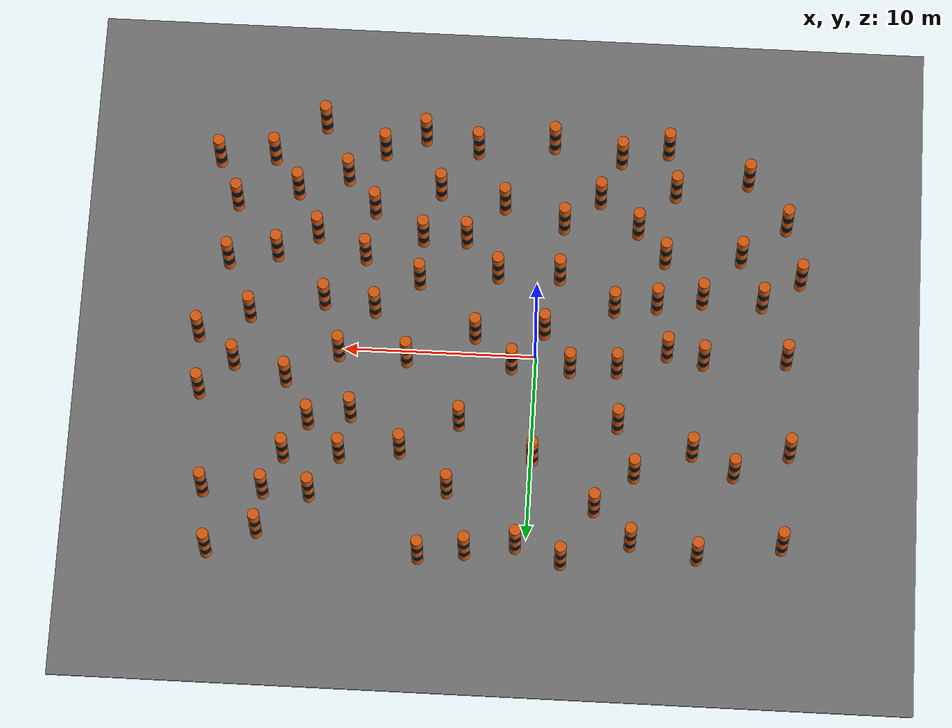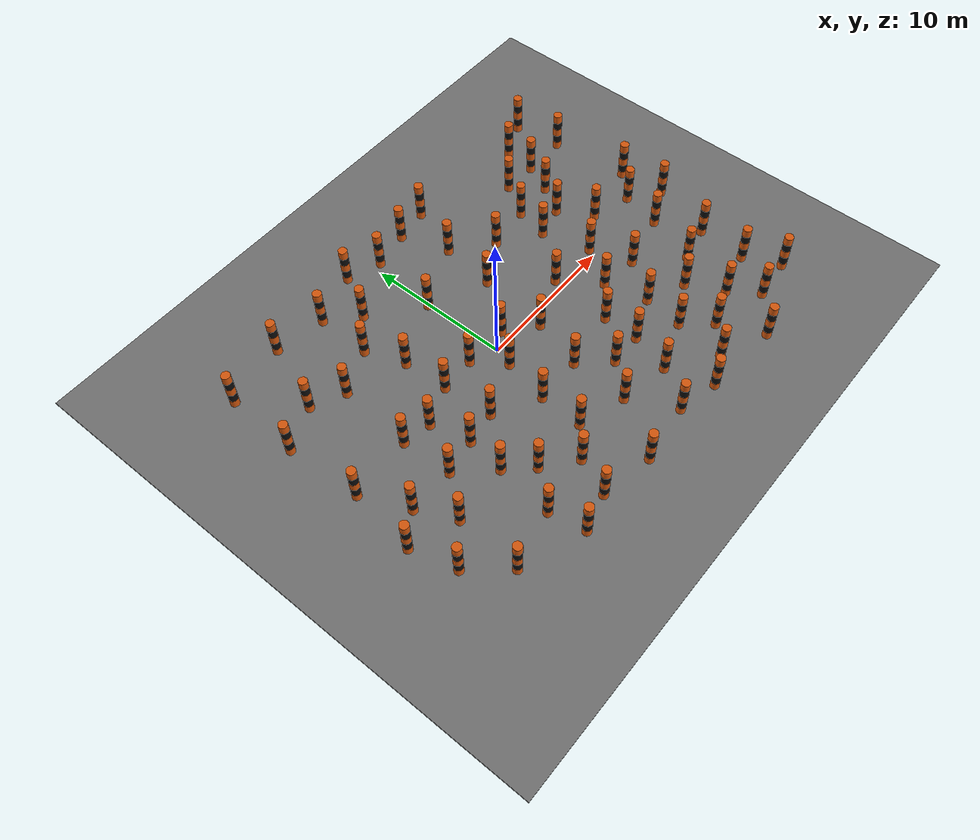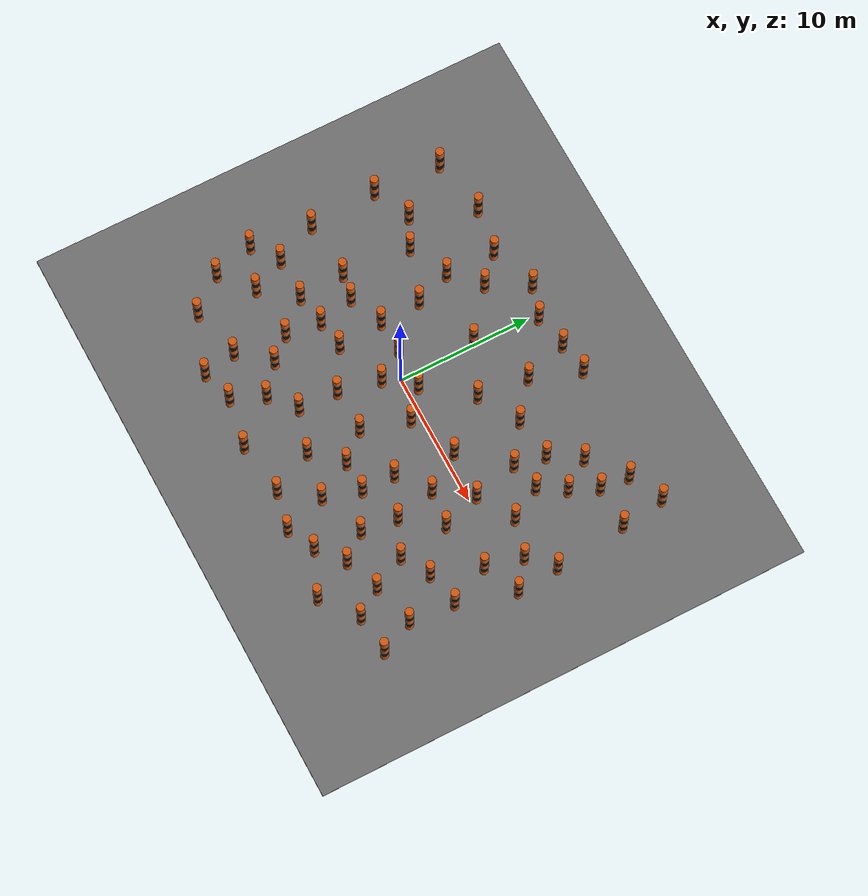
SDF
<?xml version="1.0"?>
<sdf version="1.6">
  <world name="medium_forest_striped_poles_passable_0p10_per_m2">
    <gui fullscreen="0">
      <camera name="user_camera">
        <pose>-49 27 52 0 0.75 -0.76</pose>
      </camera>
    </gui>
    <scene>
      <ambient>0.40 0.40 0.40 1</ambient>
      <background>0.70 0.80 0.90 1</background>
      <shadows>false</shadows>
    </scene>
    <light name="sun" type="directional">
      <cast_shadows>false</cast_shadows>
      <pose>0 0 20 0 0 0</pose>
      <diffuse>0.8 0.8 0.8 1</diffuse>
      <specular>0.2 0.2 0.2 1</specular>
      <attenuation>
        <range>1000</range>
        <constant>0.9</constant>
        <linear>0.01</linear>
        <quadratic>0.001</quadratic>
      </attenuation>
      <direction>-0.5 0.1 -0.9</direction>
    </light>
    <physics name="default_physics" default="1" type="ode">
      <max_step_size>0.005</max_step_size>
      <real_time_factor>1</real_time_factor>
      <real_time_update_rate>200</real_time_update_rate>
    </physics>
    <model name="ground">
      <static>true</static>
      <pose>2 0 -0.05 0 0 0</pose>
      <link name="link">
        <collision name="collision">
          <geometry>
            <box>
              <size>44 37 0.1</size>
            </box>
          </geometry>
          <surface>
            <friction>
              <ode>
                <mu>1.0</mu>
                <mu2>1.0</mu2>
              </ode>
            </friction>
          </surface>
        </collision>
        <visual name="visual">
          <geometry>
            <box>
              <size>44 37 0.1</size>
            </box>
          </geometry>
          <material>
            <ambient>0.45 0.45 0.45 1</ambient>
            <diffuse>0.45 0.45 0.45 1</diffuse>
            <specular>0.02 0.02 0.02 1</specular>
          </material>
        </visual>
      </link>
    </model>
    <model name="passable_striped_pole_001">
      <static>true</static>
      <pose>6.378 -12.090 0 0 0 0</pose>
      <link name="link">
        <collision name="collision">
          <pose>0 0 1.5 0 0 0</pose>
          <geometry>
            <cylinder>
              <radius>0.30</radius>
              <length>3.0</length>
            </cylinder>
          </geometry>
          <surface>
            <contact>
              <ode>
                <kp>1000000</kp>
                <kd>100</kd>
                <max_vel>0.01</max_vel>
                <min_depth>0.001</min_depth>
              </ode>
            </contact>
            <friction>
              <ode>
                <mu>1.0</mu>
                <mu2>1.0</mu2>
              </ode>
            </friction>
          </surface>
        </collision>
        <visual name="band_1">
          <pose>0 0 0.3 0 0 0</pose>
          <geometry>
            <cylinder>
              <radius>0.30</radius>
              <length>0.6</length>
            </cylinder>
          </geometry>
          <material>
            <ambient>0.85 0.35 0.05 1</ambient>
            <diffuse>0.85 0.35 0.05 1</diffuse>
            <specular>0.02 0.02 0.02 1</specular>
          </material>
        </visual>
        <visual name="band_2">
          <pose>0 0 0.9 0 0 0</pose>
          <geometry>
            <cylinder>
              <radius>0.30</radius>
              <length>0.6</length>
            </cylinder>
          </geometry>
          <material>
            <ambient>0.05 0.05 0.05 1</ambient>
            <diffuse>0.05 0.05 0.05 1</diffuse>
            <specular>0.02 0.02 0.02 1</specular>
          </material>
        </visual>
        <visual name="band_3">
          <pose>0 0 1.5 0 0 0</pose>
          <geometry>
            <cylinder>
              <radius>0.30</radius>
              <length>0.6</length>
            </cylinder>
          </geometry>
          <material>
            <ambient>0.85 0.35 0.05 1</ambient>
            <diffuse>0.85 0.35 0.05 1</diffuse>
            <specular>0.02 0.02 0.02 1</specular>
          </material>
        </visual>
        <visual name="band_4">
          <pose>0 0 2.1 0 0 0</pose>
          <geometry>
            <cylinder>
              <radius>0.30</radius>
              <length>0.6</length>
            </cylinder>
          </geometry>
          <material>
            <ambient>0.05 0.05 0.05 1</ambient>
            <diffuse>0.05 0.05 0.05 1</diffuse>
            <specular>0.02 0.02 0.02 1</specular>
          </material>
        </visual>
        <visual name="band_5">
          <pose>0 0 2.7 0 0 0</pose>
          <geometry>
            <cylinder>
              <radius>0.30</radius>
              <length>0.6</length>
            </cylinder>
          </geometry>
          <material>
            <ambient>0.85 0.35 0.05 1</ambient>
            <diffuse>0.85 0.35 0.05 1</diffuse>
            <specular>0.02 0.02 0.02 1</specular>
          </material>
        </visual>
      </link>
    </model>
    <model name="passable_striped_pole_002">
      <static>true</static>
      <pose>-5.064 -7.254 0 0 0 0</pose>
      <link name="link">
        <collision name="collision">
          <pose>0 0 1.5 0 0 0</pose>
          <geometry>
            <cylinder>
              <radius>0.30</radius>
              <length>3.0</length>
            </cylinder>
          </geometry>
          <surface>
            <contact>
              <ode>
                <kp>1000000</kp>
                <kd>100</kd>
                <max_vel>0.01</max_vel>
                <min_depth>0.001</min_depth>
              </ode>
            </contact>
            <friction>
              <ode>
                <mu>1.0</mu>
                <mu2>1.0</mu2>
              </ode>
            </friction>
          </surface>
        </collision>
        <visual name="band_1">
          <pose>0 0 0.3 0 0 0</pose>
          <geometry>
            <cylinder>
              <radius>0.30</radius>
              <length>0.6</length>
            </cylinder>
          </geometry>
          <material>
            <ambient>0.85 0.35 0.05 1</ambient>
            <diffuse>0.85 0.35 0.05 1</diffuse>
            <specular>0.02 0.02 0.02 1</specular>
          </material>
        </visual>
        <visual name="band_2">
          <pose>0 0 0.9 0 0 0</pose>
          <geometry>
            <cylinder>
              <radius>0.30</radius>
              <length>0.6</length>
            </cylinder>
          </geometry>
          <material>
            <ambient>0.05 0.05 0.05 1</ambient>
            <diffuse>0.05 0.05 0.05 1</diffuse>
            <specular>0.02 0.02 0.02 1</specular>
          </material>
        </visual>
        <visual name="band_3">
          <pose>0 0 1.5 0 0 0</pose>
          <geometry>
            <cylinder>
              <radius>0.30</radius>
              <length>0.6</length>
            </cylinder>
          </geometry>
          <material>
            <ambient>0.85 0.35 0.05 1</ambient>
            <diffuse>0.85 0.35 0.05 1</diffuse>
            <specular>0.02 0.02 0.02 1</specular>
          </material>
        </visual>
        <visual name="band_4">
          <pose>0 0 2.1 0 0 0</pose>
          <geometry>
            <cylinder>
              <radius>0.30</radius>
              <length>0.6</length>
            </cylinder>
          </geometry>
          <material>
            <ambient>0.05 0.05 0.05 1</ambient>
            <diffuse>0.05 0.05 0.05 1</diffuse>
            <specular>0.02 0.02 0.02 1</specular>
          </material>
        </visual>
        <visual name="band_5">
          <pose>0 0 2.7 0 0 0</pose>
          <geometry>
            <cylinder>
              <radius>0.30</radius>
              <length>0.6</length>
            </cylinder>
          </geometry>
          <material>
            <ambient>0.85 0.35 0.05 1</ambient>
            <diffuse>0.85 0.35 0.05 1</diffuse>
            <specular>0.02 0.02 0.02 1</specular>
          </material>
        </visual>
      </link>
    </model>
    <model name="passable_striped_pole_003">
      <static>true</static>
      <pose>9.425 3.811 0 0 0 0</pose>
      <link name="link">
        <collision name="collision">
          <pose>0 0 1.5 0 0 0</pose>
          <geometry>
            <cylinder>
              <radius>0.30</radius>
              <length>3.0</length>
            </cylinder>
          </geometry>
          <surface>
            <contact>
              <ode>
                <kp>1000000</kp>
                <kd>100</kd>
                <max_vel>0.01</max_vel>
                <min_depth>0.001</min_depth>
              </ode>
            </contact>
            <friction>
              <ode>
                <mu>1.0</mu>
                <mu2>1.0</mu2>
              </ode>
            </friction>
          </surface>
        </collision>
        <visual name="band_1">
          <pose>0 0 0.3 0 0 0</pose>
          <geometry>
            <cylinder>
              <radius>0.30</radius>
              <length>0.6</length>
            </cylinder>
          </geometry>
          <material>
            <ambient>0.85 0.35 0.05 1</ambient>
            <diffuse>0.85 0.35 0.05 1</diffuse>
            <specular>0.02 0.02 0.02 1</specular>
          </material>
        </visual>
        <visual name="band_2">
          <pose>0 0 0.9 0 0 0</pose>
          <geometry>
            <cylinder>
              <radius>0.30</radius>
              <length>0.6</length>
            </cylinder>
          </geometry>
          <material>
            <ambient>0.05 0.05 0.05 1</ambient>
            <diffuse>0.05 0.05 0.05 1</diffuse>
            <specular>0.02 0.02 0.02 1</specular>
          </material>
        </visual>
        <visual name="band_3">
          <pose>0 0 1.5 0 0 0</pose>
          <geometry>
            <cylinder>
              <radius>0.30</radius>
              <length>0.6</length>
            </cylinder>
          </geometry>
          <material>
            <ambient>0.85 0.35 0.05 1</ambient>
            <diffuse>0.85 0.35 0.05 1</diffuse>
            <specular>0.02 0.02 0.02 1</specular>
          </material>
        </visual>
        <visual name="band_4">
          <pose>0 0 2.1 0 0 0</pose>
          <geometry>
            <cylinder>
              <radius>0.30</radius>
              <length>0.6</length>
            </cylinder>
          </geometry>
          <material>
            <ambient>0.05 0.05 0.05 1</ambient>
            <diffuse>0.05 0.05 0.05 1</diffuse>
            <specular>0.02 0.02 0.02 1</specular>
          </material>
        </visual>
        <visual name="band_5">
          <pose>0 0 2.7 0 0 0</pose>
          <geometry>
            <cylinder>
              <radius>0.30</radius>
              <length>0.6</length>
            </cylinder>
          </geometry>
          <material>
            <ambient>0.85 0.35 0.05 1</ambient>
            <diffuse>0.85 0.35 0.05 1</diffuse>
            <specular>0.02 0.02 0.02 1</specular>
          </material>
        </visual>
      </link>
    </model>
    <model name="passable_striped_pole_004">
      <static>true</static>
      <pose>14.314 -10.579 0 0 0 0</pose>
      <link name="link">
        <collision name="collision">
          <pose>0 0 1.5 0 0 0</pose>
          <geometry>
            <cylinder>
              <radius>0.30</radius>
              <length>3.0</length>
            </cylinder>
          </geometry>
          <surface>
            <contact>
              <ode>
                <kp>1000000</kp>
                <kd>100</kd>
                <max_vel>0.01</max_vel>
                <min_depth>0.001</min_depth>
              </ode>
            </contact>
            <friction>
              <ode>
                <mu>1.0</mu>
                <mu2>1.0</mu2>
              </ode>
            </friction>
          </surface>
        </collision>
        <visual name="band_1">
          <pose>0 0 0.3 0 0 0</pose>
          <geometry>
            <cylinder>
              <radius>0.30</radius>
              <length>0.6</length>
            </cylinder>
          </geometry>
          <material>
            <ambient>0.85 0.35 0.05 1</ambient>
            <diffuse>0.85 0.35 0.05 1</diffuse>
            <specular>0.02 0.02 0.02 1</specular>
          </material>
        </visual>
        <visual name="band_2">
          <pose>0 0 0.9 0 0 0</pose>
          <geometry>
            <cylinder>
              <radius>0.30</radius>
              <length>0.6</length>
            </cylinder>
          </geometry>
          <material>
            <ambient>0.05 0.05 0.05 1</ambient>
            <diffuse>0.05 0.05 0.05 1</diffuse>
            <specular>0.02 0.02 0.02 1</specular>
          </material>
        </visual>
        <visual name="band_3">
          <pose>0 0 1.5 0 0 0</pose>
          <geometry>
            <cylinder>
              <radius>0.30</radius>
              <length>0.6</length>
            </cylinder>
          </geometry>
          <material>
            <ambient>0.85 0.35 0.05 1</ambient>
            <diffuse>0.85 0.35 0.05 1</diffuse>
            <specular>0.02 0.02 0.02 1</specular>
          </material>
        </visual>
        <visual name="band_4">
          <pose>0 0 2.1 0 0 0</pose>
          <geometry>
            <cylinder>
              <radius>0.30</radius>
              <length>0.6</length>
            </cylinder>
          </geometry>
          <material>
            <ambient>0.05 0.05 0.05 1</ambient>
            <diffuse>0.05 0.05 0.05 1</diffuse>
            <specular>0.02 0.02 0.02 1</specular>
          </material>
        </visual>
        <visual name="band_5">
          <pose>0 0 2.7 0 0 0</pose>
          <geometry>
            <cylinder>
              <radius>0.30</radius>
              <length>0.6</length>
            </cylinder>
          </geometry>
          <material>
            <ambient>0.85 0.35 0.05 1</ambient>
            <diffuse>0.85 0.35 0.05 1</diffuse>
            <specular>0.02 0.02 0.02 1</specular>
          </material>
        </visual>
      </link>
    </model>
    <model name="passable_striped_pole_005">
      <static>true</static>
      <pose>-0.452 -11.973 0 0 0 0</pose>
      <link name="link">
        <collision name="collision">
          <pose>0 0 1.5 0 0 0</pose>
          <geometry>
            <cylinder>
              <radius>0.30</radius>
              <length>3.0</length>
            </cylinder>
          </geometry>
          <surface>
            <contact>
              <ode>
                <kp>1000000</kp>
                <kd>100</kd>
                <max_vel>0.01</max_vel>
                <min_depth>0.001</min_depth>
              </ode>
            </contact>
            <friction>
              <ode>
                <mu>1.0</mu>
                <mu2>1.0</mu2>
              </ode>
            </friction>
          </surface>
        </collision>
        <visual name="band_1">
          <pose>0 0 0.3 0 0 0</pose>
          <geometry>
            <cylinder>
              <radius>0.30</radius>
              <length>0.6</length>
            </cylinder>
          </geometry>
          <material>
            <ambient>0.85 0.35 0.05 1</ambient>
            <diffuse>0.85 0.35 0.05 1</diffuse>
            <specular>0.02 0.02 0.02 1</specular>
          </material>
        </visual>
        <visual name="band_2">
          <pose>0 0 0.9 0 0 0</pose>
          <geometry>
            <cylinder>
              <radius>0.30</radius>
              <length>0.6</length>
            </cylinder>
          </geometry>
          <material>
            <ambient>0.05 0.05 0.05 1</ambient>
            <diffuse>0.05 0.05 0.05 1</diffuse>
            <specular>0.02 0.02 0.02 1</specular>
          </material>
        </visual>
        <visual name="band_3">
          <pose>0 0 1.5 0 0 0</pose>
          <geometry>
            <cylinder>
              <radius>0.30</radius>
              <length>0.6</length>
            </cylinder>
          </geometry>
          <material>
            <ambient>0.85 0.35 0.05 1</ambient>
            <diffuse>0.85 0.35 0.05 1</diffuse>
            <specular>0.02 0.02 0.02 1</specular>
          </material>
        </visual>
        <visual name="band_4">
          <pose>0 0 2.1 0 0 0</pose>
          <geometry>
            <cylinder>
              <radius>0.30</radius>
              <length>0.6</length>
            </cylinder>
          </geometry>
          <material>
            <ambient>0.05 0.05 0.05 1</ambient>
            <diffuse>0.05 0.05 0.05 1</diffuse>
            <specular>0.02 0.02 0.02 1</specular>
          </material>
        </visual>
        <visual name="band_5">
          <pose>0 0 2.7 0 0 0</pose>
          <geometry>
            <cylinder>
              <radius>0.30</radius>
              <length>0.6</length>
            </cylinder>
          </geometry>
          <material>
            <ambient>0.85 0.35 0.05 1</ambient>
            <diffuse>0.85 0.35 0.05 1</diffuse>
            <specular>0.02 0.02 0.02 1</specular>
          </material>
        </visual>
      </link>
    </model>
    <model name="passable_striped_pole_006">
      <static>true</static>
      <pose>-6.835 -0.369 0 0 0 0</pose>
      <link name="link">
        <collision name="collision">
          <pose>0 0 1.5 0 0 0</pose>
          <geometry>
            <cylinder>
              <radius>0.30</radius>
              <length>3.0</length>
            </cylinder>
          </geometry>
          <surface>
            <contact>
              <ode>
                <kp>1000000</kp>
                <kd>100</kd>
                <max_vel>0.01</max_vel>
                <min_depth>0.001</min_depth>
              </ode>
            </contact>
            <friction>
              <ode>
                <mu>1.0</mu>
                <mu2>1.0</mu2>
              </ode>
            </friction>
          </surface>
        </collision>
        <visual name="band_1">
          <pose>0 0 0.3 0 0 0</pose>
          <geometry>
            <cylinder>
              <radius>0.30</radius>
              <length>0.6</length>
            </cylinder>
          </geometry>
          <material>
            <ambient>0.85 0.35 0.05 1</ambient>
            <diffuse>0.85 0.35 0.05 1</diffuse>
            <specular>0.02 0.02 0.02 1</specular>
          </material>
        </visual>
        <visual name="band_2">
          <pose>0 0 0.9 0 0 0</pose>
          <geometry>
            <cylinder>
              <radius>0.30</radius>
              <length>0.6</length>
            </cylinder>
          </geometry>
          <material>
            <ambient>0.05 0.05 0.05 1</ambient>
            <diffuse>0.05 0.05 0.05 1</diffuse>
            <specular>0.02 0.02 0.02 1</specular>
          </material>
        </visual>
        <visual name="band_3">
          <pose>0 0 1.5 0 0 0</pose>
          <geometry>
            <cylinder>
              <radius>0.30</radius>
              <length>0.6</length>
            </cylinder>
          </geometry>
          <material>
            <ambient>0.85 0.35 0.05 1</ambient>
            <diffuse>0.85 0.35 0.05 1</diffuse>
            <specular>0.02 0.02 0.02 1</specular>
          </material>
        </visual>
        <visual name="band_4">
          <pose>0 0 2.1 0 0 0</pose>
          <geometry>
            <cylinder>
              <radius>0.30</radius>
              <length>0.6</length>
            </cylinder>
          </geometry>
          <material>
            <ambient>0.05 0.05 0.05 1</ambient>
            <diffuse>0.05 0.05 0.05 1</diffuse>
            <specular>0.02 0.02 0.02 1</specular>
          </material>
        </visual>
        <visual name="band_5">
          <pose>0 0 2.7 0 0 0</pose>
          <geometry>
            <cylinder>
              <radius>0.30</radius>
              <length>0.6</length>
            </cylinder>
          </geometry>
          <material>
            <ambient>0.85 0.35 0.05 1</ambient>
            <diffuse>0.85 0.35 0.05 1</diffuse>
            <specular>0.02 0.02 0.02 1</specular>
          </material>
        </visual>
      </link>
    </model>
    <model name="passable_striped_pole_007">
      <static>true</static>
      <pose>-12.867 -7.848 0 0 0 0</pose>
      <link name="link">
        <collision name="collision">
          <pose>0 0 1.5 0 0 0</pose>
          <geometry>
            <cylinder>
              <radius>0.30</radius>
              <length>3.0</length>
            </cylinder>
          </geometry>
          <surface>
            <contact>
              <ode>
                <kp>1000000</kp>
                <kd>100</kd>
                <max_vel>0.01</max_vel>
                <min_depth>0.001</min_depth>
              </ode>
            </contact>
            <friction>
              <ode>
                <mu>1.0</mu>
                <mu2>1.0</mu2>
              </ode>
            </friction>
          </surface>
        </collision>
        <visual name="band_1">
          <pose>0 0 0.3 0 0 0</pose>
          <geometry>
            <cylinder>
              <radius>0.30</radius>
              <length>0.6</length>
            </cylinder>
          </geometry>
          <material>
            <ambient>0.85 0.35 0.05 1</ambient>
            <diffuse>0.85 0.35 0.05 1</diffuse>
            <specular>0.02 0.02 0.02 1</specular>
          </material>
        </visual>
        <visual name="band_2">
          <pose>0 0 0.9 0 0 0</pose>
          <geometry>
            <cylinder>
              <radius>0.30</radius>
              <length>0.6</length>
            </cylinder>
          </geometry>
          <material>
            <ambient>0.05 0.05 0.05 1</ambient>
            <diffuse>0.05 0.05 0.05 1</diffuse>
            <specular>0.02 0.02 0.02 1</specular>
          </material>
        </visual>
        <visual name="band_3">
          <pose>0 0 1.5 0 0 0</pose>
          <geometry>
            <cylinder>
              <radius>0.30</radius>
              <length>0.6</length>
            </cylinder>
          </geometry>
          <material>
            <ambient>0.85 0.35 0.05 1</ambient>
            <diffuse>0.85 0.35 0.05 1</diffuse>
            <specular>0.02 0.02 0.02 1</specular>
          </material>
        </visual>
        <visual name="band_4">
          <pose>0 0 2.1 0 0 0</pose>
          <geometry>
            <cylinder>
              <radius>0.30</radius>
              <length>0.6</length>
            </cylinder>
          </geometry>
          <material>
            <ambient>0.05 0.05 0.05 1</ambient>
            <diffuse>0.05 0.05 0.05 1</diffuse>
            <specular>0.02 0.02 0.02 1</specular>
          </material>
        </visual>
        <visual name="band_5">
          <pose>0 0 2.7 0 0 0</pose>
          <geometry>
            <cylinder>
              <radius>0.30</radius>
              <length>0.6</length>
            </cylinder>
          </geometry>
          <material>
            <ambient>0.85 0.35 0.05 1</ambient>
            <diffuse>0.85 0.35 0.05 1</diffuse>
            <specular>0.02 0.02 0.02 1</specular>
          </material>
        </visual>
      </link>
    </model>
    <model name="passable_striped_pole_008">
      <static>true</static>
      <pose>6.706 0.597 0 0 0 0</pose>
      <link name="link">
        <collision name="collision">
          <pose>0 0 1.5 0 0 0</pose>
          <geometry>
            <cylinder>
              <radius>0.30</radius>
              <length>3.0</length>
            </cylinder>
          </geometry>
          <surface>
            <contact>
              <ode>
                <kp>1000000</kp>
                <kd>100</kd>
                <max_vel>0.01</max_vel>
                <min_depth>0.001</min_depth>
              </ode>
            </contact>
            <friction>
              <ode>
                <mu>1.0</mu>
                <mu2>1.0</mu2>
              </ode>
            </friction>
          </surface>
        </collision>
        <visual name="band_1">
          <pose>0 0 0.3 0 0 0</pose>
          <geometry>
            <cylinder>
              <radius>0.30</radius>
              <length>0.6</length>
            </cylinder>
          </geometry>
          <material>
            <ambient>0.85 0.35 0.05 1</ambient>
            <diffuse>0.85 0.35 0.05 1</diffuse>
            <specular>0.02 0.02 0.02 1</specular>
          </material>
        </visual>
        <visual name="band_2">
          <pose>0 0 0.9 0 0 0</pose>
          <geometry>
            <cylinder>
              <radius>0.30</radius>
              <length>0.6</length>
            </cylinder>
          </geometry>
          <material>
            <ambient>0.05 0.05 0.05 1</ambient>
            <diffuse>0.05 0.05 0.05 1</diffuse>
            <specular>0.02 0.02 0.02 1</specular>
          </material>
        </visual>
        <visual name="band_3">
          <pose>0 0 1.5 0 0 0</pose>
          <geometry>
            <cylinder>
              <radius>0.30</radius>
              <length>0.6</length>
            </cylinder>
          </geometry>
          <material>
            <ambient>0.85 0.35 0.05 1</ambient>
            <diffuse>0.85 0.35 0.05 1</diffuse>
            <specular>0.02 0.02 0.02 1</specular>
          </material>
        </visual>
        <visual name="band_4">
          <pose>0 0 2.1 0 0 0</pose>
          <geometry>
            <cylinder>
              <radius>0.30</radius>
              <length>0.6</length>
            </cylinder>
          </geometry>
          <material>
            <ambient>0.05 0.05 0.05 1</ambient>
            <diffuse>0.05 0.05 0.05 1</diffuse>
            <specular>0.02 0.02 0.02 1</specular>
          </material>
        </visual>
        <visual name="band_5">
          <pose>0 0 2.7 0 0 0</pose>
          <geometry>
            <cylinder>
              <radius>0.30</radius>
              <length>0.6</length>
            </cylinder>
          </geometry>
          <material>
            <ambient>0.85 0.35 0.05 1</ambient>
            <diffuse>0.85 0.35 0.05 1</diffuse>
            <specular>0.02 0.02 0.02 1</specular>
          </material>
        </visual>
      </link>
    </model>
    <model name="passable_striped_pole_009">
      <static>true</static>
      <pose>11.716 -12.541 0 0 0 0</pose>
      <link name="link">
        <collision name="collision">
          <pose>0 0 1.5 0 0 0</pose>
          <geometry>
            <cylinder>
              <radius>0.30</radius>
              <length>3.0</length>
            </cylinder>
          </geometry>
          <surface>
            <contact>
              <ode>
                <kp>1000000</kp>
                <kd>100</kd>
                <max_vel>0.01</max_vel>
                <min_depth>0.001</min_depth>
              </ode>
            </contact>
            <friction>
              <ode>
                <mu>1.0</mu>
                <mu2>1.0</mu2>
              </ode>
            </friction>
          </surface>
        </collision>
        <visual name="band_1">
          <pose>0 0 0.3 0 0 0</pose>
          <geometry>
            <cylinder>
              <radius>0.30</radius>
              <length>0.6</length>
            </cylinder>
          </geometry>
          <material>
            <ambient>0.85 0.35 0.05 1</ambient>
            <diffuse>0.85 0.35 0.05 1</diffuse>
            <specular>0.02 0.02 0.02 1</specular>
          </material>
        </visual>
        <visual name="band_2">
          <pose>0 0 0.9 0 0 0</pose>
          <geometry>
            <cylinder>
              <radius>0.30</radius>
              <length>0.6</length>
            </cylinder>
          </geometry>
          <material>
            <ambient>0.05 0.05 0.05 1</ambient>
            <diffuse>0.05 0.05 0.05 1</diffuse>
            <specular>0.02 0.02 0.02 1</specular>
          </material>
        </visual>
        <visual name="band_3">
          <pose>0 0 1.5 0 0 0</pose>
          <geometry>
            <cylinder>
              <radius>0.30</radius>
              <length>0.6</length>
            </cylinder>
          </geometry>
          <material>
            <ambient>0.85 0.35 0.05 1</ambient>
            <diffuse>0.85 0.35 0.05 1</diffuse>
            <specular>0.02 0.02 0.02 1</specular>
          </material>
        </visual>
        <visual name="band_4">
          <pose>0 0 2.1 0 0 0</pose>
          <geometry>
            <cylinder>
              <radius>0.30</radius>
              <length>0.6</length>
            </cylinder>
          </geometry>
          <material>
            <ambient>0.05 0.05 0.05 1</ambient>
            <diffuse>0.05 0.05 0.05 1</diffuse>
            <specular>0.02 0.02 0.02 1</specular>
          </material>
        </visual>
        <visual name="band_5">
          <pose>0 0 2.7 0 0 0</pose>
          <geometry>
            <cylinder>
              <radius>0.30</radius>
              <length>0.6</length>
            </cylinder>
          </geometry>
          <material>
            <ambient>0.85 0.35 0.05 1</ambient>
            <diffuse>0.85 0.35 0.05 1</diffuse>
            <specular>0.02 0.02 0.02 1</specular>
          </material>
        </visual>
      </link>
    </model>
    <model name="passable_striped_pole_010">
      <static>true</static>
      <pose>11.603 4.335 0 0 0 0</pose>
      <link name="link">
        <collision name="collision">
          <pose>0 0 1.5 0 0 0</pose>
          <geometry>
            <cylinder>
              <radius>0.30</radius>
              <length>3.0</length>
            </cylinder>
          </geometry>
          <surface>
            <contact>
              <ode>
                <kp>1000000</kp>
                <kd>100</kd>
                <max_vel>0.01</max_vel>
                <min_depth>0.001</min_depth>
              </ode>
            </contact>
            <friction>
              <ode>
                <mu>1.0</mu>
                <mu2>1.0</mu2>
              </ode>
            </friction>
          </surface>
        </collision>
        <visual name="band_1">
          <pose>0 0 0.3 0 0 0</pose>
          <geometry>
            <cylinder>
              <radius>0.30</radius>
              <length>0.6</length>
            </cylinder>
          </geometry>
          <material>
            <ambient>0.85 0.35 0.05 1</ambient>
            <diffuse>0.85 0.35 0.05 1</diffuse>
            <specular>0.02 0.02 0.02 1</specular>
          </material>
        </visual>
        <visual name="band_2">
          <pose>0 0 0.9 0 0 0</pose>
          <geometry>
            <cylinder>
              <radius>0.30</radius>
              <length>0.6</length>
            </cylinder>
          </geometry>
          <material>
            <ambient>0.05 0.05 0.05 1</ambient>
            <diffuse>0.05 0.05 0.05 1</diffuse>
            <specular>0.02 0.02 0.02 1</specular>
          </material>
        </visual>
        <visual name="band_3">
          <pose>0 0 1.5 0 0 0</pose>
          <geometry>
            <cylinder>
              <radius>0.30</radius>
              <length>0.6</length>
            </cylinder>
          </geometry>
          <material>
            <ambient>0.85 0.35 0.05 1</ambient>
            <diffuse>0.85 0.35 0.05 1</diffuse>
            <specular>0.02 0.02 0.02 1</specular>
          </material>
        </visual>
        <visual name="band_4">
          <pose>0 0 2.1 0 0 0</pose>
          <geometry>
            <cylinder>
              <radius>0.30</radius>
              <length>0.6</length>
            </cylinder>
          </geometry>
          <material>
            <ambient>0.05 0.05 0.05 1</ambient>
            <diffuse>0.05 0.05 0.05 1</diffuse>
            <specular>0.02 0.02 0.02 1</specular>
          </material>
        </visual>
        <visual name="band_5">
          <pose>0 0 2.7 0 0 0</pose>
          <geometry>
            <cylinder>
              <radius>0.30</radius>
              <length>0.6</length>
            </cylinder>
          </geometry>
          <material>
            <ambient>0.85 0.35 0.05 1</ambient>
            <diffuse>0.85 0.35 0.05 1</diffuse>
            <specular>0.02 0.02 0.02 1</specular>
          </material>
        </visual>
      </link>
    </model>
    <model name="passable_striped_pole_011">
      <static>true</static>
      <pose>-3.016 -8.906 0 0 0 0</pose>
      <link name="link">
        <collision name="collision">
          <pose>0 0 1.5 0 0 0</pose>
          <geometry>
            <cylinder>
              <radius>0.30</radius>
              <length>3.0</length>
            </cylinder>
          </geometry>
          <surface>
            <contact>
              <ode>
                <kp>1000000</kp>
                <kd>100</kd>
                <max_vel>0.01</max_vel>
                <min_depth>0.001</min_depth>
              </ode>
            </contact>
            <friction>
              <ode>
                <mu>1.0</mu>
                <mu2>1.0</mu2>
              </ode>
            </friction>
          </surface>
        </collision>
        <visual name="band_1">
          <pose>0 0 0.3 0 0 0</pose>
          <geometry>
            <cylinder>
              <radius>0.30</radius>
              <length>0.6</length>
            </cylinder>
          </geometry>
          <material>
            <ambient>0.85 0.35 0.05 1</ambient>
            <diffuse>0.85 0.35 0.05 1</diffuse>
            <specular>0.02 0.02 0.02 1</specular>
          </material>
        </visual>
        <visual name="band_2">
          <pose>0 0 0.9 0 0 0</pose>
          <geometry>
            <cylinder>
              <radius>0.30</radius>
              <length>0.6</length>
            </cylinder>
          </geometry>
          <material>
            <ambient>0.05 0.05 0.05 1</ambient>
            <diffuse>0.05 0.05 0.05 1</diffuse>
            <specular>0.02 0.02 0.02 1</specular>
          </material>
        </visual>
        <visual name="band_3">
          <pose>0 0 1.5 0 0 0</pose>
          <geometry>
            <cylinder>
              <radius>0.30</radius>
              <length>0.6</length>
            </cylinder>
          </geometry>
          <material>
            <ambient>0.85 0.35 0.05 1</ambient>
            <diffuse>0.85 0.35 0.05 1</diffuse>
            <specular>0.02 0.02 0.02 1</specular>
          </material>
        </visual>
        <visual name="band_4">
          <pose>0 0 2.1 0 0 0</pose>
          <geometry>
            <cylinder>
              <radius>0.30</radius>
              <length>0.6</length>
            </cylinder>
          </geometry>
          <material>
            <ambient>0.05 0.05 0.05 1</ambient>
            <diffuse>0.05 0.05 0.05 1</diffuse>
            <specular>0.02 0.02 0.02 1</specular>
          </material>
        </visual>
        <visual name="band_5">
          <pose>0 0 2.7 0 0 0</pose>
          <geometry>
            <cylinder>
              <radius>0.30</radius>
              <length>0.6</length>
            </cylinder>
          </geometry>
          <material>
            <ambient>0.85 0.35 0.05 1</ambient>
            <diffuse>0.85 0.35 0.05 1</diffuse>
            <specular>0.02 0.02 0.02 1</specular>
          </material>
        </visual>
      </link>
    </model>
    <model name="passable_striped_pole_012">
      <static>true</static>
      <pose>16.356 -4.487 0 0 0 0</pose>
      <link name="link">
        <collision name="collision">
          <pose>0 0 1.5 0 0 0</pose>
          <geometry>
            <cylinder>
              <radius>0.30</radius>
              <length>3.0</length>
            </cylinder>
          </geometry>
          <surface>
            <contact>
              <ode>
                <kp>1000000</kp>
                <kd>100</kd>
                <max_vel>0.01</max_vel>
                <min_depth>0.001</min_depth>
              </ode>
            </contact>
            <friction>
              <ode>
                <mu>1.0</mu>
                <mu2>1.0</mu2>
              </ode>
            </friction>
          </surface>
        </collision>
        <visual name="band_1">
          <pose>0 0 0.3 0 0 0</pose>
          <geometry>
            <cylinder>
              <radius>0.30</radius>
              <length>0.6</length>
            </cylinder>
          </geometry>
          <material>
            <ambient>0.85 0.35 0.05 1</ambient>
            <diffuse>0.85 0.35 0.05 1</diffuse>
            <specular>0.02 0.02 0.02 1</specular>
          </material>
        </visual>
        <visual name="band_2">
          <pose>0 0 0.9 0 0 0</pose>
          <geometry>
            <cylinder>
              <radius>0.30</radius>
              <length>0.6</length>
            </cylinder>
          </geometry>
          <material>
            <ambient>0.05 0.05 0.05 1</ambient>
            <diffuse>0.05 0.05 0.05 1</diffuse>
            <specular>0.02 0.02 0.02 1</specular>
          </material>
        </visual>
        <visual name="band_3">
          <pose>0 0 1.5 0 0 0</pose>
          <geometry>
            <cylinder>
              <radius>0.30</radius>
              <length>0.6</length>
            </cylinder>
          </geometry>
          <material>
            <ambient>0.85 0.35 0.05 1</ambient>
            <diffuse>0.85 0.35 0.05 1</diffuse>
            <specular>0.02 0.02 0.02 1</specular>
          </material>
        </visual>
        <visual name="band_4">
          <pose>0 0 2.1 0 0 0</pose>
          <geometry>
            <cylinder>
              <radius>0.30</radius>
              <length>0.6</length>
            </cylinder>
          </geometry>
          <material>
            <ambient>0.05 0.05 0.05 1</ambient>
            <diffuse>0.05 0.05 0.05 1</diffuse>
            <specular>0.02 0.02 0.02 1</specular>
          </material>
        </visual>
        <visual name="band_5">
          <pose>0 0 2.7 0 0 0</pose>
          <geometry>
            <cylinder>
              <radius>0.30</radius>
              <length>0.6</length>
            </cylinder>
          </geometry>
          <material>
            <ambient>0.85 0.35 0.05 1</ambient>
            <diffuse>0.85 0.35 0.05 1</diffuse>
            <specular>0.02 0.02 0.02 1</specular>
          </material>
        </visual>
      </link>
    </model>
    <model name="passable_striped_pole_013">
      <static>true</static>
      <pose>-10.788 -10.340 0 0 0 0</pose>
      <link name="link">
        <collision name="collision">
          <pose>0 0 1.5 0 0 0</pose>
          <geometry>
            <cylinder>
              <radius>0.30</radius>
              <length>3.0</length>
            </cylinder>
          </geometry>
          <surface>
            <contact>
              <ode>
                <kp>1000000</kp>
                <kd>100</kd>
                <max_vel>0.01</max_vel>
                <min_depth>0.001</min_depth>
              </ode>
            </contact>
            <friction>
              <ode>
                <mu>1.0</mu>
                <mu2>1.0</mu2>
              </ode>
            </friction>
          </surface>
        </collision>
        <visual name="band_1">
          <pose>0 0 0.3 0 0 0</pose>
          <geometry>
            <cylinder>
              <radius>0.30</radius>
              <length>0.6</length>
            </cylinder>
          </geometry>
          <material>
            <ambient>0.85 0.35 0.05 1</ambient>
            <diffuse>0.85 0.35 0.05 1</diffuse>
            <specular>0.02 0.02 0.02 1</specular>
          </material>
        </visual>
        <visual name="band_2">
          <pose>0 0 0.9 0 0 0</pose>
          <geometry>
            <cylinder>
              <radius>0.30</radius>
              <length>0.6</length>
            </cylinder>
          </geometry>
          <material>
            <ambient>0.05 0.05 0.05 1</ambient>
            <diffuse>0.05 0.05 0.05 1</diffuse>
            <specular>0.02 0.02 0.02 1</specular>
          </material>
        </visual>
        <visual name="band_3">
          <pose>0 0 1.5 0 0 0</pose>
          <geometry>
            <cylinder>
              <radius>0.30</radius>
              <length>0.6</length>
            </cylinder>
          </geometry>
          <material>
            <ambient>0.85 0.35 0.05 1</ambient>
            <diffuse>0.85 0.35 0.05 1</diffuse>
            <specular>0.02 0.02 0.02 1</specular>
          </material>
        </visual>
        <visual name="band_4">
          <pose>0 0 2.1 0 0 0</pose>
          <geometry>
            <cylinder>
              <radius>0.30</radius>
              <length>0.6</length>
            </cylinder>
          </geometry>
          <material>
            <ambient>0.05 0.05 0.05 1</ambient>
            <diffuse>0.05 0.05 0.05 1</diffuse>
            <specular>0.02 0.02 0.02 1</specular>
          </material>
        </visual>
        <visual name="band_5">
          <pose>0 0 2.7 0 0 0</pose>
          <geometry>
            <cylinder>
              <radius>0.30</radius>
              <length>0.6</length>
            </cylinder>
          </geometry>
          <material>
            <ambient>0.85 0.35 0.05 1</ambient>
            <diffuse>0.85 0.35 0.05 1</diffuse>
            <specular>0.02 0.02 0.02 1</specular>
          </material>
        </visual>
      </link>
    </model>
    <model name="passable_striped_pole_014">
      <static>true</static>
      <pose>12.911 2.031 0 0 0 0</pose>
      <link name="link">
        <collision name="collision">
          <pose>0 0 1.5 0 0 0</pose>
          <geometry>
            <cylinder>
              <radius>0.30</radius>
              <length>3.0</length>
            </cylinder>
          </geometry>
          <surface>
            <contact>
              <ode>
                <kp>1000000</kp>
                <kd>100</kd>
                <max_vel>0.01</max_vel>
                <min_depth>0.001</min_depth>
              </ode>
            </contact>
            <friction>
              <ode>
                <mu>1.0</mu>
                <mu2>1.0</mu2>
              </ode>
            </friction>
          </surface>
        </collision>
        <visual name="band_1">
          <pose>0 0 0.3 0 0 0</pose>
          <geometry>
            <cylinder>
              <radius>0.30</radius>
              <length>0.6</length>
            </cylinder>
          </geometry>
          <material>
            <ambient>0.85 0.35 0.05 1</ambient>
            <diffuse>0.85 0.35 0.05 1</diffuse>
            <specular>0.02 0.02 0.02 1</specular>
          </material>
        </visual>
        <visual name="band_2">
          <pose>0 0 0.9 0 0 0</pose>
          <geometry>
            <cylinder>
              <radius>0.30</radius>
              <length>0.6</length>
            </cylinder>
          </geometry>
          <material>
            <ambient>0.05 0.05 0.05 1</ambient>
            <diffuse>0.05 0.05 0.05 1</diffuse>
            <specular>0.02 0.02 0.02 1</specular>
          </material>
        </visual>
        <visual name="band_3">
          <pose>0 0 1.5 0 0 0</pose>
          <geometry>
            <cylinder>
              <radius>0.30</radius>
              <length>0.6</length>
            </cylinder>
          </geometry>
          <material>
            <ambient>0.85 0.35 0.05 1</ambient>
            <diffuse>0.85 0.35 0.05 1</diffuse>
            <specular>0.02 0.02 0.02 1</specular>
          </material>
        </visual>
        <visual name="band_4">
          <pose>0 0 2.1 0 0 0</pose>
          <geometry>
            <cylinder>
              <radius>0.30</radius>
              <length>0.6</length>
            </cylinder>
          </geometry>
          <material>
            <ambient>0.05 0.05 0.05 1</ambient>
            <diffuse>0.05 0.05 0.05 1</diffuse>
            <specular>0.02 0.02 0.02 1</specular>
          </material>
        </visual>
        <visual name="band_5">
          <pose>0 0 2.7 0 0 0</pose>
          <geometry>
            <cylinder>
              <radius>0.30</radius>
              <length>0.6</length>
            </cylinder>
          </geometry>
          <material>
            <ambient>0.85 0.35 0.05 1</ambient>
            <diffuse>0.85 0.35 0.05 1</diffuse>
            <specular>0.02 0.02 0.02 1</specular>
          </material>
        </visual>
      </link>
    </model>
    <model name="passable_striped_pole_015">
      <static>true</static>
      <pose>3.138 11.044 0 0 0 0</pose>
      <link name="link">
        <collision name="collision">
          <pose>0 0 1.5 0 0 0</pose>
          <geometry>
            <cylinder>
              <radius>0.30</radius>
              <length>3.0</length>
            </cylinder>
          </geometry>
          <surface>
            <contact>
              <ode>
                <kp>1000000</kp>
                <kd>100</kd>
                <max_vel>0.01</max_vel>
                <min_depth>0.001</min_depth>
              </ode>
            </contact>
            <friction>
              <ode>
                <mu>1.0</mu>
                <mu2>1.0</mu2>
              </ode>
            </friction>
          </surface>
        </collision>
        <visual name="band_1">
          <pose>0 0 0.3 0 0 0</pose>
          <geometry>
            <cylinder>
              <radius>0.30</radius>
              <length>0.6</length>
            </cylinder>
          </geometry>
          <material>
            <ambient>0.85 0.35 0.05 1</ambient>
            <diffuse>0.85 0.35 0.05 1</diffuse>
            <specular>0.02 0.02 0.02 1</specular>
          </material>
        </visual>
        <visual name="band_2">
          <pose>0 0 0.9 0 0 0</pose>
          <geometry>
            <cylinder>
              <radius>0.30</radius>
              <length>0.6</length>
            </cylinder>
          </geometry>
          <material>
            <ambient>0.05 0.05 0.05 1</ambient>
            <diffuse>0.05 0.05 0.05 1</diffuse>
            <specular>0.02 0.02 0.02 1</specular>
          </material>
        </visual>
        <visual name="band_3">
          <pose>0 0 1.5 0 0 0</pose>
          <geometry>
            <cylinder>
              <radius>0.30</radius>
              <length>0.6</length>
            </cylinder>
          </geometry>
          <material>
            <ambient>0.85 0.35 0.05 1</ambient>
            <diffuse>0.85 0.35 0.05 1</diffuse>
            <specular>0.02 0.02 0.02 1</specular>
          </material>
        </visual>
        <visual name="band_4">
          <pose>0 0 2.1 0 0 0</pose>
          <geometry>
            <cylinder>
              <radius>0.30</radius>
              <length>0.6</length>
            </cylinder>
          </geometry>
          <material>
            <ambient>0.05 0.05 0.05 1</ambient>
            <diffuse>0.05 0.05 0.05 1</diffuse>
            <specular>0.02 0.02 0.02 1</specular>
          </material>
        </visual>
        <visual name="band_5">
          <pose>0 0 2.7 0 0 0</pose>
          <geometry>
            <cylinder>
              <radius>0.30</radius>
              <length>0.6</length>
            </cylinder>
          </geometry>
          <material>
            <ambient>0.85 0.35 0.05 1</ambient>
            <diffuse>0.85 0.35 0.05 1</diffuse>
            <specular>0.02 0.02 0.02 1</specular>
          </material>
        </visual>
      </link>
    </model>
    <model name="passable_striped_pole_016">
      <static>true</static>
      <pose>-1.814 0.770 0 0 0 0</pose>
      <link name="link">
        <collision name="collision">
          <pose>0 0 1.5 0 0 0</pose>
          <geometry>
            <cylinder>
              <radius>0.30</radius>
              <length>3.0</length>
            </cylinder>
          </geometry>
          <surface>
            <contact>
              <ode>
                <kp>1000000</kp>
                <kd>100</kd>
                <max_vel>0.01</max_vel>
                <min_depth>0.001</min_depth>
              </ode>
            </contact>
            <friction>
              <ode>
                <mu>1.0</mu>
                <mu2>1.0</mu2>
              </ode>
            </friction>
          </surface>
        </collision>
        <visual name="band_1">
          <pose>0 0 0.3 0 0 0</pose>
          <geometry>
            <cylinder>
              <radius>0.30</radius>
              <length>0.6</length>
            </cylinder>
          </geometry>
          <material>
            <ambient>0.85 0.35 0.05 1</ambient>
            <diffuse>0.85 0.35 0.05 1</diffuse>
            <specular>0.02 0.02 0.02 1</specular>
          </material>
        </visual>
        <visual name="band_2">
          <pose>0 0 0.9 0 0 0</pose>
          <geometry>
            <cylinder>
              <radius>0.30</radius>
              <length>0.6</length>
            </cylinder>
          </geometry>
          <material>
            <ambient>0.05 0.05 0.05 1</ambient>
            <diffuse>0.05 0.05 0.05 1</diffuse>
            <specular>0.02 0.02 0.02 1</specular>
          </material>
        </visual>
        <visual name="band_3">
          <pose>0 0 1.5 0 0 0</pose>
          <geometry>
            <cylinder>
              <radius>0.30</radius>
              <length>0.6</length>
            </cylinder>
          </geometry>
          <material>
            <ambient>0.85 0.35 0.05 1</ambient>
            <diffuse>0.85 0.35 0.05 1</diffuse>
            <specular>0.02 0.02 0.02 1</specular>
          </material>
        </visual>
        <visual name="band_4">
          <pose>0 0 2.1 0 0 0</pose>
          <geometry>
            <cylinder>
              <radius>0.30</radius>
              <length>0.6</length>
            </cylinder>
          </geometry>
          <material>
            <ambient>0.05 0.05 0.05 1</ambient>
            <diffuse>0.05 0.05 0.05 1</diffuse>
            <specular>0.02 0.02 0.02 1</specular>
          </material>
        </visual>
        <visual name="band_5">
          <pose>0 0 2.7 0 0 0</pose>
          <geometry>
            <cylinder>
              <radius>0.30</radius>
              <length>0.6</length>
            </cylinder>
          </geometry>
          <material>
            <ambient>0.85 0.35 0.05 1</ambient>
            <diffuse>0.85 0.35 0.05 1</diffuse>
            <specular>0.02 0.02 0.02 1</specular>
          </material>
        </visual>
      </link>
    </model>
    <model name="passable_striped_pole_017">
      <static>true</static>
      <pose>-6.544 -5.639 0 0 0 0</pose>
      <link name="link">
        <collision name="collision">
          <pose>0 0 1.5 0 0 0</pose>
          <geometry>
            <cylinder>
              <radius>0.30</radius>
              <length>3.0</length>
            </cylinder>
          </geometry>
          <surface>
            <contact>
              <ode>
                <kp>1000000</kp>
                <kd>100</kd>
                <max_vel>0.01</max_vel>
                <min_depth>0.001</min_depth>
              </ode>
            </contact>
            <friction>
              <ode>
                <mu>1.0</mu>
                <mu2>1.0</mu2>
              </ode>
            </friction>
          </surface>
        </collision>
        <visual name="band_1">
          <pose>0 0 0.3 0 0 0</pose>
          <geometry>
            <cylinder>
              <radius>0.30</radius>
              <length>0.6</length>
            </cylinder>
          </geometry>
          <material>
            <ambient>0.85 0.35 0.05 1</ambient>
            <diffuse>0.85 0.35 0.05 1</diffuse>
            <specular>0.02 0.02 0.02 1</specular>
          </material>
        </visual>
        <visual name="band_2">
          <pose>0 0 0.9 0 0 0</pose>
          <geometry>
            <cylinder>
              <radius>0.30</radius>
              <length>0.6</length>
            </cylinder>
          </geometry>
          <material>
            <ambient>0.05 0.05 0.05 1</ambient>
            <diffuse>0.05 0.05 0.05 1</diffuse>
            <specular>0.02 0.02 0.02 1</specular>
          </material>
        </visual>
        <visual name="band_3">
          <pose>0 0 1.5 0 0 0</pose>
          <geometry>
            <cylinder>
              <radius>0.30</radius>
              <length>0.6</length>
            </cylinder>
          </geometry>
          <material>
            <ambient>0.85 0.35 0.05 1</ambient>
            <diffuse>0.85 0.35 0.05 1</diffuse>
            <specular>0.02 0.02 0.02 1</specular>
          </material>
        </visual>
        <visual name="band_4">
          <pose>0 0 2.1 0 0 0</pose>
          <geometry>
            <cylinder>
              <radius>0.30</radius>
              <length>0.6</length>
            </cylinder>
          </geometry>
          <material>
            <ambient>0.05 0.05 0.05 1</ambient>
            <diffuse>0.05 0.05 0.05 1</diffuse>
            <specular>0.02 0.02 0.02 1</specular>
          </material>
        </visual>
        <visual name="band_5">
          <pose>0 0 2.7 0 0 0</pose>
          <geometry>
            <cylinder>
              <radius>0.30</radius>
              <length>0.6</length>
            </cylinder>
          </geometry>
          <material>
            <ambient>0.85 0.35 0.05 1</ambient>
            <diffuse>0.85 0.35 0.05 1</diffuse>
            <specular>0.02 0.02 0.02 1</specular>
          </material>
        </visual>
      </link>
    </model>
    <model name="passable_striped_pole_018">
      <static>true</static>
      <pose>-10.529 -5.917 0 0 0 0</pose>
      <link name="link">
        <collision name="collision">
          <pose>0 0 1.5 0 0 0</pose>
          <geometry>
            <cylinder>
              <radius>0.30</radius>
              <length>3.0</length>
            </cylinder>
          </geometry>
          <surface>
            <contact>
              <ode>
                <kp>1000000</kp>
                <kd>100</kd>
                <max_vel>0.01</max_vel>
                <min_depth>0.001</min_depth>
              </ode>
            </contact>
            <friction>
              <ode>
                <mu>1.0</mu>
                <mu2>1.0</mu2>
              </ode>
            </friction>
          </surface>
        </collision>
        <visual name="band_1">
          <pose>0 0 0.3 0 0 0</pose>
          <geometry>
            <cylinder>
              <radius>0.30</radius>
              <length>0.6</length>
            </cylinder>
          </geometry>
          <material>
            <ambient>0.85 0.35 0.05 1</ambient>
            <diffuse>0.85 0.35 0.05 1</diffuse>
            <specular>0.02 0.02 0.02 1</specular>
          </material>
        </visual>
        <visual name="band_2">
          <pose>0 0 0.9 0 0 0</pose>
          <geometry>
            <cylinder>
              <radius>0.30</radius>
              <length>0.6</length>
            </cylinder>
          </geometry>
          <material>
            <ambient>0.05 0.05 0.05 1</ambient>
            <diffuse>0.05 0.05 0.05 1</diffuse>
            <specular>0.02 0.02 0.02 1</specular>
          </material>
        </visual>
        <visual name="band_3">
          <pose>0 0 1.5 0 0 0</pose>
          <geometry>
            <cylinder>
              <radius>0.30</radius>
              <length>0.6</length>
            </cylinder>
          </geometry>
          <material>
            <ambient>0.85 0.35 0.05 1</ambient>
            <diffuse>0.85 0.35 0.05 1</diffuse>
            <specular>0.02 0.02 0.02 1</specular>
          </material>
        </visual>
        <visual name="band_4">
          <pose>0 0 2.1 0 0 0</pose>
          <geometry>
            <cylinder>
              <radius>0.30</radius>
              <length>0.6</length>
            </cylinder>
          </geometry>
          <material>
            <ambient>0.05 0.05 0.05 1</ambient>
            <diffuse>0.05 0.05 0.05 1</diffuse>
            <specular>0.02 0.02 0.02 1</specular>
          </material>
        </visual>
        <visual name="band_5">
          <pose>0 0 2.7 0 0 0</pose>
          <geometry>
            <cylinder>
              <radius>0.30</radius>
              <length>0.6</length>
            </cylinder>
          </geometry>
          <material>
            <ambient>0.85 0.35 0.05 1</ambient>
            <diffuse>0.85 0.35 0.05 1</diffuse>
            <specular>0.02 0.02 0.02 1</specular>
          </material>
        </visual>
      </link>
    </model>
    <model name="passable_striped_pole_019">
      <static>true</static>
      <pose>6.260 -3.798 0 0 0 0</pose>
      <link name="link">
        <collision name="collision">
          <pose>0 0 1.5 0 0 0</pose>
          <geometry>
            <cylinder>
              <radius>0.30</radius>
              <length>3.0</length>
            </cylinder>
          </geometry>
          <surface>
            <contact>
              <ode>
                <kp>1000000</kp>
                <kd>100</kd>
                <max_vel>0.01</max_vel>
                <min_depth>0.001</min_depth>
              </ode>
            </contact>
            <friction>
              <ode>
                <mu>1.0</mu>
                <mu2>1.0</mu2>
              </ode>
            </friction>
          </surface>
        </collision>
        <visual name="band_1">
          <pose>0 0 0.3 0 0 0</pose>
          <geometry>
            <cylinder>
              <radius>0.30</radius>
              <length>0.6</length>
            </cylinder>
          </geometry>
          <material>
            <ambient>0.85 0.35 0.05 1</ambient>
            <diffuse>0.85 0.35 0.05 1</diffuse>
            <specular>0.02 0.02 0.02 1</specular>
          </material>
        </visual>
        <visual name="band_2">
          <pose>0 0 0.9 0 0 0</pose>
          <geometry>
            <cylinder>
              <radius>0.30</radius>
              <length>0.6</length>
            </cylinder>
          </geometry>
          <material>
            <ambient>0.05 0.05 0.05 1</ambient>
            <diffuse>0.05 0.05 0.05 1</diffuse>
            <specular>0.02 0.02 0.02 1</specular>
          </material>
        </visual>
        <visual name="band_3">
          <pose>0 0 1.5 0 0 0</pose>
          <geometry>
            <cylinder>
              <radius>0.30</radius>
              <length>0.6</length>
            </cylinder>
          </geometry>
          <material>
            <ambient>0.85 0.35 0.05 1</ambient>
            <diffuse>0.85 0.35 0.05 1</diffuse>
            <specular>0.02 0.02 0.02 1</specular>
          </material>
        </visual>
        <visual name="band_4">
          <pose>0 0 2.1 0 0 0</pose>
          <geometry>
            <cylinder>
              <radius>0.30</radius>
              <length>0.6</length>
            </cylinder>
          </geometry>
          <material>
            <ambient>0.05 0.05 0.05 1</ambient>
            <diffuse>0.05 0.05 0.05 1</diffuse>
            <specular>0.02 0.02 0.02 1</specular>
          </material>
        </visual>
        <visual name="band_5">
          <pose>0 0 2.7 0 0 0</pose>
          <geometry>
            <cylinder>
              <radius>0.30</radius>
              <length>0.6</length>
            </cylinder>
          </geometry>
          <material>
            <ambient>0.85 0.35 0.05 1</ambient>
            <diffuse>0.85 0.35 0.05 1</diffuse>
            <specular>0.02 0.02 0.02 1</specular>
          </material>
        </visual>
      </link>
    </model>
    <model name="passable_striped_pole_020">
      <static>true</static>
      <pose>-5.317 10.154 0 0 0 0</pose>
      <link name="link">
        <collision name="collision">
          <pose>0 0 1.5 0 0 0</pose>
          <geometry>
            <cylinder>
              <radius>0.30</radius>
              <length>3.0</length>
            </cylinder>
          </geometry>
          <surface>
            <contact>
              <ode>
                <kp>1000000</kp>
                <kd>100</kd>
                <max_vel>0.01</max_vel>
                <min_depth>0.001</min_depth>
              </ode>
            </contact>
            <friction>
              <ode>
                <mu>1.0</mu>
                <mu2>1.0</mu2>
              </ode>
            </friction>
          </surface>
        </collision>
        <visual name="band_1">
          <pose>0 0 0.3 0 0 0</pose>
          <geometry>
            <cylinder>
              <radius>0.30</radius>
              <length>0.6</length>
            </cylinder>
          </geometry>
          <material>
            <ambient>0.85 0.35 0.05 1</ambient>
            <diffuse>0.85 0.35 0.05 1</diffuse>
            <specular>0.02 0.02 0.02 1</specular>
          </material>
        </visual>
        <visual name="band_2">
          <pose>0 0 0.9 0 0 0</pose>
          <geometry>
            <cylinder>
              <radius>0.30</radius>
              <length>0.6</length>
            </cylinder>
          </geometry>
          <material>
            <ambient>0.05 0.05 0.05 1</ambient>
            <diffuse>0.05 0.05 0.05 1</diffuse>
            <specular>0.02 0.02 0.02 1</specular>
          </material>
        </visual>
        <visual name="band_3">
          <pose>0 0 1.5 0 0 0</pose>
          <geometry>
            <cylinder>
              <radius>0.30</radius>
              <length>0.6</length>
            </cylinder>
          </geometry>
          <material>
            <ambient>0.85 0.35 0.05 1</ambient>
            <diffuse>0.85 0.35 0.05 1</diffuse>
            <specular>0.02 0.02 0.02 1</specular>
          </material>
        </visual>
        <visual name="band_4">
          <pose>0 0 2.1 0 0 0</pose>
          <geometry>
            <cylinder>
              <radius>0.30</radius>
              <length>0.6</length>
            </cylinder>
          </geometry>
          <material>
            <ambient>0.05 0.05 0.05 1</ambient>
            <diffuse>0.05 0.05 0.05 1</diffuse>
            <specular>0.02 0.02 0.02 1</specular>
          </material>
        </visual>
        <visual name="band_5">
          <pose>0 0 2.7 0 0 0</pose>
          <geometry>
            <cylinder>
              <radius>0.30</radius>
              <length>0.6</length>
            </cylinder>
          </geometry>
          <material>
            <ambient>0.85 0.35 0.05 1</ambient>
            <diffuse>0.85 0.35 0.05 1</diffuse>
            <specular>0.02 0.02 0.02 1</specular>
          </material>
        </visual>
      </link>
    </model>
    <model name="passable_striped_pole_021">
      <static>true</static>
      <pose>-8.326 5.091 0 0 0 0</pose>
      <link name="link">
        <collision name="collision">
          <pose>0 0 1.5 0 0 0</pose>
          <geometry>
            <cylinder>
              <radius>0.30</radius>
              <length>3.0</length>
            </cylinder>
          </geometry>
          <surface>
            <contact>
              <ode>
                <kp>1000000</kp>
                <kd>100</kd>
                <max_vel>0.01</max_vel>
                <min_depth>0.001</min_depth>
              </ode>
            </contact>
            <friction>
              <ode>
                <mu>1.0</mu>
                <mu2>1.0</mu2>
              </ode>
            </friction>
          </surface>
        </collision>
        <visual name="band_1">
          <pose>0 0 0.3 0 0 0</pose>
          <geometry>
            <cylinder>
              <radius>0.30</radius>
              <length>0.6</length>
            </cylinder>
          </geometry>
          <material>
            <ambient>0.85 0.35 0.05 1</ambient>
            <diffuse>0.85 0.35 0.05 1</diffuse>
            <specular>0.02 0.02 0.02 1</specular>
          </material>
        </visual>
        <visual name="band_2">
          <pose>0 0 0.9 0 0 0</pose>
          <geometry>
            <cylinder>
              <radius>0.30</radius>
              <length>0.6</length>
            </cylinder>
          </geometry>
          <material>
            <ambient>0.05 0.05 0.05 1</ambient>
            <diffuse>0.05 0.05 0.05 1</diffuse>
            <specular>0.02 0.02 0.02 1</specular>
          </material>
        </visual>
        <visual name="band_3">
          <pose>0 0 1.5 0 0 0</pose>
          <geometry>
            <cylinder>
              <radius>0.30</radius>
              <length>0.6</length>
            </cylinder>
          </geometry>
          <material>
            <ambient>0.85 0.35 0.05 1</ambient>
            <diffuse>0.85 0.35 0.05 1</diffuse>
            <specular>0.02 0.02 0.02 1</specular>
          </material>
        </visual>
        <visual name="band_4">
          <pose>0 0 2.1 0 0 0</pose>
          <geometry>
            <cylinder>
              <radius>0.30</radius>
              <length>0.6</length>
            </cylinder>
          </geometry>
          <material>
            <ambient>0.05 0.05 0.05 1</ambient>
            <diffuse>0.05 0.05 0.05 1</diffuse>
            <specular>0.02 0.02 0.02 1</specular>
          </material>
        </visual>
        <visual name="band_5">
          <pose>0 0 2.7 0 0 0</pose>
          <geometry>
            <cylinder>
              <radius>0.30</radius>
              <length>0.6</length>
            </cylinder>
          </geometry>
          <material>
            <ambient>0.85 0.35 0.05 1</ambient>
            <diffuse>0.85 0.35 0.05 1</diffuse>
            <specular>0.02 0.02 0.02 1</specular>
          </material>
        </visual>
      </link>
    </model>
    <model name="passable_striped_pole_022">
      <static>true</static>
      <pose>-8.569 -3.441 0 0 0 0</pose>
      <link name="link">
        <collision name="collision">
          <pose>0 0 1.5 0 0 0</pose>
          <geometry>
            <cylinder>
              <radius>0.30</radius>
              <length>3.0</length>
            </cylinder>
          </geometry>
          <surface>
            <contact>
              <ode>
                <kp>1000000</kp>
                <kd>100</kd>
                <max_vel>0.01</max_vel>
                <min_depth>0.001</min_depth>
              </ode>
            </contact>
            <friction>
              <ode>
                <mu>1.0</mu>
                <mu2>1.0</mu2>
              </ode>
            </friction>
          </surface>
        </collision>
        <visual name="band_1">
          <pose>0 0 0.3 0 0 0</pose>
          <geometry>
            <cylinder>
              <radius>0.30</radius>
              <length>0.6</length>
            </cylinder>
          </geometry>
          <material>
            <ambient>0.85 0.35 0.05 1</ambient>
            <diffuse>0.85 0.35 0.05 1</diffuse>
            <specular>0.02 0.02 0.02 1</specular>
          </material>
        </visual>
        <visual name="band_2">
          <pose>0 0 0.9 0 0 0</pose>
          <geometry>
            <cylinder>
              <radius>0.30</radius>
              <length>0.6</length>
            </cylinder>
          </geometry>
          <material>
            <ambient>0.05 0.05 0.05 1</ambient>
            <diffuse>0.05 0.05 0.05 1</diffuse>
            <specular>0.02 0.02 0.02 1</specular>
          </material>
        </visual>
        <visual name="band_3">
          <pose>0 0 1.5 0 0 0</pose>
          <geometry>
            <cylinder>
              <radius>0.30</radius>
              <length>0.6</length>
            </cylinder>
          </geometry>
          <material>
            <ambient>0.85 0.35 0.05 1</ambient>
            <diffuse>0.85 0.35 0.05 1</diffuse>
            <specular>0.02 0.02 0.02 1</specular>
          </material>
        </visual>
        <visual name="band_4">
          <pose>0 0 2.1 0 0 0</pose>
          <geometry>
            <cylinder>
              <radius>0.30</radius>
              <length>0.6</length>
            </cylinder>
          </geometry>
          <material>
            <ambient>0.05 0.05 0.05 1</ambient>
            <diffuse>0.05 0.05 0.05 1</diffuse>
            <specular>0.02 0.02 0.02 1</specular>
          </material>
        </visual>
        <visual name="band_5">
          <pose>0 0 2.7 0 0 0</pose>
          <geometry>
            <cylinder>
              <radius>0.30</radius>
              <length>0.6</length>
            </cylinder>
          </geometry>
          <material>
            <ambient>0.85 0.35 0.05 1</ambient>
            <diffuse>0.85 0.35 0.05 1</diffuse>
            <specular>0.02 0.02 0.02 1</specular>
          </material>
        </visual>
      </link>
    </model>
    <model name="passable_striped_pole_023">
      <static>true</static>
      <pose>17.371 2.916 0 0 0 0</pose>
      <link name="link">
        <collision name="collision">
          <pose>0 0 1.5 0 0 0</pose>
          <geometry>
            <cylinder>
              <radius>0.30</radius>
              <length>3.0</length>
            </cylinder>
          </geometry>
          <surface>
            <contact>
              <ode>
                <kp>1000000</kp>
                <kd>100</kd>
                <max_vel>0.01</max_vel>
                <min_depth>0.001</min_depth>
              </ode>
            </contact>
            <friction>
              <ode>
                <mu>1.0</mu>
                <mu2>1.0</mu2>
              </ode>
            </friction>
          </surface>
        </collision>
        <visual name="band_1">
          <pose>0 0 0.3 0 0 0</pose>
          <geometry>
            <cylinder>
              <radius>0.30</radius>
              <length>0.6</length>
            </cylinder>
          </geometry>
          <material>
            <ambient>0.85 0.35 0.05 1</ambient>
            <diffuse>0.85 0.35 0.05 1</diffuse>
            <specular>0.02 0.02 0.02 1</specular>
          </material>
        </visual>
        <visual name="band_2">
          <pose>0 0 0.9 0 0 0</pose>
          <geometry>
            <cylinder>
              <radius>0.30</radius>
              <length>0.6</length>
            </cylinder>
          </geometry>
          <material>
            <ambient>0.05 0.05 0.05 1</ambient>
            <diffuse>0.05 0.05 0.05 1</diffuse>
            <specular>0.02 0.02 0.02 1</specular>
          </material>
        </visual>
        <visual name="band_3">
          <pose>0 0 1.5 0 0 0</pose>
          <geometry>
            <cylinder>
              <radius>0.30</radius>
              <length>0.6</length>
            </cylinder>
          </geometry>
          <material>
            <ambient>0.85 0.35 0.05 1</ambient>
            <diffuse>0.85 0.35 0.05 1</diffuse>
            <specular>0.02 0.02 0.02 1</specular>
          </material>
        </visual>
        <visual name="band_4">
          <pose>0 0 2.1 0 0 0</pose>
          <geometry>
            <cylinder>
              <radius>0.30</radius>
              <length>0.6</length>
            </cylinder>
          </geometry>
          <material>
            <ambient>0.05 0.05 0.05 1</ambient>
            <diffuse>0.05 0.05 0.05 1</diffuse>
            <specular>0.02 0.02 0.02 1</specular>
          </material>
        </visual>
        <visual name="band_5">
          <pose>0 0 2.7 0 0 0</pose>
          <geometry>
            <cylinder>
              <radius>0.30</radius>
              <length>0.6</length>
            </cylinder>
          </geometry>
          <material>
            <ambient>0.85 0.35 0.05 1</ambient>
            <diffuse>0.85 0.35 0.05 1</diffuse>
            <specular>0.02 0.02 0.02 1</specular>
          </material>
        </visual>
      </link>
    </model>
    <model name="passable_striped_pole_024">
      <static>true</static>
      <pose>3.788 4.005 0 0 0 0</pose>
      <link name="link">
        <collision name="collision">
          <pose>0 0 1.5 0 0 0</pose>
          <geometry>
            <cylinder>
              <radius>0.30</radius>
              <length>3.0</length>
            </cylinder>
          </geometry>
          <surface>
            <contact>
              <ode>
                <kp>1000000</kp>
                <kd>100</kd>
                <max_vel>0.01</max_vel>
                <min_depth>0.001</min_depth>
              </ode>
            </contact>
            <friction>
              <ode>
                <mu>1.0</mu>
                <mu2>1.0</mu2>
              </ode>
            </friction>
          </surface>
        </collision>
        <visual name="band_1">
          <pose>0 0 0.3 0 0 0</pose>
          <geometry>
            <cylinder>
              <radius>0.30</radius>
              <length>0.6</length>
            </cylinder>
          </geometry>
          <material>
            <ambient>0.85 0.35 0.05 1</ambient>
            <diffuse>0.85 0.35 0.05 1</diffuse>
            <specular>0.02 0.02 0.02 1</specular>
          </material>
        </visual>
        <visual name="band_2">
          <pose>0 0 0.9 0 0 0</pose>
          <geometry>
            <cylinder>
              <radius>0.30</radius>
              <length>0.6</length>
            </cylinder>
          </geometry>
          <material>
            <ambient>0.05 0.05 0.05 1</ambient>
            <diffuse>0.05 0.05 0.05 1</diffuse>
            <specular>0.02 0.02 0.02 1</specular>
          </material>
        </visual>
        <visual name="band_3">
          <pose>0 0 1.5 0 0 0</pose>
          <geometry>
            <cylinder>
              <radius>0.30</radius>
              <length>0.6</length>
            </cylinder>
          </geometry>
          <material>
            <ambient>0.85 0.35 0.05 1</ambient>
            <diffuse>0.85 0.35 0.05 1</diffuse>
            <specular>0.02 0.02 0.02 1</specular>
          </material>
        </visual>
        <visual name="band_4">
          <pose>0 0 2.1 0 0 0</pose>
          <geometry>
            <cylinder>
              <radius>0.30</radius>
              <length>0.6</length>
            </cylinder>
          </geometry>
          <material>
            <ambient>0.05 0.05 0.05 1</ambient>
            <diffuse>0.05 0.05 0.05 1</diffuse>
            <specular>0.02 0.02 0.02 1</specular>
          </material>
        </visual>
        <visual name="band_5">
          <pose>0 0 2.7 0 0 0</pose>
          <geometry>
            <cylinder>
              <radius>0.30</radius>
              <length>0.6</length>
            </cylinder>
          </geometry>
          <material>
            <ambient>0.85 0.35 0.05 1</ambient>
            <diffuse>0.85 0.35 0.05 1</diffuse>
            <specular>0.02 0.02 0.02 1</specular>
          </material>
        </visual>
      </link>
    </model>
    <model name="passable_striped_pole_025">
      <static>true</static>
      <pose>12.766 6.234 0 0 0 0</pose>
      <link name="link">
        <collision name="collision">
          <pose>0 0 1.5 0 0 0</pose>
          <geometry>
            <cylinder>
              <radius>0.30</radius>
              <length>3.0</length>
            </cylinder>
          </geometry>
          <surface>
            <contact>
              <ode>
                <kp>1000000</kp>
                <kd>100</kd>
                <max_vel>0.01</max_vel>
                <min_depth>0.001</min_depth>
              </ode>
            </contact>
            <friction>
              <ode>
                <mu>1.0</mu>
                <mu2>1.0</mu2>
              </ode>
            </friction>
          </surface>
        </collision>
        <visual name="band_1">
          <pose>0 0 0.3 0 0 0</pose>
          <geometry>
            <cylinder>
              <radius>0.30</radius>
              <length>0.6</length>
            </cylinder>
          </geometry>
          <material>
            <ambient>0.85 0.35 0.05 1</ambient>
            <diffuse>0.85 0.35 0.05 1</diffuse>
            <specular>0.02 0.02 0.02 1</specular>
          </material>
        </visual>
        <visual name="band_2">
          <pose>0 0 0.9 0 0 0</pose>
          <geometry>
            <cylinder>
              <radius>0.30</radius>
              <length>0.6</length>
            </cylinder>
          </geometry>
          <material>
            <ambient>0.05 0.05 0.05 1</ambient>
            <diffuse>0.05 0.05 0.05 1</diffuse>
            <specular>0.02 0.02 0.02 1</specular>
          </material>
        </visual>
        <visual name="band_3">
          <pose>0 0 1.5 0 0 0</pose>
          <geometry>
            <cylinder>
              <radius>0.30</radius>
              <length>0.6</length>
            </cylinder>
          </geometry>
          <material>
            <ambient>0.85 0.35 0.05 1</ambient>
            <diffuse>0.85 0.35 0.05 1</diffuse>
            <specular>0.02 0.02 0.02 1</specular>
          </material>
        </visual>
        <visual name="band_4">
          <pose>0 0 2.1 0 0 0</pose>
          <geometry>
            <cylinder>
              <radius>0.30</radius>
              <length>0.6</length>
            </cylinder>
          </geometry>
          <material>
            <ambient>0.05 0.05 0.05 1</ambient>
            <diffuse>0.05 0.05 0.05 1</diffuse>
            <specular>0.02 0.02 0.02 1</specular>
          </material>
        </visual>
        <visual name="band_5">
          <pose>0 0 2.7 0 0 0</pose>
          <geometry>
            <cylinder>
              <radius>0.30</radius>
              <length>0.6</length>
            </cylinder>
          </geometry>
          <material>
            <ambient>0.85 0.35 0.05 1</ambient>
            <diffuse>0.85 0.35 0.05 1</diffuse>
            <specular>0.02 0.02 0.02 1</specular>
          </material>
        </visual>
      </link>
    </model>
    <model name="passable_striped_pole_026">
      <static>true</static>
      <pose>-6.508 -11.917 0 0 0 0</pose>
      <link name="link">
        <collision name="collision">
          <pose>0 0 1.5 0 0 0</pose>
          <geometry>
            <cylinder>
              <radius>0.30</radius>
              <length>3.0</length>
            </cylinder>
          </geometry>
          <surface>
            <contact>
              <ode>
                <kp>1000000</kp>
                <kd>100</kd>
                <max_vel>0.01</max_vel>
                <min_depth>0.001</min_depth>
              </ode>
            </contact>
            <friction>
              <ode>
                <mu>1.0</mu>
                <mu2>1.0</mu2>
              </ode>
            </friction>
          </surface>
        </collision>
        <visual name="band_1">
          <pose>0 0 0.3 0 0 0</pose>
          <geometry>
            <cylinder>
              <radius>0.30</radius>
              <length>0.6</length>
            </cylinder>
          </geometry>
          <material>
            <ambient>0.85 0.35 0.05 1</ambient>
            <diffuse>0.85 0.35 0.05 1</diffuse>
            <specular>0.02 0.02 0.02 1</specular>
          </material>
        </visual>
        <visual name="band_2">
          <pose>0 0 0.9 0 0 0</pose>
          <geometry>
            <cylinder>
              <radius>0.30</radius>
              <length>0.6</length>
            </cylinder>
          </geometry>
          <material>
            <ambient>0.05 0.05 0.05 1</ambient>
            <diffuse>0.05 0.05 0.05 1</diffuse>
            <specular>0.02 0.02 0.02 1</specular>
          </material>
        </visual>
        <visual name="band_3">
          <pose>0 0 1.5 0 0 0</pose>
          <geometry>
            <cylinder>
              <radius>0.30</radius>
              <length>0.6</length>
            </cylinder>
          </geometry>
          <material>
            <ambient>0.85 0.35 0.05 1</ambient>
            <diffuse>0.85 0.35 0.05 1</diffuse>
            <specular>0.02 0.02 0.02 1</specular>
          </material>
        </visual>
        <visual name="band_4">
          <pose>0 0 2.1 0 0 0</pose>
          <geometry>
            <cylinder>
              <radius>0.30</radius>
              <length>0.6</length>
            </cylinder>
          </geometry>
          <material>
            <ambient>0.05 0.05 0.05 1</ambient>
            <diffuse>0.05 0.05 0.05 1</diffuse>
            <specular>0.02 0.02 0.02 1</specular>
          </material>
        </visual>
        <visual name="band_5">
          <pose>0 0 2.7 0 0 0</pose>
          <geometry>
            <cylinder>
              <radius>0.30</radius>
              <length>0.6</length>
            </cylinder>
          </geometry>
          <material>
            <ambient>0.85 0.35 0.05 1</ambient>
            <diffuse>0.85 0.35 0.05 1</diffuse>
            <specular>0.02 0.02 0.02 1</specular>
          </material>
        </visual>
      </link>
    </model>
    <model name="passable_striped_pole_027">
      <static>true</static>
      <pose>13.818 -5.022 0 0 0 0</pose>
      <link name="link">
        <collision name="collision">
          <pose>0 0 1.5 0 0 0</pose>
          <geometry>
            <cylinder>
              <radius>0.30</radius>
              <length>3.0</length>
            </cylinder>
          </geometry>
          <surface>
            <contact>
              <ode>
                <kp>1000000</kp>
                <kd>100</kd>
                <max_vel>0.01</max_vel>
                <min_depth>0.001</min_depth>
              </ode>
            </contact>
            <friction>
              <ode>
                <mu>1.0</mu>
                <mu2>1.0</mu2>
              </ode>
            </friction>
          </surface>
        </collision>
        <visual name="band_1">
          <pose>0 0 0.3 0 0 0</pose>
          <geometry>
            <cylinder>
              <radius>0.30</radius>
              <length>0.6</length>
            </cylinder>
          </geometry>
          <material>
            <ambient>0.85 0.35 0.05 1</ambient>
            <diffuse>0.85 0.35 0.05 1</diffuse>
            <specular>0.02 0.02 0.02 1</specular>
          </material>
        </visual>
        <visual name="band_2">
          <pose>0 0 0.9 0 0 0</pose>
          <geometry>
            <cylinder>
              <radius>0.30</radius>
              <length>0.6</length>
            </cylinder>
          </geometry>
          <material>
            <ambient>0.05 0.05 0.05 1</ambient>
            <diffuse>0.05 0.05 0.05 1</diffuse>
            <specular>0.02 0.02 0.02 1</specular>
          </material>
        </visual>
        <visual name="band_3">
          <pose>0 0 1.5 0 0 0</pose>
          <geometry>
            <cylinder>
              <radius>0.30</radius>
              <length>0.6</length>
            </cylinder>
          </geometry>
          <material>
            <ambient>0.85 0.35 0.05 1</ambient>
            <diffuse>0.85 0.35 0.05 1</diffuse>
            <specular>0.02 0.02 0.02 1</specular>
          </material>
        </visual>
        <visual name="band_4">
          <pose>0 0 2.1 0 0 0</pose>
          <geometry>
            <cylinder>
              <radius>0.30</radius>
              <length>0.6</length>
            </cylinder>
          </geometry>
          <material>
            <ambient>0.05 0.05 0.05 1</ambient>
            <diffuse>0.05 0.05 0.05 1</diffuse>
            <specular>0.02 0.02 0.02 1</specular>
          </material>
        </visual>
        <visual name="band_5">
          <pose>0 0 2.7 0 0 0</pose>
          <geometry>
            <cylinder>
              <radius>0.30</radius>
              <length>0.6</length>
            </cylinder>
          </geometry>
          <material>
            <ambient>0.85 0.35 0.05 1</ambient>
            <diffuse>0.85 0.35 0.05 1</diffuse>
            <specular>0.02 0.02 0.02 1</specular>
          </material>
        </visual>
      </link>
    </model>
    <model name="passable_striped_pole_028">
      <static>true</static>
      <pose>15.017 -1.504 0 0 0 0</pose>
      <link name="link">
        <collision name="collision">
          <pose>0 0 1.5 0 0 0</pose>
          <geometry>
            <cylinder>
              <radius>0.30</radius>
              <length>3.0</length>
            </cylinder>
          </geometry>
          <surface>
            <contact>
              <ode>
                <kp>1000000</kp>
                <kd>100</kd>
                <max_vel>0.01</max_vel>
                <min_depth>0.001</min_depth>
              </ode>
            </contact>
            <friction>
              <ode>
                <mu>1.0</mu>
                <mu2>1.0</mu2>
              </ode>
            </friction>
          </surface>
        </collision>
        <visual name="band_1">
          <pose>0 0 0.3 0 0 0</pose>
          <geometry>
            <cylinder>
              <radius>0.30</radius>
              <length>0.6</length>
            </cylinder>
          </geometry>
          <material>
            <ambient>0.85 0.35 0.05 1</ambient>
            <diffuse>0.85 0.35 0.05 1</diffuse>
            <specular>0.02 0.02 0.02 1</specular>
          </material>
        </visual>
        <visual name="band_2">
          <pose>0 0 0.9 0 0 0</pose>
          <geometry>
            <cylinder>
              <radius>0.30</radius>
              <length>0.6</length>
            </cylinder>
          </geometry>
          <material>
            <ambient>0.05 0.05 0.05 1</ambient>
            <diffuse>0.05 0.05 0.05 1</diffuse>
            <specular>0.02 0.02 0.02 1</specular>
          </material>
        </visual>
        <visual name="band_3">
          <pose>0 0 1.5 0 0 0</pose>
          <geometry>
            <cylinder>
              <radius>0.30</radius>
              <length>0.6</length>
            </cylinder>
          </geometry>
          <material>
            <ambient>0.85 0.35 0.05 1</ambient>
            <diffuse>0.85 0.35 0.05 1</diffuse>
            <specular>0.02 0.02 0.02 1</specular>
          </material>
        </visual>
        <visual name="band_4">
          <pose>0 0 2.1 0 0 0</pose>
          <geometry>
            <cylinder>
              <radius>0.30</radius>
              <length>0.6</length>
            </cylinder>
          </geometry>
          <material>
            <ambient>0.05 0.05 0.05 1</ambient>
            <diffuse>0.05 0.05 0.05 1</diffuse>
            <specular>0.02 0.02 0.02 1</specular>
          </material>
        </visual>
        <visual name="band_5">
          <pose>0 0 2.7 0 0 0</pose>
          <geometry>
            <cylinder>
              <radius>0.30</radius>
              <length>0.6</length>
            </cylinder>
          </geometry>
          <material>
            <ambient>0.85 0.35 0.05 1</ambient>
            <diffuse>0.85 0.35 0.05 1</diffuse>
            <specular>0.02 0.02 0.02 1</specular>
          </material>
        </visual>
      </link>
    </model>
    <model name="passable_striped_pole_029">
      <static>true</static>
      <pose>3.927 -6.289 0 0 0 0</pose>
      <link name="link">
        <collision name="collision">
          <pose>0 0 1.5 0 0 0</pose>
          <geometry>
            <cylinder>
              <radius>0.30</radius>
              <length>3.0</length>
            </cylinder>
          </geometry>
          <surface>
            <contact>
              <ode>
                <kp>1000000</kp>
                <kd>100</kd>
                <max_vel>0.01</max_vel>
                <min_depth>0.001</min_depth>
              </ode>
            </contact>
            <friction>
              <ode>
                <mu>1.0</mu>
                <mu2>1.0</mu2>
              </ode>
            </friction>
          </surface>
        </collision>
        <visual name="band_1">
          <pose>0 0 0.3 0 0 0</pose>
          <geometry>
            <cylinder>
              <radius>0.30</radius>
              <length>0.6</length>
            </cylinder>
          </geometry>
          <material>
            <ambient>0.85 0.35 0.05 1</ambient>
            <diffuse>0.85 0.35 0.05 1</diffuse>
            <specular>0.02 0.02 0.02 1</specular>
          </material>
        </visual>
        <visual name="band_2">
          <pose>0 0 0.9 0 0 0</pose>
          <geometry>
            <cylinder>
              <radius>0.30</radius>
              <length>0.6</length>
            </cylinder>
          </geometry>
          <material>
            <ambient>0.05 0.05 0.05 1</ambient>
            <diffuse>0.05 0.05 0.05 1</diffuse>
            <specular>0.02 0.02 0.02 1</specular>
          </material>
        </visual>
        <visual name="band_3">
          <pose>0 0 1.5 0 0 0</pose>
          <geometry>
            <cylinder>
              <radius>0.30</radius>
              <length>0.6</length>
            </cylinder>
          </geometry>
          <material>
            <ambient>0.85 0.35 0.05 1</ambient>
            <diffuse>0.85 0.35 0.05 1</diffuse>
            <specular>0.02 0.02 0.02 1</specular>
          </material>
        </visual>
        <visual name="band_4">
          <pose>0 0 2.1 0 0 0</pose>
          <geometry>
            <cylinder>
              <radius>0.30</radius>
              <length>0.6</length>
            </cylinder>
          </geometry>
          <material>
            <ambient>0.05 0.05 0.05 1</ambient>
            <diffuse>0.05 0.05 0.05 1</diffuse>
            <specular>0.02 0.02 0.02 1</specular>
          </material>
        </visual>
        <visual name="band_5">
          <pose>0 0 2.7 0 0 0</pose>
          <geometry>
            <cylinder>
              <radius>0.30</radius>
              <length>0.6</length>
            </cylinder>
          </geometry>
          <material>
            <ambient>0.85 0.35 0.05 1</ambient>
            <diffuse>0.85 0.35 0.05 1</diffuse>
            <specular>0.02 0.02 0.02 1</specular>
          </material>
        </visual>
      </link>
    </model>
    <model name="passable_striped_pole_030">
      <static>true</static>
      <pose>-1.159 -7.349 0 0 0 0</pose>
      <link name="link">
        <collision name="collision">
          <pose>0 0 1.5 0 0 0</pose>
          <geometry>
            <cylinder>
              <radius>0.30</radius>
              <length>3.0</length>
            </cylinder>
          </geometry>
          <surface>
            <contact>
              <ode>
                <kp>1000000</kp>
                <kd>100</kd>
                <max_vel>0.01</max_vel>
                <min_depth>0.001</min_depth>
              </ode>
            </contact>
            <friction>
              <ode>
                <mu>1.0</mu>
                <mu2>1.0</mu2>
              </ode>
            </friction>
          </surface>
        </collision>
        <visual name="band_1">
          <pose>0 0 0.3 0 0 0</pose>
          <geometry>
            <cylinder>
              <radius>0.30</radius>
              <length>0.6</length>
            </cylinder>
          </geometry>
          <material>
            <ambient>0.85 0.35 0.05 1</ambient>
            <diffuse>0.85 0.35 0.05 1</diffuse>
            <specular>0.02 0.02 0.02 1</specular>
          </material>
        </visual>
        <visual name="band_2">
          <pose>0 0 0.9 0 0 0</pose>
          <geometry>
            <cylinder>
              <radius>0.30</radius>
              <length>0.6</length>
            </cylinder>
          </geometry>
          <material>
            <ambient>0.05 0.05 0.05 1</ambient>
            <diffuse>0.05 0.05 0.05 1</diffuse>
            <specular>0.02 0.02 0.02 1</specular>
          </material>
        </visual>
        <visual name="band_3">
          <pose>0 0 1.5 0 0 0</pose>
          <geometry>
            <cylinder>
              <radius>0.30</radius>
              <length>0.6</length>
            </cylinder>
          </geometry>
          <material>
            <ambient>0.85 0.35 0.05 1</ambient>
            <diffuse>0.85 0.35 0.05 1</diffuse>
            <specular>0.02 0.02 0.02 1</specular>
          </material>
        </visual>
        <visual name="band_4">
          <pose>0 0 2.1 0 0 0</pose>
          <geometry>
            <cylinder>
              <radius>0.30</radius>
              <length>0.6</length>
            </cylinder>
          </geometry>
          <material>
            <ambient>0.05 0.05 0.05 1</ambient>
            <diffuse>0.05 0.05 0.05 1</diffuse>
            <specular>0.02 0.02 0.02 1</specular>
          </material>
        </visual>
        <visual name="band_5">
          <pose>0 0 2.7 0 0 0</pose>
          <geometry>
            <cylinder>
              <radius>0.30</radius>
              <length>0.6</length>
            </cylinder>
          </geometry>
          <material>
            <ambient>0.85 0.35 0.05 1</ambient>
            <diffuse>0.85 0.35 0.05 1</diffuse>
            <specular>0.02 0.02 0.02 1</specular>
          </material>
        </visual>
      </link>
    </model>
    <model name="passable_striped_pole_031">
      <static>true</static>
      <pose>17.623 -0.268 0 0 0 0</pose>
      <link name="link">
        <collision name="collision">
          <pose>0 0 1.5 0 0 0</pose>
          <geometry>
            <cylinder>
              <radius>0.30</radius>
              <length>3.0</length>
            </cylinder>
          </geometry>
          <surface>
            <contact>
              <ode>
                <kp>1000000</kp>
                <kd>100</kd>
                <max_vel>0.01</max_vel>
                <min_depth>0.001</min_depth>
              </ode>
            </contact>
            <friction>
              <ode>
                <mu>1.0</mu>
                <mu2>1.0</mu2>
              </ode>
            </friction>
          </surface>
        </collision>
        <visual name="band_1">
          <pose>0 0 0.3 0 0 0</pose>
          <geometry>
            <cylinder>
              <radius>0.30</radius>
              <length>0.6</length>
            </cylinder>
          </geometry>
          <material>
            <ambient>0.85 0.35 0.05 1</ambient>
            <diffuse>0.85 0.35 0.05 1</diffuse>
            <specular>0.02 0.02 0.02 1</specular>
          </material>
        </visual>
        <visual name="band_2">
          <pose>0 0 0.9 0 0 0</pose>
          <geometry>
            <cylinder>
              <radius>0.30</radius>
              <length>0.6</length>
            </cylinder>
          </geometry>
          <material>
            <ambient>0.05 0.05 0.05 1</ambient>
            <diffuse>0.05 0.05 0.05 1</diffuse>
            <specular>0.02 0.02 0.02 1</specular>
          </material>
        </visual>
        <visual name="band_3">
          <pose>0 0 1.5 0 0 0</pose>
          <geometry>
            <cylinder>
              <radius>0.30</radius>
              <length>0.6</length>
            </cylinder>
          </geometry>
          <material>
            <ambient>0.85 0.35 0.05 1</ambient>
            <diffuse>0.85 0.35 0.05 1</diffuse>
            <specular>0.02 0.02 0.02 1</specular>
          </material>
        </visual>
        <visual name="band_4">
          <pose>0 0 2.1 0 0 0</pose>
          <geometry>
            <cylinder>
              <radius>0.30</radius>
              <length>0.6</length>
            </cylinder>
          </geometry>
          <material>
            <ambient>0.05 0.05 0.05 1</ambient>
            <diffuse>0.05 0.05 0.05 1</diffuse>
            <specular>0.02 0.02 0.02 1</specular>
          </material>
        </visual>
        <visual name="band_5">
          <pose>0 0 2.7 0 0 0</pose>
          <geometry>
            <cylinder>
              <radius>0.30</radius>
              <length>0.6</length>
            </cylinder>
          </geometry>
          <material>
            <ambient>0.85 0.35 0.05 1</ambient>
            <diffuse>0.85 0.35 0.05 1</diffuse>
            <specular>0.02 0.02 0.02 1</specular>
          </material>
        </visual>
      </link>
    </model>
    <model name="passable_striped_pole_032">
      <static>true</static>
      <pose>11.171 -2.399 0 0 0 0</pose>
      <link name="link">
        <collision name="collision">
          <pose>0 0 1.5 0 0 0</pose>
          <geometry>
            <cylinder>
              <radius>0.30</radius>
              <length>3.0</length>
            </cylinder>
          </geometry>
          <surface>
            <contact>
              <ode>
                <kp>1000000</kp>
                <kd>100</kd>
                <max_vel>0.01</max_vel>
                <min_depth>0.001</min_depth>
              </ode>
            </contact>
            <friction>
              <ode>
                <mu>1.0</mu>
                <mu2>1.0</mu2>
              </ode>
            </friction>
          </surface>
        </collision>
        <visual name="band_1">
          <pose>0 0 0.3 0 0 0</pose>
          <geometry>
            <cylinder>
              <radius>0.30</radius>
              <length>0.6</length>
            </cylinder>
          </geometry>
          <material>
            <ambient>0.85 0.35 0.05 1</ambient>
            <diffuse>0.85 0.35 0.05 1</diffuse>
            <specular>0.02 0.02 0.02 1</specular>
          </material>
        </visual>
        <visual name="band_2">
          <pose>0 0 0.9 0 0 0</pose>
          <geometry>
            <cylinder>
              <radius>0.30</radius>
              <length>0.6</length>
            </cylinder>
          </geometry>
          <material>
            <ambient>0.05 0.05 0.05 1</ambient>
            <diffuse>0.05 0.05 0.05 1</diffuse>
            <specular>0.02 0.02 0.02 1</specular>
          </material>
        </visual>
        <visual name="band_3">
          <pose>0 0 1.5 0 0 0</pose>
          <geometry>
            <cylinder>
              <radius>0.30</radius>
              <length>0.6</length>
            </cylinder>
          </geometry>
          <material>
            <ambient>0.85 0.35 0.05 1</ambient>
            <diffuse>0.85 0.35 0.05 1</diffuse>
            <specular>0.02 0.02 0.02 1</specular>
          </material>
        </visual>
        <visual name="band_4">
          <pose>0 0 2.1 0 0 0</pose>
          <geometry>
            <cylinder>
              <radius>0.30</radius>
              <length>0.6</length>
            </cylinder>
          </geometry>
          <material>
            <ambient>0.05 0.05 0.05 1</ambient>
            <diffuse>0.05 0.05 0.05 1</diffuse>
            <specular>0.02 0.02 0.02 1</specular>
          </material>
        </visual>
        <visual name="band_5">
          <pose>0 0 2.7 0 0 0</pose>
          <geometry>
            <cylinder>
              <radius>0.30</radius>
              <length>0.6</length>
            </cylinder>
          </geometry>
          <material>
            <ambient>0.85 0.35 0.05 1</ambient>
            <diffuse>0.85 0.35 0.05 1</diffuse>
            <specular>0.02 0.02 0.02 1</specular>
          </material>
        </visual>
      </link>
    </model>
    <model name="passable_striped_pole_033">
      <static>true</static>
      <pose>-11.705 -3.388 0 0 0 0</pose>
      <link name="link">
        <collision name="collision">
          <pose>0 0 1.5 0 0 0</pose>
          <geometry>
            <cylinder>
              <radius>0.30</radius>
              <length>3.0</length>
            </cylinder>
          </geometry>
          <surface>
            <contact>
              <ode>
                <kp>1000000</kp>
                <kd>100</kd>
                <max_vel>0.01</max_vel>
                <min_depth>0.001</min_depth>
              </ode>
            </contact>
            <friction>
              <ode>
                <mu>1.0</mu>
                <mu2>1.0</mu2>
              </ode>
            </friction>
          </surface>
        </collision>
        <visual name="band_1">
          <pose>0 0 0.3 0 0 0</pose>
          <geometry>
            <cylinder>
              <radius>0.30</radius>
              <length>0.6</length>
            </cylinder>
          </geometry>
          <material>
            <ambient>0.85 0.35 0.05 1</ambient>
            <diffuse>0.85 0.35 0.05 1</diffuse>
            <specular>0.02 0.02 0.02 1</specular>
          </material>
        </visual>
        <visual name="band_2">
          <pose>0 0 0.9 0 0 0</pose>
          <geometry>
            <cylinder>
              <radius>0.30</radius>
              <length>0.6</length>
            </cylinder>
          </geometry>
          <material>
            <ambient>0.05 0.05 0.05 1</ambient>
            <diffuse>0.05 0.05 0.05 1</diffuse>
            <specular>0.02 0.02 0.02 1</specular>
          </material>
        </visual>
        <visual name="band_3">
          <pose>0 0 1.5 0 0 0</pose>
          <geometry>
            <cylinder>
              <radius>0.30</radius>
              <length>0.6</length>
            </cylinder>
          </geometry>
          <material>
            <ambient>0.85 0.35 0.05 1</ambient>
            <diffuse>0.85 0.35 0.05 1</diffuse>
            <specular>0.02 0.02 0.02 1</specular>
          </material>
        </visual>
        <visual name="band_4">
          <pose>0 0 2.1 0 0 0</pose>
          <geometry>
            <cylinder>
              <radius>0.30</radius>
              <length>0.6</length>
            </cylinder>
          </geometry>
          <material>
            <ambient>0.05 0.05 0.05 1</ambient>
            <diffuse>0.05 0.05 0.05 1</diffuse>
            <specular>0.02 0.02 0.02 1</specular>
          </material>
        </visual>
        <visual name="band_5">
          <pose>0 0 2.7 0 0 0</pose>
          <geometry>
            <cylinder>
              <radius>0.30</radius>
              <length>0.6</length>
            </cylinder>
          </geometry>
          <material>
            <ambient>0.85 0.35 0.05 1</ambient>
            <diffuse>0.85 0.35 0.05 1</diffuse>
            <specular>0.02 0.02 0.02 1</specular>
          </material>
        </visual>
      </link>
    </model>
    <model name="passable_striped_pole_034">
      <static>true</static>
      <pose>16.792 8.303 0 0 0 0</pose>
      <link name="link">
        <collision name="collision">
          <pose>0 0 1.5 0 0 0</pose>
          <geometry>
            <cylinder>
              <radius>0.30</radius>
              <length>3.0</length>
            </cylinder>
          </geometry>
          <surface>
            <contact>
              <ode>
                <kp>1000000</kp>
                <kd>100</kd>
                <max_vel>0.01</max_vel>
                <min_depth>0.001</min_depth>
              </ode>
            </contact>
            <friction>
              <ode>
                <mu>1.0</mu>
                <mu2>1.0</mu2>
              </ode>
            </friction>
          </surface>
        </collision>
        <visual name="band_1">
          <pose>0 0 0.3 0 0 0</pose>
          <geometry>
            <cylinder>
              <radius>0.30</radius>
              <length>0.6</length>
            </cylinder>
          </geometry>
          <material>
            <ambient>0.85 0.35 0.05 1</ambient>
            <diffuse>0.85 0.35 0.05 1</diffuse>
            <specular>0.02 0.02 0.02 1</specular>
          </material>
        </visual>
        <visual name="band_2">
          <pose>0 0 0.9 0 0 0</pose>
          <geometry>
            <cylinder>
              <radius>0.30</radius>
              <length>0.6</length>
            </cylinder>
          </geometry>
          <material>
            <ambient>0.05 0.05 0.05 1</ambient>
            <diffuse>0.05 0.05 0.05 1</diffuse>
            <specular>0.02 0.02 0.02 1</specular>
          </material>
        </visual>
        <visual name="band_3">
          <pose>0 0 1.5 0 0 0</pose>
          <geometry>
            <cylinder>
              <radius>0.30</radius>
              <length>0.6</length>
            </cylinder>
          </geometry>
          <material>
            <ambient>0.85 0.35 0.05 1</ambient>
            <diffuse>0.85 0.35 0.05 1</diffuse>
            <specular>0.02 0.02 0.02 1</specular>
          </material>
        </visual>
        <visual name="band_4">
          <pose>0 0 2.1 0 0 0</pose>
          <geometry>
            <cylinder>
              <radius>0.30</radius>
              <length>0.6</length>
            </cylinder>
          </geometry>
          <material>
            <ambient>0.05 0.05 0.05 1</ambient>
            <diffuse>0.05 0.05 0.05 1</diffuse>
            <specular>0.02 0.02 0.02 1</specular>
          </material>
        </visual>
        <visual name="band_5">
          <pose>0 0 2.7 0 0 0</pose>
          <geometry>
            <cylinder>
              <radius>0.30</radius>
              <length>0.6</length>
            </cylinder>
          </geometry>
          <material>
            <ambient>0.85 0.35 0.05 1</ambient>
            <diffuse>0.85 0.35 0.05 1</diffuse>
            <specular>0.02 0.02 0.02 1</specular>
          </material>
        </visual>
      </link>
    </model>
    <model name="passable_striped_pole_035">
      <static>true</static>
      <pose>-13.339 4.886 0 0 0 0</pose>
      <link name="link">
        <collision name="collision">
          <pose>0 0 1.5 0 0 0</pose>
          <geometry>
            <cylinder>
              <radius>0.30</radius>
              <length>3.0</length>
            </cylinder>
          </geometry>
          <surface>
            <contact>
              <ode>
                <kp>1000000</kp>
                <kd>100</kd>
                <max_vel>0.01</max_vel>
                <min_depth>0.001</min_depth>
              </ode>
            </contact>
            <friction>
              <ode>
                <mu>1.0</mu>
                <mu2>1.0</mu2>
              </ode>
            </friction>
          </surface>
        </collision>
        <visual name="band_1">
          <pose>0 0 0.3 0 0 0</pose>
          <geometry>
            <cylinder>
              <radius>0.30</radius>
              <length>0.6</length>
            </cylinder>
          </geometry>
          <material>
            <ambient>0.85 0.35 0.05 1</ambient>
            <diffuse>0.85 0.35 0.05 1</diffuse>
            <specular>0.02 0.02 0.02 1</specular>
          </material>
        </visual>
        <visual name="band_2">
          <pose>0 0 0.9 0 0 0</pose>
          <geometry>
            <cylinder>
              <radius>0.30</radius>
              <length>0.6</length>
            </cylinder>
          </geometry>
          <material>
            <ambient>0.05 0.05 0.05 1</ambient>
            <diffuse>0.05 0.05 0.05 1</diffuse>
            <specular>0.02 0.02 0.02 1</specular>
          </material>
        </visual>
        <visual name="band_3">
          <pose>0 0 1.5 0 0 0</pose>
          <geometry>
            <cylinder>
              <radius>0.30</radius>
              <length>0.6</length>
            </cylinder>
          </geometry>
          <material>
            <ambient>0.85 0.35 0.05 1</ambient>
            <diffuse>0.85 0.35 0.05 1</diffuse>
            <specular>0.02 0.02 0.02 1</specular>
          </material>
        </visual>
        <visual name="band_4">
          <pose>0 0 2.1 0 0 0</pose>
          <geometry>
            <cylinder>
              <radius>0.30</radius>
              <length>0.6</length>
            </cylinder>
          </geometry>
          <material>
            <ambient>0.05 0.05 0.05 1</ambient>
            <diffuse>0.05 0.05 0.05 1</diffuse>
            <specular>0.02 0.02 0.02 1</specular>
          </material>
        </visual>
        <visual name="band_5">
          <pose>0 0 2.7 0 0 0</pose>
          <geometry>
            <cylinder>
              <radius>0.30</radius>
              <length>0.6</length>
            </cylinder>
          </geometry>
          <material>
            <ambient>0.85 0.35 0.05 1</ambient>
            <diffuse>0.85 0.35 0.05 1</diffuse>
            <specular>0.02 0.02 0.02 1</specular>
          </material>
        </visual>
      </link>
    </model>
    <model name="passable_striped_pole_036">
      <static>true</static>
      <pose>0.547 10.573 0 0 0 0</pose>
      <link name="link">
        <collision name="collision">
          <pose>0 0 1.5 0 0 0</pose>
          <geometry>
            <cylinder>
              <radius>0.30</radius>
              <length>3.0</length>
            </cylinder>
          </geometry>
          <surface>
            <contact>
              <ode>
                <kp>1000000</kp>
                <kd>100</kd>
                <max_vel>0.01</max_vel>
                <min_depth>0.001</min_depth>
              </ode>
            </contact>
            <friction>
              <ode>
                <mu>1.0</mu>
                <mu2>1.0</mu2>
              </ode>
            </friction>
          </surface>
        </collision>
        <visual name="band_1">
          <pose>0 0 0.3 0 0 0</pose>
          <geometry>
            <cylinder>
              <radius>0.30</radius>
              <length>0.6</length>
            </cylinder>
          </geometry>
          <material>
            <ambient>0.85 0.35 0.05 1</ambient>
            <diffuse>0.85 0.35 0.05 1</diffuse>
            <specular>0.02 0.02 0.02 1</specular>
          </material>
        </visual>
        <visual name="band_2">
          <pose>0 0 0.9 0 0 0</pose>
          <geometry>
            <cylinder>
              <radius>0.30</radius>
              <length>0.6</length>
            </cylinder>
          </geometry>
          <material>
            <ambient>0.05 0.05 0.05 1</ambient>
            <diffuse>0.05 0.05 0.05 1</diffuse>
            <specular>0.02 0.02 0.02 1</specular>
          </material>
        </visual>
        <visual name="band_3">
          <pose>0 0 1.5 0 0 0</pose>
          <geometry>
            <cylinder>
              <radius>0.30</radius>
              <length>0.6</length>
            </cylinder>
          </geometry>
          <material>
            <ambient>0.85 0.35 0.05 1</ambient>
            <diffuse>0.85 0.35 0.05 1</diffuse>
            <specular>0.02 0.02 0.02 1</specular>
          </material>
        </visual>
        <visual name="band_4">
          <pose>0 0 2.1 0 0 0</pose>
          <geometry>
            <cylinder>
              <radius>0.30</radius>
              <length>0.6</length>
            </cylinder>
          </geometry>
          <material>
            <ambient>0.05 0.05 0.05 1</ambient>
            <diffuse>0.05 0.05 0.05 1</diffuse>
            <specular>0.02 0.02 0.02 1</specular>
          </material>
        </visual>
        <visual name="band_5">
          <pose>0 0 2.7 0 0 0</pose>
          <geometry>
            <cylinder>
              <radius>0.30</radius>
              <length>0.6</length>
            </cylinder>
          </geometry>
          <material>
            <ambient>0.85 0.35 0.05 1</ambient>
            <diffuse>0.85 0.35 0.05 1</diffuse>
            <specular>0.02 0.02 0.02 1</specular>
          </material>
        </visual>
      </link>
    </model>
    <model name="passable_striped_pole_037">
      <static>true</static>
      <pose>2.018 -8.341 0 0 0 0</pose>
      <link name="link">
        <collision name="collision">
          <pose>0 0 1.5 0 0 0</pose>
          <geometry>
            <cylinder>
              <radius>0.30</radius>
              <length>3.0</length>
            </cylinder>
          </geometry>
          <surface>
            <contact>
              <ode>
                <kp>1000000</kp>
                <kd>100</kd>
                <max_vel>0.01</max_vel>
                <min_depth>0.001</min_depth>
              </ode>
            </contact>
            <friction>
              <ode>
                <mu>1.0</mu>
                <mu2>1.0</mu2>
              </ode>
            </friction>
          </surface>
        </collision>
        <visual name="band_1">
          <pose>0 0 0.3 0 0 0</pose>
          <geometry>
            <cylinder>
              <radius>0.30</radius>
              <length>0.6</length>
            </cylinder>
          </geometry>
          <material>
            <ambient>0.85 0.35 0.05 1</ambient>
            <diffuse>0.85 0.35 0.05 1</diffuse>
            <specular>0.02 0.02 0.02 1</specular>
          </material>
        </visual>
        <visual name="band_2">
          <pose>0 0 0.9 0 0 0</pose>
          <geometry>
            <cylinder>
              <radius>0.30</radius>
              <length>0.6</length>
            </cylinder>
          </geometry>
          <material>
            <ambient>0.05 0.05 0.05 1</ambient>
            <diffuse>0.05 0.05 0.05 1</diffuse>
            <specular>0.02 0.02 0.02 1</specular>
          </material>
        </visual>
        <visual name="band_3">
          <pose>0 0 1.5 0 0 0</pose>
          <geometry>
            <cylinder>
              <radius>0.30</radius>
              <length>0.6</length>
            </cylinder>
          </geometry>
          <material>
            <ambient>0.85 0.35 0.05 1</ambient>
            <diffuse>0.85 0.35 0.05 1</diffuse>
            <specular>0.02 0.02 0.02 1</specular>
          </material>
        </visual>
        <visual name="band_4">
          <pose>0 0 2.1 0 0 0</pose>
          <geometry>
            <cylinder>
              <radius>0.30</radius>
              <length>0.6</length>
            </cylinder>
          </geometry>
          <material>
            <ambient>0.05 0.05 0.05 1</ambient>
            <diffuse>0.05 0.05 0.05 1</diffuse>
            <specular>0.02 0.02 0.02 1</specular>
          </material>
        </visual>
        <visual name="band_5">
          <pose>0 0 2.7 0 0 0</pose>
          <geometry>
            <cylinder>
              <radius>0.30</radius>
              <length>0.6</length>
            </cylinder>
          </geometry>
          <material>
            <ambient>0.85 0.35 0.05 1</ambient>
            <diffuse>0.85 0.35 0.05 1</diffuse>
            <specular>0.02 0.02 0.02 1</specular>
          </material>
        </visual>
      </link>
    </model>
    <model name="passable_striped_pole_038">
      <static>true</static>
      <pose>5.422 -8.971 0 0 0 0</pose>
      <link name="link">
        <collision name="collision">
          <pose>0 0 1.5 0 0 0</pose>
          <geometry>
            <cylinder>
              <radius>0.30</radius>
              <length>3.0</length>
            </cylinder>
          </geometry>
          <surface>
            <contact>
              <ode>
                <kp>1000000</kp>
                <kd>100</kd>
                <max_vel>0.01</max_vel>
                <min_depth>0.001</min_depth>
              </ode>
            </contact>
            <friction>
              <ode>
                <mu>1.0</mu>
                <mu2>1.0</mu2>
              </ode>
            </friction>
          </surface>
        </collision>
        <visual name="band_1">
          <pose>0 0 0.3 0 0 0</pose>
          <geometry>
            <cylinder>
              <radius>0.30</radius>
              <length>0.6</length>
            </cylinder>
          </geometry>
          <material>
            <ambient>0.85 0.35 0.05 1</ambient>
            <diffuse>0.85 0.35 0.05 1</diffuse>
            <specular>0.02 0.02 0.02 1</specular>
          </material>
        </visual>
        <visual name="band_2">
          <pose>0 0 0.9 0 0 0</pose>
          <geometry>
            <cylinder>
              <radius>0.30</radius>
              <length>0.6</length>
            </cylinder>
          </geometry>
          <material>
            <ambient>0.05 0.05 0.05 1</ambient>
            <diffuse>0.05 0.05 0.05 1</diffuse>
            <specular>0.02 0.02 0.02 1</specular>
          </material>
        </visual>
        <visual name="band_3">
          <pose>0 0 1.5 0 0 0</pose>
          <geometry>
            <cylinder>
              <radius>0.30</radius>
              <length>0.6</length>
            </cylinder>
          </geometry>
          <material>
            <ambient>0.85 0.35 0.05 1</ambient>
            <diffuse>0.85 0.35 0.05 1</diffuse>
            <specular>0.02 0.02 0.02 1</specular>
          </material>
        </visual>
        <visual name="band_4">
          <pose>0 0 2.1 0 0 0</pose>
          <geometry>
            <cylinder>
              <radius>0.30</radius>
              <length>0.6</length>
            </cylinder>
          </geometry>
          <material>
            <ambient>0.05 0.05 0.05 1</ambient>
            <diffuse>0.05 0.05 0.05 1</diffuse>
            <specular>0.02 0.02 0.02 1</specular>
          </material>
        </visual>
        <visual name="band_5">
          <pose>0 0 2.7 0 0 0</pose>
          <geometry>
            <cylinder>
              <radius>0.30</radius>
              <length>0.6</length>
            </cylinder>
          </geometry>
          <material>
            <ambient>0.85 0.35 0.05 1</ambient>
            <diffuse>0.85 0.35 0.05 1</diffuse>
            <specular>0.02 0.02 0.02 1</specular>
          </material>
        </visual>
      </link>
    </model>
    <model name="passable_striped_pole_039">
      <static>true</static>
      <pose>10.243 0.461 0 0 0 0</pose>
      <link name="link">
        <collision name="collision">
          <pose>0 0 1.5 0 0 0</pose>
          <geometry>
            <cylinder>
              <radius>0.30</radius>
              <length>3.0</length>
            </cylinder>
          </geometry>
          <surface>
            <contact>
              <ode>
                <kp>1000000</kp>
                <kd>100</kd>
                <max_vel>0.01</max_vel>
                <min_depth>0.001</min_depth>
              </ode>
            </contact>
            <friction>
              <ode>
                <mu>1.0</mu>
                <mu2>1.0</mu2>
              </ode>
            </friction>
          </surface>
        </collision>
        <visual name="band_1">
          <pose>0 0 0.3 0 0 0</pose>
          <geometry>
            <cylinder>
              <radius>0.30</radius>
              <length>0.6</length>
            </cylinder>
          </geometry>
          <material>
            <ambient>0.85 0.35 0.05 1</ambient>
            <diffuse>0.85 0.35 0.05 1</diffuse>
            <specular>0.02 0.02 0.02 1</specular>
          </material>
        </visual>
        <visual name="band_2">
          <pose>0 0 0.9 0 0 0</pose>
          <geometry>
            <cylinder>
              <radius>0.30</radius>
              <length>0.6</length>
            </cylinder>
          </geometry>
          <material>
            <ambient>0.05 0.05 0.05 1</ambient>
            <diffuse>0.05 0.05 0.05 1</diffuse>
            <specular>0.02 0.02 0.02 1</specular>
          </material>
        </visual>
        <visual name="band_3">
          <pose>0 0 1.5 0 0 0</pose>
          <geometry>
            <cylinder>
              <radius>0.30</radius>
              <length>0.6</length>
            </cylinder>
          </geometry>
          <material>
            <ambient>0.85 0.35 0.05 1</ambient>
            <diffuse>0.85 0.35 0.05 1</diffuse>
            <specular>0.02 0.02 0.02 1</specular>
          </material>
        </visual>
        <visual name="band_4">
          <pose>0 0 2.1 0 0 0</pose>
          <geometry>
            <cylinder>
              <radius>0.30</radius>
              <length>0.6</length>
            </cylinder>
          </geometry>
          <material>
            <ambient>0.05 0.05 0.05 1</ambient>
            <diffuse>0.05 0.05 0.05 1</diffuse>
            <specular>0.02 0.02 0.02 1</specular>
          </material>
        </visual>
        <visual name="band_5">
          <pose>0 0 2.7 0 0 0</pose>
          <geometry>
            <cylinder>
              <radius>0.30</radius>
              <length>0.6</length>
            </cylinder>
          </geometry>
          <material>
            <ambient>0.85 0.35 0.05 1</ambient>
            <diffuse>0.85 0.35 0.05 1</diffuse>
            <specular>0.02 0.02 0.02 1</specular>
          </material>
        </visual>
      </link>
    </model>
    <model name="passable_striped_pole_040">
      <static>true</static>
      <pose>-13.682 -4.791 0 0 0 0</pose>
      <link name="link">
        <collision name="collision">
          <pose>0 0 1.5 0 0 0</pose>
          <geometry>
            <cylinder>
              <radius>0.30</radius>
              <length>3.0</length>
            </cylinder>
          </geometry>
          <surface>
            <contact>
              <ode>
                <kp>1000000</kp>
                <kd>100</kd>
                <max_vel>0.01</max_vel>
                <min_depth>0.001</min_depth>
              </ode>
            </contact>
            <friction>
              <ode>
                <mu>1.0</mu>
                <mu2>1.0</mu2>
              </ode>
            </friction>
          </surface>
        </collision>
        <visual name="band_1">
          <pose>0 0 0.3 0 0 0</pose>
          <geometry>
            <cylinder>
              <radius>0.30</radius>
              <length>0.6</length>
            </cylinder>
          </geometry>
          <material>
            <ambient>0.85 0.35 0.05 1</ambient>
            <diffuse>0.85 0.35 0.05 1</diffuse>
            <specular>0.02 0.02 0.02 1</specular>
          </material>
        </visual>
        <visual name="band_2">
          <pose>0 0 0.9 0 0 0</pose>
          <geometry>
            <cylinder>
              <radius>0.30</radius>
              <length>0.6</length>
            </cylinder>
          </geometry>
          <material>
            <ambient>0.05 0.05 0.05 1</ambient>
            <diffuse>0.05 0.05 0.05 1</diffuse>
            <specular>0.02 0.02 0.02 1</specular>
          </material>
        </visual>
        <visual name="band_3">
          <pose>0 0 1.5 0 0 0</pose>
          <geometry>
            <cylinder>
              <radius>0.30</radius>
              <length>0.6</length>
            </cylinder>
          </geometry>
          <material>
            <ambient>0.85 0.35 0.05 1</ambient>
            <diffuse>0.85 0.35 0.05 1</diffuse>
            <specular>0.02 0.02 0.02 1</specular>
          </material>
        </visual>
        <visual name="band_4">
          <pose>0 0 2.1 0 0 0</pose>
          <geometry>
            <cylinder>
              <radius>0.30</radius>
              <length>0.6</length>
            </cylinder>
          </geometry>
          <material>
            <ambient>0.05 0.05 0.05 1</ambient>
            <diffuse>0.05 0.05 0.05 1</diffuse>
            <specular>0.02 0.02 0.02 1</specular>
          </material>
        </visual>
        <visual name="band_5">
          <pose>0 0 2.7 0 0 0</pose>
          <geometry>
            <cylinder>
              <radius>0.30</radius>
              <length>0.6</length>
            </cylinder>
          </geometry>
          <material>
            <ambient>0.85 0.35 0.05 1</ambient>
            <diffuse>0.85 0.35 0.05 1</diffuse>
            <specular>0.02 0.02 0.02 1</specular>
          </material>
        </visual>
      </link>
    </model>
    <model name="passable_striped_pole_041">
      <static>true</static>
      <pose>-13.088 9.970 0 0 0 0</pose>
      <link name="link">
        <collision name="collision">
          <pose>0 0 1.5 0 0 0</pose>
          <geometry>
            <cylinder>
              <radius>0.30</radius>
              <length>3.0</length>
            </cylinder>
          </geometry>
          <surface>
            <contact>
              <ode>
                <kp>1000000</kp>
                <kd>100</kd>
                <max_vel>0.01</max_vel>
                <min_depth>0.001</min_depth>
              </ode>
            </contact>
            <friction>
              <ode>
                <mu>1.0</mu>
                <mu2>1.0</mu2>
              </ode>
            </friction>
          </surface>
        </collision>
        <visual name="band_1">
          <pose>0 0 0.3 0 0 0</pose>
          <geometry>
            <cylinder>
              <radius>0.30</radius>
              <length>0.6</length>
            </cylinder>
          </geometry>
          <material>
            <ambient>0.85 0.35 0.05 1</ambient>
            <diffuse>0.85 0.35 0.05 1</diffuse>
            <specular>0.02 0.02 0.02 1</specular>
          </material>
        </visual>
        <visual name="band_2">
          <pose>0 0 0.9 0 0 0</pose>
          <geometry>
            <cylinder>
              <radius>0.30</radius>
              <length>0.6</length>
            </cylinder>
          </geometry>
          <material>
            <ambient>0.05 0.05 0.05 1</ambient>
            <diffuse>0.05 0.05 0.05 1</diffuse>
            <specular>0.02 0.02 0.02 1</specular>
          </material>
        </visual>
        <visual name="band_3">
          <pose>0 0 1.5 0 0 0</pose>
          <geometry>
            <cylinder>
              <radius>0.30</radius>
              <length>0.6</length>
            </cylinder>
          </geometry>
          <material>
            <ambient>0.85 0.35 0.05 1</ambient>
            <diffuse>0.85 0.35 0.05 1</diffuse>
            <specular>0.02 0.02 0.02 1</specular>
          </material>
        </visual>
        <visual name="band_4">
          <pose>0 0 2.1 0 0 0</pose>
          <geometry>
            <cylinder>
              <radius>0.30</radius>
              <length>0.6</length>
            </cylinder>
          </geometry>
          <material>
            <ambient>0.05 0.05 0.05 1</ambient>
            <diffuse>0.05 0.05 0.05 1</diffuse>
            <specular>0.02 0.02 0.02 1</specular>
          </material>
        </visual>
        <visual name="band_5">
          <pose>0 0 2.7 0 0 0</pose>
          <geometry>
            <cylinder>
              <radius>0.30</radius>
              <length>0.6</length>
            </cylinder>
          </geometry>
          <material>
            <ambient>0.85 0.35 0.05 1</ambient>
            <diffuse>0.85 0.35 0.05 1</diffuse>
            <specular>0.02 0.02 0.02 1</specular>
          </material>
        </visual>
      </link>
    </model>
    <model name="passable_striped_pole_042">
      <static>true</static>
      <pose>-4.044 -11.287 0 0 0 0</pose>
      <link name="link">
        <collision name="collision">
          <pose>0 0 1.5 0 0 0</pose>
          <geometry>
            <cylinder>
              <radius>0.30</radius>
              <length>3.0</length>
            </cylinder>
          </geometry>
          <surface>
            <contact>
              <ode>
                <kp>1000000</kp>
                <kd>100</kd>
                <max_vel>0.01</max_vel>
                <min_depth>0.001</min_depth>
              </ode>
            </contact>
            <friction>
              <ode>
                <mu>1.0</mu>
                <mu2>1.0</mu2>
              </ode>
            </friction>
          </surface>
        </collision>
        <visual name="band_1">
          <pose>0 0 0.3 0 0 0</pose>
          <geometry>
            <cylinder>
              <radius>0.30</radius>
              <length>0.6</length>
            </cylinder>
          </geometry>
          <material>
            <ambient>0.85 0.35 0.05 1</ambient>
            <diffuse>0.85 0.35 0.05 1</diffuse>
            <specular>0.02 0.02 0.02 1</specular>
          </material>
        </visual>
        <visual name="band_2">
          <pose>0 0 0.9 0 0 0</pose>
          <geometry>
            <cylinder>
              <radius>0.30</radius>
              <length>0.6</length>
            </cylinder>
          </geometry>
          <material>
            <ambient>0.05 0.05 0.05 1</ambient>
            <diffuse>0.05 0.05 0.05 1</diffuse>
            <specular>0.02 0.02 0.02 1</specular>
          </material>
        </visual>
        <visual name="band_3">
          <pose>0 0 1.5 0 0 0</pose>
          <geometry>
            <cylinder>
              <radius>0.30</radius>
              <length>0.6</length>
            </cylinder>
          </geometry>
          <material>
            <ambient>0.85 0.35 0.05 1</ambient>
            <diffuse>0.85 0.35 0.05 1</diffuse>
            <specular>0.02 0.02 0.02 1</specular>
          </material>
        </visual>
        <visual name="band_4">
          <pose>0 0 2.1 0 0 0</pose>
          <geometry>
            <cylinder>
              <radius>0.30</radius>
              <length>0.6</length>
            </cylinder>
          </geometry>
          <material>
            <ambient>0.05 0.05 0.05 1</ambient>
            <diffuse>0.05 0.05 0.05 1</diffuse>
            <specular>0.02 0.02 0.02 1</specular>
          </material>
        </visual>
        <visual name="band_5">
          <pose>0 0 2.7 0 0 0</pose>
          <geometry>
            <cylinder>
              <radius>0.30</radius>
              <length>0.6</length>
            </cylinder>
          </geometry>
          <material>
            <ambient>0.85 0.35 0.05 1</ambient>
            <diffuse>0.85 0.35 0.05 1</diffuse>
            <specular>0.02 0.02 0.02 1</specular>
          </material>
        </visual>
      </link>
    </model>
    <model name="passable_striped_pole_043">
      <static>true</static>
      <pose>13.870 10.406 0 0 0 0</pose>
      <link name="link">
        <collision name="collision">
          <pose>0 0 1.5 0 0 0</pose>
          <geometry>
            <cylinder>
              <radius>0.30</radius>
              <length>3.0</length>
            </cylinder>
          </geometry>
          <surface>
            <contact>
              <ode>
                <kp>1000000</kp>
                <kd>100</kd>
                <max_vel>0.01</max_vel>
                <min_depth>0.001</min_depth>
              </ode>
            </contact>
            <friction>
              <ode>
                <mu>1.0</mu>
                <mu2>1.0</mu2>
              </ode>
            </friction>
          </surface>
        </collision>
        <visual name="band_1">
          <pose>0 0 0.3 0 0 0</pose>
          <geometry>
            <cylinder>
              <radius>0.30</radius>
              <length>0.6</length>
            </cylinder>
          </geometry>
          <material>
            <ambient>0.85 0.35 0.05 1</ambient>
            <diffuse>0.85 0.35 0.05 1</diffuse>
            <specular>0.02 0.02 0.02 1</specular>
          </material>
        </visual>
        <visual name="band_2">
          <pose>0 0 0.9 0 0 0</pose>
          <geometry>
            <cylinder>
              <radius>0.30</radius>
              <length>0.6</length>
            </cylinder>
          </geometry>
          <material>
            <ambient>0.05 0.05 0.05 1</ambient>
            <diffuse>0.05 0.05 0.05 1</diffuse>
            <specular>0.02 0.02 0.02 1</specular>
          </material>
        </visual>
        <visual name="band_3">
          <pose>0 0 1.5 0 0 0</pose>
          <geometry>
            <cylinder>
              <radius>0.30</radius>
              <length>0.6</length>
            </cylinder>
          </geometry>
          <material>
            <ambient>0.85 0.35 0.05 1</ambient>
            <diffuse>0.85 0.35 0.05 1</diffuse>
            <specular>0.02 0.02 0.02 1</specular>
          </material>
        </visual>
        <visual name="band_4">
          <pose>0 0 2.1 0 0 0</pose>
          <geometry>
            <cylinder>
              <radius>0.30</radius>
              <length>0.6</length>
            </cylinder>
          </geometry>
          <material>
            <ambient>0.05 0.05 0.05 1</ambient>
            <diffuse>0.05 0.05 0.05 1</diffuse>
            <specular>0.02 0.02 0.02 1</specular>
          </material>
        </visual>
        <visual name="band_5">
          <pose>0 0 2.7 0 0 0</pose>
          <geometry>
            <cylinder>
              <radius>0.30</radius>
              <length>0.6</length>
            </cylinder>
          </geometry>
          <material>
            <ambient>0.85 0.35 0.05 1</ambient>
            <diffuse>0.85 0.35 0.05 1</diffuse>
            <specular>0.02 0.02 0.02 1</specular>
          </material>
        </visual>
      </link>
    </model>
    <model name="passable_striped_pole_044">
      <static>true</static>
      <pose>10.347 -9.567 0 0 0 0</pose>
      <link name="link">
        <collision name="collision">
          <pose>0 0 1.5 0 0 0</pose>
          <geometry>
            <cylinder>
              <radius>0.30</radius>
              <length>3.0</length>
            </cylinder>
          </geometry>
          <surface>
            <contact>
              <ode>
                <kp>1000000</kp>
                <kd>100</kd>
                <max_vel>0.01</max_vel>
                <min_depth>0.001</min_depth>
              </ode>
            </contact>
            <friction>
              <ode>
                <mu>1.0</mu>
                <mu2>1.0</mu2>
              </ode>
            </friction>
          </surface>
        </collision>
        <visual name="band_1">
          <pose>0 0 0.3 0 0 0</pose>
          <geometry>
            <cylinder>
              <radius>0.30</radius>
              <length>0.6</length>
            </cylinder>
          </geometry>
          <material>
            <ambient>0.85 0.35 0.05 1</ambient>
            <diffuse>0.85 0.35 0.05 1</diffuse>
            <specular>0.02 0.02 0.02 1</specular>
          </material>
        </visual>
        <visual name="band_2">
          <pose>0 0 0.9 0 0 0</pose>
          <geometry>
            <cylinder>
              <radius>0.30</radius>
              <length>0.6</length>
            </cylinder>
          </geometry>
          <material>
            <ambient>0.05 0.05 0.05 1</ambient>
            <diffuse>0.05 0.05 0.05 1</diffuse>
            <specular>0.02 0.02 0.02 1</specular>
          </material>
        </visual>
        <visual name="band_3">
          <pose>0 0 1.5 0 0 0</pose>
          <geometry>
            <cylinder>
              <radius>0.30</radius>
              <length>0.6</length>
            </cylinder>
          </geometry>
          <material>
            <ambient>0.85 0.35 0.05 1</ambient>
            <diffuse>0.85 0.35 0.05 1</diffuse>
            <specular>0.02 0.02 0.02 1</specular>
          </material>
        </visual>
        <visual name="band_4">
          <pose>0 0 2.1 0 0 0</pose>
          <geometry>
            <cylinder>
              <radius>0.30</radius>
              <length>0.6</length>
            </cylinder>
          </geometry>
          <material>
            <ambient>0.05 0.05 0.05 1</ambient>
            <diffuse>0.05 0.05 0.05 1</diffuse>
            <specular>0.02 0.02 0.02 1</specular>
          </material>
        </visual>
        <visual name="band_5">
          <pose>0 0 2.7 0 0 0</pose>
          <geometry>
            <cylinder>
              <radius>0.30</radius>
              <length>0.6</length>
            </cylinder>
          </geometry>
          <material>
            <ambient>0.85 0.35 0.05 1</ambient>
            <diffuse>0.85 0.35 0.05 1</diffuse>
            <specular>0.02 0.02 0.02 1</specular>
          </material>
        </visual>
      </link>
    </model>
    <model name="passable_striped_pole_045">
      <static>true</static>
      <pose>1.224 0.715 0 0 0 0</pose>
      <link name="link">
        <collision name="collision">
          <pose>0 0 1.5 0 0 0</pose>
          <geometry>
            <cylinder>
              <radius>0.30</radius>
              <length>3.0</length>
            </cylinder>
          </geometry>
          <surface>
            <contact>
              <ode>
                <kp>1000000</kp>
                <kd>100</kd>
                <max_vel>0.01</max_vel>
                <min_depth>0.001</min_depth>
              </ode>
            </contact>
            <friction>
              <ode>
                <mu>1.0</mu>
                <mu2>1.0</mu2>
              </ode>
            </friction>
          </surface>
        </collision>
        <visual name="band_1">
          <pose>0 0 0.3 0 0 0</pose>
          <geometry>
            <cylinder>
              <radius>0.30</radius>
              <length>0.6</length>
            </cylinder>
          </geometry>
          <material>
            <ambient>0.85 0.35 0.05 1</ambient>
            <diffuse>0.85 0.35 0.05 1</diffuse>
            <specular>0.02 0.02 0.02 1</specular>
          </material>
        </visual>
        <visual name="band_2">
          <pose>0 0 0.9 0 0 0</pose>
          <geometry>
            <cylinder>
              <radius>0.30</radius>
              <length>0.6</length>
            </cylinder>
          </geometry>
          <material>
            <ambient>0.05 0.05 0.05 1</ambient>
            <diffuse>0.05 0.05 0.05 1</diffuse>
            <specular>0.02 0.02 0.02 1</specular>
          </material>
        </visual>
        <visual name="band_3">
          <pose>0 0 1.5 0 0 0</pose>
          <geometry>
            <cylinder>
              <radius>0.30</radius>
              <length>0.6</length>
            </cylinder>
          </geometry>
          <material>
            <ambient>0.85 0.35 0.05 1</ambient>
            <diffuse>0.85 0.35 0.05 1</diffuse>
            <specular>0.02 0.02 0.02 1</specular>
          </material>
        </visual>
        <visual name="band_4">
          <pose>0 0 2.1 0 0 0</pose>
          <geometry>
            <cylinder>
              <radius>0.30</radius>
              <length>0.6</length>
            </cylinder>
          </geometry>
          <material>
            <ambient>0.05 0.05 0.05 1</ambient>
            <diffuse>0.05 0.05 0.05 1</diffuse>
            <specular>0.02 0.02 0.02 1</specular>
          </material>
        </visual>
        <visual name="band_5">
          <pose>0 0 2.7 0 0 0</pose>
          <geometry>
            <cylinder>
              <radius>0.30</radius>
              <length>0.6</length>
            </cylinder>
          </geometry>
          <material>
            <ambient>0.85 0.35 0.05 1</ambient>
            <diffuse>0.85 0.35 0.05 1</diffuse>
            <specular>0.02 0.02 0.02 1</specular>
          </material>
        </visual>
      </link>
    </model>
    <model name="passable_striped_pole_046">
      <static>true</static>
      <pose>-6.973 -9.472 0 0 0 0</pose>
      <link name="link">
        <collision name="collision">
          <pose>0 0 1.5 0 0 0</pose>
          <geometry>
            <cylinder>
              <radius>0.30</radius>
              <length>3.0</length>
            </cylinder>
          </geometry>
          <surface>
            <contact>
              <ode>
                <kp>1000000</kp>
                <kd>100</kd>
                <max_vel>0.01</max_vel>
                <min_depth>0.001</min_depth>
              </ode>
            </contact>
            <friction>
              <ode>
                <mu>1.0</mu>
                <mu2>1.0</mu2>
              </ode>
            </friction>
          </surface>
        </collision>
        <visual name="band_1">
          <pose>0 0 0.3 0 0 0</pose>
          <geometry>
            <cylinder>
              <radius>0.30</radius>
              <length>0.6</length>
            </cylinder>
          </geometry>
          <material>
            <ambient>0.85 0.35 0.05 1</ambient>
            <diffuse>0.85 0.35 0.05 1</diffuse>
            <specular>0.02 0.02 0.02 1</specular>
          </material>
        </visual>
        <visual name="band_2">
          <pose>0 0 0.9 0 0 0</pose>
          <geometry>
            <cylinder>
              <radius>0.30</radius>
              <length>0.6</length>
            </cylinder>
          </geometry>
          <material>
            <ambient>0.05 0.05 0.05 1</ambient>
            <diffuse>0.05 0.05 0.05 1</diffuse>
            <specular>0.02 0.02 0.02 1</specular>
          </material>
        </visual>
        <visual name="band_3">
          <pose>0 0 1.5 0 0 0</pose>
          <geometry>
            <cylinder>
              <radius>0.30</radius>
              <length>0.6</length>
            </cylinder>
          </geometry>
          <material>
            <ambient>0.85 0.35 0.05 1</ambient>
            <diffuse>0.85 0.35 0.05 1</diffuse>
            <specular>0.02 0.02 0.02 1</specular>
          </material>
        </visual>
        <visual name="band_4">
          <pose>0 0 2.1 0 0 0</pose>
          <geometry>
            <cylinder>
              <radius>0.30</radius>
              <length>0.6</length>
            </cylinder>
          </geometry>
          <material>
            <ambient>0.05 0.05 0.05 1</ambient>
            <diffuse>0.05 0.05 0.05 1</diffuse>
            <specular>0.02 0.02 0.02 1</specular>
          </material>
        </visual>
        <visual name="band_5">
          <pose>0 0 2.7 0 0 0</pose>
          <geometry>
            <cylinder>
              <radius>0.30</radius>
              <length>0.6</length>
            </cylinder>
          </geometry>
          <material>
            <ambient>0.85 0.35 0.05 1</ambient>
            <diffuse>0.85 0.35 0.05 1</diffuse>
            <specular>0.02 0.02 0.02 1</specular>
          </material>
        </visual>
      </link>
    </model>
    <model name="passable_striped_pole_047">
      <static>true</static>
      <pose>15.675 1.233 0 0 0 0</pose>
      <link name="link">
        <collision name="collision">
          <pose>0 0 1.5 0 0 0</pose>
          <geometry>
            <cylinder>
              <radius>0.30</radius>
              <length>3.0</length>
            </cylinder>
          </geometry>
          <surface>
            <contact>
              <ode>
                <kp>1000000</kp>
                <kd>100</kd>
                <max_vel>0.01</max_vel>
                <min_depth>0.001</min_depth>
              </ode>
            </contact>
            <friction>
              <ode>
                <mu>1.0</mu>
                <mu2>1.0</mu2>
              </ode>
            </friction>
          </surface>
        </collision>
        <visual name="band_1">
          <pose>0 0 0.3 0 0 0</pose>
          <geometry>
            <cylinder>
              <radius>0.30</radius>
              <length>0.6</length>
            </cylinder>
          </geometry>
          <material>
            <ambient>0.85 0.35 0.05 1</ambient>
            <diffuse>0.85 0.35 0.05 1</diffuse>
            <specular>0.02 0.02 0.02 1</specular>
          </material>
        </visual>
        <visual name="band_2">
          <pose>0 0 0.9 0 0 0</pose>
          <geometry>
            <cylinder>
              <radius>0.30</radius>
              <length>0.6</length>
            </cylinder>
          </geometry>
          <material>
            <ambient>0.05 0.05 0.05 1</ambient>
            <diffuse>0.05 0.05 0.05 1</diffuse>
            <specular>0.02 0.02 0.02 1</specular>
          </material>
        </visual>
        <visual name="band_3">
          <pose>0 0 1.5 0 0 0</pose>
          <geometry>
            <cylinder>
              <radius>0.30</radius>
              <length>0.6</length>
            </cylinder>
          </geometry>
          <material>
            <ambient>0.85 0.35 0.05 1</ambient>
            <diffuse>0.85 0.35 0.05 1</diffuse>
            <specular>0.02 0.02 0.02 1</specular>
          </material>
        </visual>
        <visual name="band_4">
          <pose>0 0 2.1 0 0 0</pose>
          <geometry>
            <cylinder>
              <radius>0.30</radius>
              <length>0.6</length>
            </cylinder>
          </geometry>
          <material>
            <ambient>0.05 0.05 0.05 1</ambient>
            <diffuse>0.05 0.05 0.05 1</diffuse>
            <specular>0.02 0.02 0.02 1</specular>
          </material>
        </visual>
        <visual name="band_5">
          <pose>0 0 2.7 0 0 0</pose>
          <geometry>
            <cylinder>
              <radius>0.30</radius>
              <length>0.6</length>
            </cylinder>
          </geometry>
          <material>
            <ambient>0.85 0.35 0.05 1</ambient>
            <diffuse>0.85 0.35 0.05 1</diffuse>
            <specular>0.02 0.02 0.02 1</specular>
          </material>
        </visual>
      </link>
    </model>
    <model name="passable_striped_pole_048">
      <static>true</static>
      <pose>-0.400 -1.305 0 0 0 0</pose>
      <link name="link">
        <collision name="collision">
          <pose>0 0 1.5 0 0 0</pose>
          <geometry>
            <cylinder>
              <radius>0.30</radius>
              <length>3.0</length>
            </cylinder>
          </geometry>
          <surface>
            <contact>
              <ode>
                <kp>1000000</kp>
                <kd>100</kd>
                <max_vel>0.01</max_vel>
                <min_depth>0.001</min_depth>
              </ode>
            </contact>
            <friction>
              <ode>
                <mu>1.0</mu>
                <mu2>1.0</mu2>
              </ode>
            </friction>
          </surface>
        </collision>
        <visual name="band_1">
          <pose>0 0 0.3 0 0 0</pose>
          <geometry>
            <cylinder>
              <radius>0.30</radius>
              <length>0.6</length>
            </cylinder>
          </geometry>
          <material>
            <ambient>0.85 0.35 0.05 1</ambient>
            <diffuse>0.85 0.35 0.05 1</diffuse>
            <specular>0.02 0.02 0.02 1</specular>
          </material>
        </visual>
        <visual name="band_2">
          <pose>0 0 0.9 0 0 0</pose>
          <geometry>
            <cylinder>
              <radius>0.30</radius>
              <length>0.6</length>
            </cylinder>
          </geometry>
          <material>
            <ambient>0.05 0.05 0.05 1</ambient>
            <diffuse>0.05 0.05 0.05 1</diffuse>
            <specular>0.02 0.02 0.02 1</specular>
          </material>
        </visual>
        <visual name="band_3">
          <pose>0 0 1.5 0 0 0</pose>
          <geometry>
            <cylinder>
              <radius>0.30</radius>
              <length>0.6</length>
            </cylinder>
          </geometry>
          <material>
            <ambient>0.85 0.35 0.05 1</ambient>
            <diffuse>0.85 0.35 0.05 1</diffuse>
            <specular>0.02 0.02 0.02 1</specular>
          </material>
        </visual>
        <visual name="band_4">
          <pose>0 0 2.1 0 0 0</pose>
          <geometry>
            <cylinder>
              <radius>0.30</radius>
              <length>0.6</length>
            </cylinder>
          </geometry>
          <material>
            <ambient>0.05 0.05 0.05 1</ambient>
            <diffuse>0.05 0.05 0.05 1</diffuse>
            <specular>0.02 0.02 0.02 1</specular>
          </material>
        </visual>
        <visual name="band_5">
          <pose>0 0 2.7 0 0 0</pose>
          <geometry>
            <cylinder>
              <radius>0.30</radius>
              <length>0.6</length>
            </cylinder>
          </geometry>
          <material>
            <ambient>0.85 0.35 0.05 1</ambient>
            <diffuse>0.85 0.35 0.05 1</diffuse>
            <specular>0.02 0.02 0.02 1</specular>
          </material>
        </visual>
      </link>
    </model>
    <model name="passable_striped_pole_049">
      <static>true</static>
      <pose>17.203 -10.299 0 0 0 0</pose>
      <link name="link">
        <collision name="collision">
          <pose>0 0 1.5 0 0 0</pose>
          <geometry>
            <cylinder>
              <radius>0.30</radius>
              <length>3.0</length>
            </cylinder>
          </geometry>
          <surface>
            <contact>
              <ode>
                <kp>1000000</kp>
                <kd>100</kd>
                <max_vel>0.01</max_vel>
                <min_depth>0.001</min_depth>
              </ode>
            </contact>
            <friction>
              <ode>
                <mu>1.0</mu>
                <mu2>1.0</mu2>
              </ode>
            </friction>
          </surface>
        </collision>
        <visual name="band_1">
          <pose>0 0 0.3 0 0 0</pose>
          <geometry>
            <cylinder>
              <radius>0.30</radius>
              <length>0.6</length>
            </cylinder>
          </geometry>
          <material>
            <ambient>0.85 0.35 0.05 1</ambient>
            <diffuse>0.85 0.35 0.05 1</diffuse>
            <specular>0.02 0.02 0.02 1</specular>
          </material>
        </visual>
        <visual name="band_2">
          <pose>0 0 0.9 0 0 0</pose>
          <geometry>
            <cylinder>
              <radius>0.30</radius>
              <length>0.6</length>
            </cylinder>
          </geometry>
          <material>
            <ambient>0.05 0.05 0.05 1</ambient>
            <diffuse>0.05 0.05 0.05 1</diffuse>
            <specular>0.02 0.02 0.02 1</specular>
          </material>
        </visual>
        <visual name="band_3">
          <pose>0 0 1.5 0 0 0</pose>
          <geometry>
            <cylinder>
              <radius>0.30</radius>
              <length>0.6</length>
            </cylinder>
          </geometry>
          <material>
            <ambient>0.85 0.35 0.05 1</ambient>
            <diffuse>0.85 0.35 0.05 1</diffuse>
            <specular>0.02 0.02 0.02 1</specular>
          </material>
        </visual>
        <visual name="band_4">
          <pose>0 0 2.1 0 0 0</pose>
          <geometry>
            <cylinder>
              <radius>0.30</radius>
              <length>0.6</length>
            </cylinder>
          </geometry>
          <material>
            <ambient>0.05 0.05 0.05 1</ambient>
            <diffuse>0.05 0.05 0.05 1</diffuse>
            <specular>0.02 0.02 0.02 1</specular>
          </material>
        </visual>
        <visual name="band_5">
          <pose>0 0 2.7 0 0 0</pose>
          <geometry>
            <cylinder>
              <radius>0.30</radius>
              <length>0.6</length>
            </cylinder>
          </geometry>
          <material>
            <ambient>0.85 0.35 0.05 1</ambient>
            <diffuse>0.85 0.35 0.05 1</diffuse>
            <specular>0.02 0.02 0.02 1</specular>
          </material>
        </visual>
      </link>
    </model>
    <model name="passable_striped_pole_050">
      <static>true</static>
      <pose>-1.058 -4.421 0 0 0 0</pose>
      <link name="link">
        <collision name="collision">
          <pose>0 0 1.5 0 0 0</pose>
          <geometry>
            <cylinder>
              <radius>0.30</radius>
              <length>3.0</length>
            </cylinder>
          </geometry>
          <surface>
            <contact>
              <ode>
                <kp>1000000</kp>
                <kd>100</kd>
                <max_vel>0.01</max_vel>
                <min_depth>0.001</min_depth>
              </ode>
            </contact>
            <friction>
              <ode>
                <mu>1.0</mu>
                <mu2>1.0</mu2>
              </ode>
            </friction>
          </surface>
        </collision>
        <visual name="band_1">
          <pose>0 0 0.3 0 0 0</pose>
          <geometry>
            <cylinder>
              <radius>0.30</radius>
              <length>0.6</length>
            </cylinder>
          </geometry>
          <material>
            <ambient>0.85 0.35 0.05 1</ambient>
            <diffuse>0.85 0.35 0.05 1</diffuse>
            <specular>0.02 0.02 0.02 1</specular>
          </material>
        </visual>
        <visual name="band_2">
          <pose>0 0 0.9 0 0 0</pose>
          <geometry>
            <cylinder>
              <radius>0.30</radius>
              <length>0.6</length>
            </cylinder>
          </geometry>
          <material>
            <ambient>0.05 0.05 0.05 1</ambient>
            <diffuse>0.05 0.05 0.05 1</diffuse>
            <specular>0.02 0.02 0.02 1</specular>
          </material>
        </visual>
        <visual name="band_3">
          <pose>0 0 1.5 0 0 0</pose>
          <geometry>
            <cylinder>
              <radius>0.30</radius>
              <length>0.6</length>
            </cylinder>
          </geometry>
          <material>
            <ambient>0.85 0.35 0.05 1</ambient>
            <diffuse>0.85 0.35 0.05 1</diffuse>
            <specular>0.02 0.02 0.02 1</specular>
          </material>
        </visual>
        <visual name="band_4">
          <pose>0 0 2.1 0 0 0</pose>
          <geometry>
            <cylinder>
              <radius>0.30</radius>
              <length>0.6</length>
            </cylinder>
          </geometry>
          <material>
            <ambient>0.05 0.05 0.05 1</ambient>
            <diffuse>0.05 0.05 0.05 1</diffuse>
            <specular>0.02 0.02 0.02 1</specular>
          </material>
        </visual>
        <visual name="band_5">
          <pose>0 0 2.7 0 0 0</pose>
          <geometry>
            <cylinder>
              <radius>0.30</radius>
              <length>0.6</length>
            </cylinder>
          </geometry>
          <material>
            <ambient>0.85 0.35 0.05 1</ambient>
            <diffuse>0.85 0.35 0.05 1</diffuse>
            <specular>0.02 0.02 0.02 1</specular>
          </material>
        </visual>
      </link>
    </model>
    <model name="passable_striped_pole_051">
      <static>true</static>
      <pose>3.580 -11.466 0 0 0 0</pose>
      <link name="link">
        <collision name="collision">
          <pose>0 0 1.5 0 0 0</pose>
          <geometry>
            <cylinder>
              <radius>0.30</radius>
              <length>3.0</length>
            </cylinder>
          </geometry>
          <surface>
            <contact>
              <ode>
                <kp>1000000</kp>
                <kd>100</kd>
                <max_vel>0.01</max_vel>
                <min_depth>0.001</min_depth>
              </ode>
            </contact>
            <friction>
              <ode>
                <mu>1.0</mu>
                <mu2>1.0</mu2>
              </ode>
            </friction>
          </surface>
        </collision>
        <visual name="band_1">
          <pose>0 0 0.3 0 0 0</pose>
          <geometry>
            <cylinder>
              <radius>0.30</radius>
              <length>0.6</length>
            </cylinder>
          </geometry>
          <material>
            <ambient>0.85 0.35 0.05 1</ambient>
            <diffuse>0.85 0.35 0.05 1</diffuse>
            <specular>0.02 0.02 0.02 1</specular>
          </material>
        </visual>
        <visual name="band_2">
          <pose>0 0 0.9 0 0 0</pose>
          <geometry>
            <cylinder>
              <radius>0.30</radius>
              <length>0.6</length>
            </cylinder>
          </geometry>
          <material>
            <ambient>0.05 0.05 0.05 1</ambient>
            <diffuse>0.05 0.05 0.05 1</diffuse>
            <specular>0.02 0.02 0.02 1</specular>
          </material>
        </visual>
        <visual name="band_3">
          <pose>0 0 1.5 0 0 0</pose>
          <geometry>
            <cylinder>
              <radius>0.30</radius>
              <length>0.6</length>
            </cylinder>
          </geometry>
          <material>
            <ambient>0.85 0.35 0.05 1</ambient>
            <diffuse>0.85 0.35 0.05 1</diffuse>
            <specular>0.02 0.02 0.02 1</specular>
          </material>
        </visual>
        <visual name="band_4">
          <pose>0 0 2.1 0 0 0</pose>
          <geometry>
            <cylinder>
              <radius>0.30</radius>
              <length>0.6</length>
            </cylinder>
          </geometry>
          <material>
            <ambient>0.05 0.05 0.05 1</ambient>
            <diffuse>0.05 0.05 0.05 1</diffuse>
            <specular>0.02 0.02 0.02 1</specular>
          </material>
        </visual>
        <visual name="band_5">
          <pose>0 0 2.7 0 0 0</pose>
          <geometry>
            <cylinder>
              <radius>0.30</radius>
              <length>0.6</length>
            </cylinder>
          </geometry>
          <material>
            <ambient>0.85 0.35 0.05 1</ambient>
            <diffuse>0.85 0.35 0.05 1</diffuse>
            <specular>0.02 0.02 0.02 1</specular>
          </material>
        </visual>
      </link>
    </model>
    <model name="passable_striped_pole_052">
      <static>true</static>
      <pose>12.949 -8.642 0 0 0 0</pose>
      <link name="link">
        <collision name="collision">
          <pose>0 0 1.5 0 0 0</pose>
          <geometry>
            <cylinder>
              <radius>0.30</radius>
              <length>3.0</length>
            </cylinder>
          </geometry>
          <surface>
            <contact>
              <ode>
                <kp>1000000</kp>
                <kd>100</kd>
                <max_vel>0.01</max_vel>
                <min_depth>0.001</min_depth>
              </ode>
            </contact>
            <friction>
              <ode>
                <mu>1.0</mu>
                <mu2>1.0</mu2>
              </ode>
            </friction>
          </surface>
        </collision>
        <visual name="band_1">
          <pose>0 0 0.3 0 0 0</pose>
          <geometry>
            <cylinder>
              <radius>0.30</radius>
              <length>0.6</length>
            </cylinder>
          </geometry>
          <material>
            <ambient>0.85 0.35 0.05 1</ambient>
            <diffuse>0.85 0.35 0.05 1</diffuse>
            <specular>0.02 0.02 0.02 1</specular>
          </material>
        </visual>
        <visual name="band_2">
          <pose>0 0 0.9 0 0 0</pose>
          <geometry>
            <cylinder>
              <radius>0.30</radius>
              <length>0.6</length>
            </cylinder>
          </geometry>
          <material>
            <ambient>0.05 0.05 0.05 1</ambient>
            <diffuse>0.05 0.05 0.05 1</diffuse>
            <specular>0.02 0.02 0.02 1</specular>
          </material>
        </visual>
        <visual name="band_3">
          <pose>0 0 1.5 0 0 0</pose>
          <geometry>
            <cylinder>
              <radius>0.30</radius>
              <length>0.6</length>
            </cylinder>
          </geometry>
          <material>
            <ambient>0.85 0.35 0.05 1</ambient>
            <diffuse>0.85 0.35 0.05 1</diffuse>
            <specular>0.02 0.02 0.02 1</specular>
          </material>
        </visual>
        <visual name="band_4">
          <pose>0 0 2.1 0 0 0</pose>
          <geometry>
            <cylinder>
              <radius>0.30</radius>
              <length>0.6</length>
            </cylinder>
          </geometry>
          <material>
            <ambient>0.05 0.05 0.05 1</ambient>
            <diffuse>0.05 0.05 0.05 1</diffuse>
            <specular>0.02 0.02 0.02 1</specular>
          </material>
        </visual>
        <visual name="band_5">
          <pose>0 0 2.7 0 0 0</pose>
          <geometry>
            <cylinder>
              <radius>0.30</radius>
              <length>0.6</length>
            </cylinder>
          </geometry>
          <material>
            <ambient>0.85 0.35 0.05 1</ambient>
            <diffuse>0.85 0.35 0.05 1</diffuse>
            <specular>0.02 0.02 0.02 1</specular>
          </material>
        </visual>
      </link>
    </model>
    <model name="passable_striped_pole_053">
      <static>true</static>
      <pose>-1.800 11.342 0 0 0 0</pose>
      <link name="link">
        <collision name="collision">
          <pose>0 0 1.5 0 0 0</pose>
          <geometry>
            <cylinder>
              <radius>0.30</radius>
              <length>3.0</length>
            </cylinder>
          </geometry>
          <surface>
            <contact>
              <ode>
                <kp>1000000</kp>
                <kd>100</kd>
                <max_vel>0.01</max_vel>
                <min_depth>0.001</min_depth>
              </ode>
            </contact>
            <friction>
              <ode>
                <mu>1.0</mu>
                <mu2>1.0</mu2>
              </ode>
            </friction>
          </surface>
        </collision>
        <visual name="band_1">
          <pose>0 0 0.3 0 0 0</pose>
          <geometry>
            <cylinder>
              <radius>0.30</radius>
              <length>0.6</length>
            </cylinder>
          </geometry>
          <material>
            <ambient>0.85 0.35 0.05 1</ambient>
            <diffuse>0.85 0.35 0.05 1</diffuse>
            <specular>0.02 0.02 0.02 1</specular>
          </material>
        </visual>
        <visual name="band_2">
          <pose>0 0 0.9 0 0 0</pose>
          <geometry>
            <cylinder>
              <radius>0.30</radius>
              <length>0.6</length>
            </cylinder>
          </geometry>
          <material>
            <ambient>0.05 0.05 0.05 1</ambient>
            <diffuse>0.05 0.05 0.05 1</diffuse>
            <specular>0.02 0.02 0.02 1</specular>
          </material>
        </visual>
        <visual name="band_3">
          <pose>0 0 1.5 0 0 0</pose>
          <geometry>
            <cylinder>
              <radius>0.30</radius>
              <length>0.6</length>
            </cylinder>
          </geometry>
          <material>
            <ambient>0.85 0.35 0.05 1</ambient>
            <diffuse>0.85 0.35 0.05 1</diffuse>
            <specular>0.02 0.02 0.02 1</specular>
          </material>
        </visual>
        <visual name="band_4">
          <pose>0 0 2.1 0 0 0</pose>
          <geometry>
            <cylinder>
              <radius>0.30</radius>
              <length>0.6</length>
            </cylinder>
          </geometry>
          <material>
            <ambient>0.05 0.05 0.05 1</ambient>
            <diffuse>0.05 0.05 0.05 1</diffuse>
            <specular>0.02 0.02 0.02 1</specular>
          </material>
        </visual>
        <visual name="band_5">
          <pose>0 0 2.7 0 0 0</pose>
          <geometry>
            <cylinder>
              <radius>0.30</radius>
              <length>0.6</length>
            </cylinder>
          </geometry>
          <material>
            <ambient>0.85 0.35 0.05 1</ambient>
            <diffuse>0.85 0.35 0.05 1</diffuse>
            <specular>0.02 0.02 0.02 1</specular>
          </material>
        </visual>
      </link>
    </model>
    <model name="passable_striped_pole_054">
      <static>true</static>
      <pose>-5.373 6.431 0 0 0 0</pose>
      <link name="link">
        <collision name="collision">
          <pose>0 0 1.5 0 0 0</pose>
          <geometry>
            <cylinder>
              <radius>0.30</radius>
              <length>3.0</length>
            </cylinder>
          </geometry>
          <surface>
            <contact>
              <ode>
                <kp>1000000</kp>
                <kd>100</kd>
                <max_vel>0.01</max_vel>
                <min_depth>0.001</min_depth>
              </ode>
            </contact>
            <friction>
              <ode>
                <mu>1.0</mu>
                <mu2>1.0</mu2>
              </ode>
            </friction>
          </surface>
        </collision>
        <visual name="band_1">
          <pose>0 0 0.3 0 0 0</pose>
          <geometry>
            <cylinder>
              <radius>0.30</radius>
              <length>0.6</length>
            </cylinder>
          </geometry>
          <material>
            <ambient>0.85 0.35 0.05 1</ambient>
            <diffuse>0.85 0.35 0.05 1</diffuse>
            <specular>0.02 0.02 0.02 1</specular>
          </material>
        </visual>
        <visual name="band_2">
          <pose>0 0 0.9 0 0 0</pose>
          <geometry>
            <cylinder>
              <radius>0.30</radius>
              <length>0.6</length>
            </cylinder>
          </geometry>
          <material>
            <ambient>0.05 0.05 0.05 1</ambient>
            <diffuse>0.05 0.05 0.05 1</diffuse>
            <specular>0.02 0.02 0.02 1</specular>
          </material>
        </visual>
        <visual name="band_3">
          <pose>0 0 1.5 0 0 0</pose>
          <geometry>
            <cylinder>
              <radius>0.30</radius>
              <length>0.6</length>
            </cylinder>
          </geometry>
          <material>
            <ambient>0.85 0.35 0.05 1</ambient>
            <diffuse>0.85 0.35 0.05 1</diffuse>
            <specular>0.02 0.02 0.02 1</specular>
          </material>
        </visual>
        <visual name="band_4">
          <pose>0 0 2.1 0 0 0</pose>
          <geometry>
            <cylinder>
              <radius>0.30</radius>
              <length>0.6</length>
            </cylinder>
          </geometry>
          <material>
            <ambient>0.05 0.05 0.05 1</ambient>
            <diffuse>0.05 0.05 0.05 1</diffuse>
            <specular>0.02 0.02 0.02 1</specular>
          </material>
        </visual>
        <visual name="band_5">
          <pose>0 0 2.7 0 0 0</pose>
          <geometry>
            <cylinder>
              <radius>0.30</radius>
              <length>0.6</length>
            </cylinder>
          </geometry>
          <material>
            <ambient>0.85 0.35 0.05 1</ambient>
            <diffuse>0.85 0.35 0.05 1</diffuse>
            <specular>0.02 0.02 0.02 1</specular>
          </material>
        </visual>
      </link>
    </model>
    <model name="passable_striped_pole_055">
      <static>true</static>
      <pose>16.360 11.588 0 0 0 0</pose>
      <link name="link">
        <collision name="collision">
          <pose>0 0 1.5 0 0 0</pose>
          <geometry>
            <cylinder>
              <radius>0.30</radius>
              <length>3.0</length>
            </cylinder>
          </geometry>
          <surface>
            <contact>
              <ode>
                <kp>1000000</kp>
                <kd>100</kd>
                <max_vel>0.01</max_vel>
                <min_depth>0.001</min_depth>
              </ode>
            </contact>
            <friction>
              <ode>
                <mu>1.0</mu>
                <mu2>1.0</mu2>
              </ode>
            </friction>
          </surface>
        </collision>
        <visual name="band_1">
          <pose>0 0 0.3 0 0 0</pose>
          <geometry>
            <cylinder>
              <radius>0.30</radius>
              <length>0.6</length>
            </cylinder>
          </geometry>
          <material>
            <ambient>0.85 0.35 0.05 1</ambient>
            <diffuse>0.85 0.35 0.05 1</diffuse>
            <specular>0.02 0.02 0.02 1</specular>
          </material>
        </visual>
        <visual name="band_2">
          <pose>0 0 0.9 0 0 0</pose>
          <geometry>
            <cylinder>
              <radius>0.30</radius>
              <length>0.6</length>
            </cylinder>
          </geometry>
          <material>
            <ambient>0.05 0.05 0.05 1</ambient>
            <diffuse>0.05 0.05 0.05 1</diffuse>
            <specular>0.02 0.02 0.02 1</specular>
          </material>
        </visual>
        <visual name="band_3">
          <pose>0 0 1.5 0 0 0</pose>
          <geometry>
            <cylinder>
              <radius>0.30</radius>
              <length>0.6</length>
            </cylinder>
          </geometry>
          <material>
            <ambient>0.85 0.35 0.05 1</ambient>
            <diffuse>0.85 0.35 0.05 1</diffuse>
            <specular>0.02 0.02 0.02 1</specular>
          </material>
        </visual>
        <visual name="band_4">
          <pose>0 0 2.1 0 0 0</pose>
          <geometry>
            <cylinder>
              <radius>0.30</radius>
              <length>0.6</length>
            </cylinder>
          </geometry>
          <material>
            <ambient>0.05 0.05 0.05 1</ambient>
            <diffuse>0.05 0.05 0.05 1</diffuse>
            <specular>0.02 0.02 0.02 1</specular>
          </material>
        </visual>
        <visual name="band_5">
          <pose>0 0 2.7 0 0 0</pose>
          <geometry>
            <cylinder>
              <radius>0.30</radius>
              <length>0.6</length>
            </cylinder>
          </geometry>
          <material>
            <ambient>0.85 0.35 0.05 1</ambient>
            <diffuse>0.85 0.35 0.05 1</diffuse>
            <specular>0.02 0.02 0.02 1</specular>
          </material>
        </visual>
      </link>
    </model>
    <model name="passable_striped_pole_056">
      <static>true</static>
      <pose>-8.757 10.743 0 0 0 0</pose>
      <link name="link">
        <collision name="collision">
          <pose>0 0 1.5 0 0 0</pose>
          <geometry>
            <cylinder>
              <radius>0.30</radius>
              <length>3.0</length>
            </cylinder>
          </geometry>
          <surface>
            <contact>
              <ode>
                <kp>1000000</kp>
                <kd>100</kd>
                <max_vel>0.01</max_vel>
                <min_depth>0.001</min_depth>
              </ode>
            </contact>
            <friction>
              <ode>
                <mu>1.0</mu>
                <mu2>1.0</mu2>
              </ode>
            </friction>
          </surface>
        </collision>
        <visual name="band_1">
          <pose>0 0 0.3 0 0 0</pose>
          <geometry>
            <cylinder>
              <radius>0.30</radius>
              <length>0.6</length>
            </cylinder>
          </geometry>
          <material>
            <ambient>0.85 0.35 0.05 1</ambient>
            <diffuse>0.85 0.35 0.05 1</diffuse>
            <specular>0.02 0.02 0.02 1</specular>
          </material>
        </visual>
        <visual name="band_2">
          <pose>0 0 0.9 0 0 0</pose>
          <geometry>
            <cylinder>
              <radius>0.30</radius>
              <length>0.6</length>
            </cylinder>
          </geometry>
          <material>
            <ambient>0.05 0.05 0.05 1</ambient>
            <diffuse>0.05 0.05 0.05 1</diffuse>
            <specular>0.02 0.02 0.02 1</specular>
          </material>
        </visual>
        <visual name="band_3">
          <pose>0 0 1.5 0 0 0</pose>
          <geometry>
            <cylinder>
              <radius>0.30</radius>
              <length>0.6</length>
            </cylinder>
          </geometry>
          <material>
            <ambient>0.85 0.35 0.05 1</ambient>
            <diffuse>0.85 0.35 0.05 1</diffuse>
            <specular>0.02 0.02 0.02 1</specular>
          </material>
        </visual>
        <visual name="band_4">
          <pose>0 0 2.1 0 0 0</pose>
          <geometry>
            <cylinder>
              <radius>0.30</radius>
              <length>0.6</length>
            </cylinder>
          </geometry>
          <material>
            <ambient>0.05 0.05 0.05 1</ambient>
            <diffuse>0.05 0.05 0.05 1</diffuse>
            <specular>0.02 0.02 0.02 1</specular>
          </material>
        </visual>
        <visual name="band_5">
          <pose>0 0 2.7 0 0 0</pose>
          <geometry>
            <cylinder>
              <radius>0.30</radius>
              <length>0.6</length>
            </cylinder>
          </geometry>
          <material>
            <ambient>0.85 0.35 0.05 1</ambient>
            <diffuse>0.85 0.35 0.05 1</diffuse>
            <specular>0.02 0.02 0.02 1</specular>
          </material>
        </visual>
      </link>
    </model>
    <model name="passable_striped_pole_057">
      <static>true</static>
      <pose>-6.205 -3.043 0 0 0 0</pose>
      <link name="link">
        <collision name="collision">
          <pose>0 0 1.5 0 0 0</pose>
          <geometry>
            <cylinder>
              <radius>0.30</radius>
              <length>3.0</length>
            </cylinder>
          </geometry>
          <surface>
            <contact>
              <ode>
                <kp>1000000</kp>
                <kd>100</kd>
                <max_vel>0.01</max_vel>
                <min_depth>0.001</min_depth>
              </ode>
            </contact>
            <friction>
              <ode>
                <mu>1.0</mu>
                <mu2>1.0</mu2>
              </ode>
            </friction>
          </surface>
        </collision>
        <visual name="band_1">
          <pose>0 0 0.3 0 0 0</pose>
          <geometry>
            <cylinder>
              <radius>0.30</radius>
              <length>0.6</length>
            </cylinder>
          </geometry>
          <material>
            <ambient>0.85 0.35 0.05 1</ambient>
            <diffuse>0.85 0.35 0.05 1</diffuse>
            <specular>0.02 0.02 0.02 1</specular>
          </material>
        </visual>
        <visual name="band_2">
          <pose>0 0 0.9 0 0 0</pose>
          <geometry>
            <cylinder>
              <radius>0.30</radius>
              <length>0.6</length>
            </cylinder>
          </geometry>
          <material>
            <ambient>0.05 0.05 0.05 1</ambient>
            <diffuse>0.05 0.05 0.05 1</diffuse>
            <specular>0.02 0.02 0.02 1</specular>
          </material>
        </visual>
        <visual name="band_3">
          <pose>0 0 1.5 0 0 0</pose>
          <geometry>
            <cylinder>
              <radius>0.30</radius>
              <length>0.6</length>
            </cylinder>
          </geometry>
          <material>
            <ambient>0.85 0.35 0.05 1</ambient>
            <diffuse>0.85 0.35 0.05 1</diffuse>
            <specular>0.02 0.02 0.02 1</specular>
          </material>
        </visual>
        <visual name="band_4">
          <pose>0 0 2.1 0 0 0</pose>
          <geometry>
            <cylinder>
              <radius>0.30</radius>
              <length>0.6</length>
            </cylinder>
          </geometry>
          <material>
            <ambient>0.05 0.05 0.05 1</ambient>
            <diffuse>0.05 0.05 0.05 1</diffuse>
            <specular>0.02 0.02 0.02 1</specular>
          </material>
        </visual>
        <visual name="band_5">
          <pose>0 0 2.7 0 0 0</pose>
          <geometry>
            <cylinder>
              <radius>0.30</radius>
              <length>0.6</length>
            </cylinder>
          </geometry>
          <material>
            <ambient>0.85 0.35 0.05 1</ambient>
            <diffuse>0.85 0.35 0.05 1</diffuse>
            <specular>0.02 0.02 0.02 1</specular>
          </material>
        </visual>
      </link>
    </model>
    <model name="passable_striped_pole_058">
      <static>true</static>
      <pose>5.507 11.388 0 0 0 0</pose>
      <link name="link">
        <collision name="collision">
          <pose>0 0 1.5 0 0 0</pose>
          <geometry>
            <cylinder>
              <radius>0.30</radius>
              <length>3.0</length>
            </cylinder>
          </geometry>
          <surface>
            <contact>
              <ode>
                <kp>1000000</kp>
                <kd>100</kd>
                <max_vel>0.01</max_vel>
                <min_depth>0.001</min_depth>
              </ode>
            </contact>
            <friction>
              <ode>
                <mu>1.0</mu>
                <mu2>1.0</mu2>
              </ode>
            </friction>
          </surface>
        </collision>
        <visual name="band_1">
          <pose>0 0 0.3 0 0 0</pose>
          <geometry>
            <cylinder>
              <radius>0.30</radius>
              <length>0.6</length>
            </cylinder>
          </geometry>
          <material>
            <ambient>0.85 0.35 0.05 1</ambient>
            <diffuse>0.85 0.35 0.05 1</diffuse>
            <specular>0.02 0.02 0.02 1</specular>
          </material>
        </visual>
        <visual name="band_2">
          <pose>0 0 0.9 0 0 0</pose>
          <geometry>
            <cylinder>
              <radius>0.30</radius>
              <length>0.6</length>
            </cylinder>
          </geometry>
          <material>
            <ambient>0.05 0.05 0.05 1</ambient>
            <diffuse>0.05 0.05 0.05 1</diffuse>
            <specular>0.02 0.02 0.02 1</specular>
          </material>
        </visual>
        <visual name="band_3">
          <pose>0 0 1.5 0 0 0</pose>
          <geometry>
            <cylinder>
              <radius>0.30</radius>
              <length>0.6</length>
            </cylinder>
          </geometry>
          <material>
            <ambient>0.85 0.35 0.05 1</ambient>
            <diffuse>0.85 0.35 0.05 1</diffuse>
            <specular>0.02 0.02 0.02 1</specular>
          </material>
        </visual>
        <visual name="band_4">
          <pose>0 0 2.1 0 0 0</pose>
          <geometry>
            <cylinder>
              <radius>0.30</radius>
              <length>0.6</length>
            </cylinder>
          </geometry>
          <material>
            <ambient>0.05 0.05 0.05 1</ambient>
            <diffuse>0.05 0.05 0.05 1</diffuse>
            <specular>0.02 0.02 0.02 1</specular>
          </material>
        </visual>
        <visual name="band_5">
          <pose>0 0 2.7 0 0 0</pose>
          <geometry>
            <cylinder>
              <radius>0.30</radius>
              <length>0.6</length>
            </cylinder>
          </geometry>
          <material>
            <ambient>0.85 0.35 0.05 1</ambient>
            <diffuse>0.85 0.35 0.05 1</diffuse>
            <specular>0.02 0.02 0.02 1</specular>
          </material>
        </visual>
      </link>
    </model>
    <model name="passable_striped_pole_059">
      <static>true</static>
      <pose>8.833 -7.732 0 0 0 0</pose>
      <link name="link">
        <collision name="collision">
          <pose>0 0 1.5 0 0 0</pose>
          <geometry>
            <cylinder>
              <radius>0.30</radius>
              <length>3.0</length>
            </cylinder>
          </geometry>
          <surface>
            <contact>
              <ode>
                <kp>1000000</kp>
                <kd>100</kd>
                <max_vel>0.01</max_vel>
                <min_depth>0.001</min_depth>
              </ode>
            </contact>
            <friction>
              <ode>
                <mu>1.0</mu>
                <mu2>1.0</mu2>
              </ode>
            </friction>
          </surface>
        </collision>
        <visual name="band_1">
          <pose>0 0 0.3 0 0 0</pose>
          <geometry>
            <cylinder>
              <radius>0.30</radius>
              <length>0.6</length>
            </cylinder>
          </geometry>
          <material>
            <ambient>0.85 0.35 0.05 1</ambient>
            <diffuse>0.85 0.35 0.05 1</diffuse>
            <specular>0.02 0.02 0.02 1</specular>
          </material>
        </visual>
        <visual name="band_2">
          <pose>0 0 0.9 0 0 0</pose>
          <geometry>
            <cylinder>
              <radius>0.30</radius>
              <length>0.6</length>
            </cylinder>
          </geometry>
          <material>
            <ambient>0.05 0.05 0.05 1</ambient>
            <diffuse>0.05 0.05 0.05 1</diffuse>
            <specular>0.02 0.02 0.02 1</specular>
          </material>
        </visual>
        <visual name="band_3">
          <pose>0 0 1.5 0 0 0</pose>
          <geometry>
            <cylinder>
              <radius>0.30</radius>
              <length>0.6</length>
            </cylinder>
          </geometry>
          <material>
            <ambient>0.85 0.35 0.05 1</ambient>
            <diffuse>0.85 0.35 0.05 1</diffuse>
            <specular>0.02 0.02 0.02 1</specular>
          </material>
        </visual>
        <visual name="band_4">
          <pose>0 0 2.1 0 0 0</pose>
          <geometry>
            <cylinder>
              <radius>0.30</radius>
              <length>0.6</length>
            </cylinder>
          </geometry>
          <material>
            <ambient>0.05 0.05 0.05 1</ambient>
            <diffuse>0.05 0.05 0.05 1</diffuse>
            <specular>0.02 0.02 0.02 1</specular>
          </material>
        </visual>
        <visual name="band_5">
          <pose>0 0 2.7 0 0 0</pose>
          <geometry>
            <cylinder>
              <radius>0.30</radius>
              <length>0.6</length>
            </cylinder>
          </geometry>
          <material>
            <ambient>0.85 0.35 0.05 1</ambient>
            <diffuse>0.85 0.35 0.05 1</diffuse>
            <specular>0.02 0.02 0.02 1</specular>
          </material>
        </visual>
      </link>
    </model>
    <model name="passable_striped_pole_060">
      <static>true</static>
      <pose>6.215 -6.259 0 0 0 0</pose>
      <link name="link">
        <collision name="collision">
          <pose>0 0 1.5 0 0 0</pose>
          <geometry>
            <cylinder>
              <radius>0.30</radius>
              <length>3.0</length>
            </cylinder>
          </geometry>
          <surface>
            <contact>
              <ode>
                <kp>1000000</kp>
                <kd>100</kd>
                <max_vel>0.01</max_vel>
                <min_depth>0.001</min_depth>
              </ode>
            </contact>
            <friction>
              <ode>
                <mu>1.0</mu>
                <mu2>1.0</mu2>
              </ode>
            </friction>
          </surface>
        </collision>
        <visual name="band_1">
          <pose>0 0 0.3 0 0 0</pose>
          <geometry>
            <cylinder>
              <radius>0.30</radius>
              <length>0.6</length>
            </cylinder>
          </geometry>
          <material>
            <ambient>0.85 0.35 0.05 1</ambient>
            <diffuse>0.85 0.35 0.05 1</diffuse>
            <specular>0.02 0.02 0.02 1</specular>
          </material>
        </visual>
        <visual name="band_2">
          <pose>0 0 0.9 0 0 0</pose>
          <geometry>
            <cylinder>
              <radius>0.30</radius>
              <length>0.6</length>
            </cylinder>
          </geometry>
          <material>
            <ambient>0.05 0.05 0.05 1</ambient>
            <diffuse>0.05 0.05 0.05 1</diffuse>
            <specular>0.02 0.02 0.02 1</specular>
          </material>
        </visual>
        <visual name="band_3">
          <pose>0 0 1.5 0 0 0</pose>
          <geometry>
            <cylinder>
              <radius>0.30</radius>
              <length>0.6</length>
            </cylinder>
          </geometry>
          <material>
            <ambient>0.85 0.35 0.05 1</ambient>
            <diffuse>0.85 0.35 0.05 1</diffuse>
            <specular>0.02 0.02 0.02 1</specular>
          </material>
        </visual>
        <visual name="band_4">
          <pose>0 0 2.1 0 0 0</pose>
          <geometry>
            <cylinder>
              <radius>0.30</radius>
              <length>0.6</length>
            </cylinder>
          </geometry>
          <material>
            <ambient>0.05 0.05 0.05 1</ambient>
            <diffuse>0.05 0.05 0.05 1</diffuse>
            <specular>0.02 0.02 0.02 1</specular>
          </material>
        </visual>
        <visual name="band_5">
          <pose>0 0 2.7 0 0 0</pose>
          <geometry>
            <cylinder>
              <radius>0.30</radius>
              <length>0.6</length>
            </cylinder>
          </geometry>
          <material>
            <ambient>0.85 0.35 0.05 1</ambient>
            <diffuse>0.85 0.35 0.05 1</diffuse>
            <specular>0.02 0.02 0.02 1</specular>
          </material>
        </visual>
      </link>
    </model>
    <model name="passable_striped_pole_061">
      <static>true</static>
      <pose>11.298 8.301 0 0 0 0</pose>
      <link name="link">
        <collision name="collision">
          <pose>0 0 1.5 0 0 0</pose>
          <geometry>
            <cylinder>
              <radius>0.30</radius>
              <length>3.0</length>
            </cylinder>
          </geometry>
          <surface>
            <contact>
              <ode>
                <kp>1000000</kp>
                <kd>100</kd>
                <max_vel>0.01</max_vel>
                <min_depth>0.001</min_depth>
              </ode>
            </contact>
            <friction>
              <ode>
                <mu>1.0</mu>
                <mu2>1.0</mu2>
              </ode>
            </friction>
          </surface>
        </collision>
        <visual name="band_1">
          <pose>0 0 0.3 0 0 0</pose>
          <geometry>
            <cylinder>
              <radius>0.30</radius>
              <length>0.6</length>
            </cylinder>
          </geometry>
          <material>
            <ambient>0.85 0.35 0.05 1</ambient>
            <diffuse>0.85 0.35 0.05 1</diffuse>
            <specular>0.02 0.02 0.02 1</specular>
          </material>
        </visual>
        <visual name="band_2">
          <pose>0 0 0.9 0 0 0</pose>
          <geometry>
            <cylinder>
              <radius>0.30</radius>
              <length>0.6</length>
            </cylinder>
          </geometry>
          <material>
            <ambient>0.05 0.05 0.05 1</ambient>
            <diffuse>0.05 0.05 0.05 1</diffuse>
            <specular>0.02 0.02 0.02 1</specular>
          </material>
        </visual>
        <visual name="band_3">
          <pose>0 0 1.5 0 0 0</pose>
          <geometry>
            <cylinder>
              <radius>0.30</radius>
              <length>0.6</length>
            </cylinder>
          </geometry>
          <material>
            <ambient>0.85 0.35 0.05 1</ambient>
            <diffuse>0.85 0.35 0.05 1</diffuse>
            <specular>0.02 0.02 0.02 1</specular>
          </material>
        </visual>
        <visual name="band_4">
          <pose>0 0 2.1 0 0 0</pose>
          <geometry>
            <cylinder>
              <radius>0.30</radius>
              <length>0.6</length>
            </cylinder>
          </geometry>
          <material>
            <ambient>0.05 0.05 0.05 1</ambient>
            <diffuse>0.05 0.05 0.05 1</diffuse>
            <specular>0.02 0.02 0.02 1</specular>
          </material>
        </visual>
        <visual name="band_5">
          <pose>0 0 2.7 0 0 0</pose>
          <geometry>
            <cylinder>
              <radius>0.30</radius>
              <length>0.6</length>
            </cylinder>
          </geometry>
          <material>
            <ambient>0.85 0.35 0.05 1</ambient>
            <diffuse>0.85 0.35 0.05 1</diffuse>
            <specular>0.02 0.02 0.02 1</specular>
          </material>
        </visual>
      </link>
    </model>
    <model name="passable_striped_pole_062">
      <static>true</static>
      <pose>11.758 -6.190 0 0 0 0</pose>
      <link name="link">
        <collision name="collision">
          <pose>0 0 1.5 0 0 0</pose>
          <geometry>
            <cylinder>
              <radius>0.30</radius>
              <length>3.0</length>
            </cylinder>
          </geometry>
          <surface>
            <contact>
              <ode>
                <kp>1000000</kp>
                <kd>100</kd>
                <max_vel>0.01</max_vel>
                <min_depth>0.001</min_depth>
              </ode>
            </contact>
            <friction>
              <ode>
                <mu>1.0</mu>
                <mu2>1.0</mu2>
              </ode>
            </friction>
          </surface>
        </collision>
        <visual name="band_1">
          <pose>0 0 0.3 0 0 0</pose>
          <geometry>
            <cylinder>
              <radius>0.30</radius>
              <length>0.6</length>
            </cylinder>
          </geometry>
          <material>
            <ambient>0.85 0.35 0.05 1</ambient>
            <diffuse>0.85 0.35 0.05 1</diffuse>
            <specular>0.02 0.02 0.02 1</specular>
          </material>
        </visual>
        <visual name="band_2">
          <pose>0 0 0.9 0 0 0</pose>
          <geometry>
            <cylinder>
              <radius>0.30</radius>
              <length>0.6</length>
            </cylinder>
          </geometry>
          <material>
            <ambient>0.05 0.05 0.05 1</ambient>
            <diffuse>0.05 0.05 0.05 1</diffuse>
            <specular>0.02 0.02 0.02 1</specular>
          </material>
        </visual>
        <visual name="band_3">
          <pose>0 0 1.5 0 0 0</pose>
          <geometry>
            <cylinder>
              <radius>0.30</radius>
              <length>0.6</length>
            </cylinder>
          </geometry>
          <material>
            <ambient>0.85 0.35 0.05 1</ambient>
            <diffuse>0.85 0.35 0.05 1</diffuse>
            <specular>0.02 0.02 0.02 1</specular>
          </material>
        </visual>
        <visual name="band_4">
          <pose>0 0 2.1 0 0 0</pose>
          <geometry>
            <cylinder>
              <radius>0.30</radius>
              <length>0.6</length>
            </cylinder>
          </geometry>
          <material>
            <ambient>0.05 0.05 0.05 1</ambient>
            <diffuse>0.05 0.05 0.05 1</diffuse>
            <specular>0.02 0.02 0.02 1</specular>
          </material>
        </visual>
        <visual name="band_5">
          <pose>0 0 2.7 0 0 0</pose>
          <geometry>
            <cylinder>
              <radius>0.30</radius>
              <length>0.6</length>
            </cylinder>
          </geometry>
          <material>
            <ambient>0.85 0.35 0.05 1</ambient>
            <diffuse>0.85 0.35 0.05 1</diffuse>
            <specular>0.02 0.02 0.02 1</specular>
          </material>
        </visual>
      </link>
    </model>
    <model name="passable_striped_pole_063">
      <static>true</static>
      <pose>13.686 8.250 0 0 0 0</pose>
      <link name="link">
        <collision name="collision">
          <pose>0 0 1.5 0 0 0</pose>
          <geometry>
            <cylinder>
              <radius>0.30</radius>
              <length>3.0</length>
            </cylinder>
          </geometry>
          <surface>
            <contact>
              <ode>
                <kp>1000000</kp>
                <kd>100</kd>
                <max_vel>0.01</max_vel>
                <min_depth>0.001</min_depth>
              </ode>
            </contact>
            <friction>
              <ode>
                <mu>1.0</mu>
                <mu2>1.0</mu2>
              </ode>
            </friction>
          </surface>
        </collision>
        <visual name="band_1">
          <pose>0 0 0.3 0 0 0</pose>
          <geometry>
            <cylinder>
              <radius>0.30</radius>
              <length>0.6</length>
            </cylinder>
          </geometry>
          <material>
            <ambient>0.85 0.35 0.05 1</ambient>
            <diffuse>0.85 0.35 0.05 1</diffuse>
            <specular>0.02 0.02 0.02 1</specular>
          </material>
        </visual>
        <visual name="band_2">
          <pose>0 0 0.9 0 0 0</pose>
          <geometry>
            <cylinder>
              <radius>0.30</radius>
              <length>0.6</length>
            </cylinder>
          </geometry>
          <material>
            <ambient>0.05 0.05 0.05 1</ambient>
            <diffuse>0.05 0.05 0.05 1</diffuse>
            <specular>0.02 0.02 0.02 1</specular>
          </material>
        </visual>
        <visual name="band_3">
          <pose>0 0 1.5 0 0 0</pose>
          <geometry>
            <cylinder>
              <radius>0.30</radius>
              <length>0.6</length>
            </cylinder>
          </geometry>
          <material>
            <ambient>0.85 0.35 0.05 1</ambient>
            <diffuse>0.85 0.35 0.05 1</diffuse>
            <specular>0.02 0.02 0.02 1</specular>
          </material>
        </visual>
        <visual name="band_4">
          <pose>0 0 2.1 0 0 0</pose>
          <geometry>
            <cylinder>
              <radius>0.30</radius>
              <length>0.6</length>
            </cylinder>
          </geometry>
          <material>
            <ambient>0.05 0.05 0.05 1</ambient>
            <diffuse>0.05 0.05 0.05 1</diffuse>
            <specular>0.02 0.02 0.02 1</specular>
          </material>
        </visual>
        <visual name="band_5">
          <pose>0 0 2.7 0 0 0</pose>
          <geometry>
            <cylinder>
              <radius>0.30</radius>
              <length>0.6</length>
            </cylinder>
          </geometry>
          <material>
            <ambient>0.85 0.35 0.05 1</ambient>
            <diffuse>0.85 0.35 0.05 1</diffuse>
            <specular>0.02 0.02 0.02 1</specular>
          </material>
        </visual>
      </link>
    </model>
    <model name="passable_striped_pole_064">
      <static>true</static>
      <pose>-3.393 8.390 0 0 0 0</pose>
      <link name="link">
        <collision name="collision">
          <pose>0 0 1.5 0 0 0</pose>
          <geometry>
            <cylinder>
              <radius>0.30</radius>
              <length>3.0</length>
            </cylinder>
          </geometry>
          <surface>
            <contact>
              <ode>
                <kp>1000000</kp>
                <kd>100</kd>
                <max_vel>0.01</max_vel>
                <min_depth>0.001</min_depth>
              </ode>
            </contact>
            <friction>
              <ode>
                <mu>1.0</mu>
                <mu2>1.0</mu2>
              </ode>
            </friction>
          </surface>
        </collision>
        <visual name="band_1">
          <pose>0 0 0.3 0 0 0</pose>
          <geometry>
            <cylinder>
              <radius>0.30</radius>
              <length>0.6</length>
            </cylinder>
          </geometry>
          <material>
            <ambient>0.85 0.35 0.05 1</ambient>
            <diffuse>0.85 0.35 0.05 1</diffuse>
            <specular>0.02 0.02 0.02 1</specular>
          </material>
        </visual>
        <visual name="band_2">
          <pose>0 0 0.9 0 0 0</pose>
          <geometry>
            <cylinder>
              <radius>0.30</radius>
              <length>0.6</length>
            </cylinder>
          </geometry>
          <material>
            <ambient>0.05 0.05 0.05 1</ambient>
            <diffuse>0.05 0.05 0.05 1</diffuse>
            <specular>0.02 0.02 0.02 1</specular>
          </material>
        </visual>
        <visual name="band_3">
          <pose>0 0 1.5 0 0 0</pose>
          <geometry>
            <cylinder>
              <radius>0.30</radius>
              <length>0.6</length>
            </cylinder>
          </geometry>
          <material>
            <ambient>0.85 0.35 0.05 1</ambient>
            <diffuse>0.85 0.35 0.05 1</diffuse>
            <specular>0.02 0.02 0.02 1</specular>
          </material>
        </visual>
        <visual name="band_4">
          <pose>0 0 2.1 0 0 0</pose>
          <geometry>
            <cylinder>
              <radius>0.30</radius>
              <length>0.6</length>
            </cylinder>
          </geometry>
          <material>
            <ambient>0.05 0.05 0.05 1</ambient>
            <diffuse>0.05 0.05 0.05 1</diffuse>
            <specular>0.02 0.02 0.02 1</specular>
          </material>
        </visual>
        <visual name="band_5">
          <pose>0 0 2.7 0 0 0</pose>
          <geometry>
            <cylinder>
              <radius>0.30</radius>
              <length>0.6</length>
            </cylinder>
          </geometry>
          <material>
            <ambient>0.85 0.35 0.05 1</ambient>
            <diffuse>0.85 0.35 0.05 1</diffuse>
            <specular>0.02 0.02 0.02 1</specular>
          </material>
        </visual>
      </link>
    </model>
    <model name="passable_striped_pole_065">
      <static>true</static>
      <pose>9.176 -5.046 0 0 0 0</pose>
      <link name="link">
        <collision name="collision">
          <pose>0 0 1.5 0 0 0</pose>
          <geometry>
            <cylinder>
              <radius>0.30</radius>
              <length>3.0</length>
            </cylinder>
          </geometry>
          <surface>
            <contact>
              <ode>
                <kp>1000000</kp>
                <kd>100</kd>
                <max_vel>0.01</max_vel>
                <min_depth>0.001</min_depth>
              </ode>
            </contact>
            <friction>
              <ode>
                <mu>1.0</mu>
                <mu2>1.0</mu2>
              </ode>
            </friction>
          </surface>
        </collision>
        <visual name="band_1">
          <pose>0 0 0.3 0 0 0</pose>
          <geometry>
            <cylinder>
              <radius>0.30</radius>
              <length>0.6</length>
            </cylinder>
          </geometry>
          <material>
            <ambient>0.85 0.35 0.05 1</ambient>
            <diffuse>0.85 0.35 0.05 1</diffuse>
            <specular>0.02 0.02 0.02 1</specular>
          </material>
        </visual>
        <visual name="band_2">
          <pose>0 0 0.9 0 0 0</pose>
          <geometry>
            <cylinder>
              <radius>0.30</radius>
              <length>0.6</length>
            </cylinder>
          </geometry>
          <material>
            <ambient>0.05 0.05 0.05 1</ambient>
            <diffuse>0.05 0.05 0.05 1</diffuse>
            <specular>0.02 0.02 0.02 1</specular>
          </material>
        </visual>
        <visual name="band_3">
          <pose>0 0 1.5 0 0 0</pose>
          <geometry>
            <cylinder>
              <radius>0.30</radius>
              <length>0.6</length>
            </cylinder>
          </geometry>
          <material>
            <ambient>0.85 0.35 0.05 1</ambient>
            <diffuse>0.85 0.35 0.05 1</diffuse>
            <specular>0.02 0.02 0.02 1</specular>
          </material>
        </visual>
        <visual name="band_4">
          <pose>0 0 2.1 0 0 0</pose>
          <geometry>
            <cylinder>
              <radius>0.30</radius>
              <length>0.6</length>
            </cylinder>
          </geometry>
          <material>
            <ambient>0.05 0.05 0.05 1</ambient>
            <diffuse>0.05 0.05 0.05 1</diffuse>
            <specular>0.02 0.02 0.02 1</specular>
          </material>
        </visual>
        <visual name="band_5">
          <pose>0 0 2.7 0 0 0</pose>
          <geometry>
            <cylinder>
              <radius>0.30</radius>
              <length>0.6</length>
            </cylinder>
          </geometry>
          <material>
            <ambient>0.85 0.35 0.05 1</ambient>
            <diffuse>0.85 0.35 0.05 1</diffuse>
            <specular>0.02 0.02 0.02 1</specular>
          </material>
        </visual>
      </link>
    </model>
    <model name="passable_striped_pole_066">
      <static>true</static>
      <pose>-3.988 -2.735 0 0 0 0</pose>
      <link name="link">
        <collision name="collision">
          <pose>0 0 1.5 0 0 0</pose>
          <geometry>
            <cylinder>
              <radius>0.30</radius>
              <length>3.0</length>
            </cylinder>
          </geometry>
          <surface>
            <contact>
              <ode>
                <kp>1000000</kp>
                <kd>100</kd>
                <max_vel>0.01</max_vel>
                <min_depth>0.001</min_depth>
              </ode>
            </contact>
            <friction>
              <ode>
                <mu>1.0</mu>
                <mu2>1.0</mu2>
              </ode>
            </friction>
          </surface>
        </collision>
        <visual name="band_1">
          <pose>0 0 0.3 0 0 0</pose>
          <geometry>
            <cylinder>
              <radius>0.30</radius>
              <length>0.6</length>
            </cylinder>
          </geometry>
          <material>
            <ambient>0.85 0.35 0.05 1</ambient>
            <diffuse>0.85 0.35 0.05 1</diffuse>
            <specular>0.02 0.02 0.02 1</specular>
          </material>
        </visual>
        <visual name="band_2">
          <pose>0 0 0.9 0 0 0</pose>
          <geometry>
            <cylinder>
              <radius>0.30</radius>
              <length>0.6</length>
            </cylinder>
          </geometry>
          <material>
            <ambient>0.05 0.05 0.05 1</ambient>
            <diffuse>0.05 0.05 0.05 1</diffuse>
            <specular>0.02 0.02 0.02 1</specular>
          </material>
        </visual>
        <visual name="band_3">
          <pose>0 0 1.5 0 0 0</pose>
          <geometry>
            <cylinder>
              <radius>0.30</radius>
              <length>0.6</length>
            </cylinder>
          </geometry>
          <material>
            <ambient>0.85 0.35 0.05 1</ambient>
            <diffuse>0.85 0.35 0.05 1</diffuse>
            <specular>0.02 0.02 0.02 1</specular>
          </material>
        </visual>
        <visual name="band_4">
          <pose>0 0 2.1 0 0 0</pose>
          <geometry>
            <cylinder>
              <radius>0.30</radius>
              <length>0.6</length>
            </cylinder>
          </geometry>
          <material>
            <ambient>0.05 0.05 0.05 1</ambient>
            <diffuse>0.05 0.05 0.05 1</diffuse>
            <specular>0.02 0.02 0.02 1</specular>
          </material>
        </visual>
        <visual name="band_5">
          <pose>0 0 2.7 0 0 0</pose>
          <geometry>
            <cylinder>
              <radius>0.30</radius>
              <length>0.6</length>
            </cylinder>
          </geometry>
          <material>
            <ambient>0.85 0.35 0.05 1</ambient>
            <diffuse>0.85 0.35 0.05 1</diffuse>
            <specular>0.02 0.02 0.02 1</specular>
          </material>
        </visual>
      </link>
    </model>
    <model name="passable_striped_pole_067">
      <static>true</static>
      <pose>-4.250 0.670 0 0 0 0</pose>
      <link name="link">
        <collision name="collision">
          <pose>0 0 1.5 0 0 0</pose>
          <geometry>
            <cylinder>
              <radius>0.30</radius>
              <length>3.0</length>
            </cylinder>
          </geometry>
          <surface>
            <contact>
              <ode>
                <kp>1000000</kp>
                <kd>100</kd>
                <max_vel>0.01</max_vel>
                <min_depth>0.001</min_depth>
              </ode>
            </contact>
            <friction>
              <ode>
                <mu>1.0</mu>
                <mu2>1.0</mu2>
              </ode>
            </friction>
          </surface>
        </collision>
        <visual name="band_1">
          <pose>0 0 0.3 0 0 0</pose>
          <geometry>
            <cylinder>
              <radius>0.30</radius>
              <length>0.6</length>
            </cylinder>
          </geometry>
          <material>
            <ambient>0.85 0.35 0.05 1</ambient>
            <diffuse>0.85 0.35 0.05 1</diffuse>
            <specular>0.02 0.02 0.02 1</specular>
          </material>
        </visual>
        <visual name="band_2">
          <pose>0 0 0.9 0 0 0</pose>
          <geometry>
            <cylinder>
              <radius>0.30</radius>
              <length>0.6</length>
            </cylinder>
          </geometry>
          <material>
            <ambient>0.05 0.05 0.05 1</ambient>
            <diffuse>0.05 0.05 0.05 1</diffuse>
            <specular>0.02 0.02 0.02 1</specular>
          </material>
        </visual>
        <visual name="band_3">
          <pose>0 0 1.5 0 0 0</pose>
          <geometry>
            <cylinder>
              <radius>0.30</radius>
              <length>0.6</length>
            </cylinder>
          </geometry>
          <material>
            <ambient>0.85 0.35 0.05 1</ambient>
            <diffuse>0.85 0.35 0.05 1</diffuse>
            <specular>0.02 0.02 0.02 1</specular>
          </material>
        </visual>
        <visual name="band_4">
          <pose>0 0 2.1 0 0 0</pose>
          <geometry>
            <cylinder>
              <radius>0.30</radius>
              <length>0.6</length>
            </cylinder>
          </geometry>
          <material>
            <ambient>0.05 0.05 0.05 1</ambient>
            <diffuse>0.05 0.05 0.05 1</diffuse>
            <specular>0.02 0.02 0.02 1</specular>
          </material>
        </visual>
        <visual name="band_5">
          <pose>0 0 2.7 0 0 0</pose>
          <geometry>
            <cylinder>
              <radius>0.30</radius>
              <length>0.6</length>
            </cylinder>
          </geometry>
          <material>
            <ambient>0.85 0.35 0.05 1</ambient>
            <diffuse>0.85 0.35 0.05 1</diffuse>
            <specular>0.02 0.02 0.02 1</specular>
          </material>
        </visual>
      </link>
    </model>
    <model name="passable_striped_pole_068">
      <static>true</static>
      <pose>9.880 6.089 0 0 0 0</pose>
      <link name="link">
        <collision name="collision">
          <pose>0 0 1.5 0 0 0</pose>
          <geometry>
            <cylinder>
              <radius>0.30</radius>
              <length>3.0</length>
            </cylinder>
          </geometry>
          <surface>
            <contact>
              <ode>
                <kp>1000000</kp>
                <kd>100</kd>
                <max_vel>0.01</max_vel>
                <min_depth>0.001</min_depth>
              </ode>
            </contact>
            <friction>
              <ode>
                <mu>1.0</mu>
                <mu2>1.0</mu2>
              </ode>
            </friction>
          </surface>
        </collision>
        <visual name="band_1">
          <pose>0 0 0.3 0 0 0</pose>
          <geometry>
            <cylinder>
              <radius>0.30</radius>
              <length>0.6</length>
            </cylinder>
          </geometry>
          <material>
            <ambient>0.85 0.35 0.05 1</ambient>
            <diffuse>0.85 0.35 0.05 1</diffuse>
            <specular>0.02 0.02 0.02 1</specular>
          </material>
        </visual>
        <visual name="band_2">
          <pose>0 0 0.9 0 0 0</pose>
          <geometry>
            <cylinder>
              <radius>0.30</radius>
              <length>0.6</length>
            </cylinder>
          </geometry>
          <material>
            <ambient>0.05 0.05 0.05 1</ambient>
            <diffuse>0.05 0.05 0.05 1</diffuse>
            <specular>0.02 0.02 0.02 1</specular>
          </material>
        </visual>
        <visual name="band_3">
          <pose>0 0 1.5 0 0 0</pose>
          <geometry>
            <cylinder>
              <radius>0.30</radius>
              <length>0.6</length>
            </cylinder>
          </geometry>
          <material>
            <ambient>0.85 0.35 0.05 1</ambient>
            <diffuse>0.85 0.35 0.05 1</diffuse>
            <specular>0.02 0.02 0.02 1</specular>
          </material>
        </visual>
        <visual name="band_4">
          <pose>0 0 2.1 0 0 0</pose>
          <geometry>
            <cylinder>
              <radius>0.30</radius>
              <length>0.6</length>
            </cylinder>
          </geometry>
          <material>
            <ambient>0.05 0.05 0.05 1</ambient>
            <diffuse>0.05 0.05 0.05 1</diffuse>
            <specular>0.02 0.02 0.02 1</specular>
          </material>
        </visual>
        <visual name="band_5">
          <pose>0 0 2.7 0 0 0</pose>
          <geometry>
            <cylinder>
              <radius>0.30</radius>
              <length>0.6</length>
            </cylinder>
          </geometry>
          <material>
            <ambient>0.85 0.35 0.05 1</ambient>
            <diffuse>0.85 0.35 0.05 1</diffuse>
            <specular>0.02 0.02 0.02 1</specular>
          </material>
        </visual>
      </link>
    </model>
    <model name="passable_striped_pole_069">
      <static>true</static>
      <pose>8.482 -11.133 0 0 0 0</pose>
      <link name="link">
        <collision name="collision">
          <pose>0 0 1.5 0 0 0</pose>
          <geometry>
            <cylinder>
              <radius>0.30</radius>
              <length>3.0</length>
            </cylinder>
          </geometry>
          <surface>
            <contact>
              <ode>
                <kp>1000000</kp>
                <kd>100</kd>
                <max_vel>0.01</max_vel>
                <min_depth>0.001</min_depth>
              </ode>
            </contact>
            <friction>
              <ode>
                <mu>1.0</mu>
                <mu2>1.0</mu2>
              </ode>
            </friction>
          </surface>
        </collision>
        <visual name="band_1">
          <pose>0 0 0.3 0 0 0</pose>
          <geometry>
            <cylinder>
              <radius>0.30</radius>
              <length>0.6</length>
            </cylinder>
          </geometry>
          <material>
            <ambient>0.85 0.35 0.05 1</ambient>
            <diffuse>0.85 0.35 0.05 1</diffuse>
            <specular>0.02 0.02 0.02 1</specular>
          </material>
        </visual>
        <visual name="band_2">
          <pose>0 0 0.9 0 0 0</pose>
          <geometry>
            <cylinder>
              <radius>0.30</radius>
              <length>0.6</length>
            </cylinder>
          </geometry>
          <material>
            <ambient>0.05 0.05 0.05 1</ambient>
            <diffuse>0.05 0.05 0.05 1</diffuse>
            <specular>0.02 0.02 0.02 1</specular>
          </material>
        </visual>
        <visual name="band_3">
          <pose>0 0 1.5 0 0 0</pose>
          <geometry>
            <cylinder>
              <radius>0.30</radius>
              <length>0.6</length>
            </cylinder>
          </geometry>
          <material>
            <ambient>0.85 0.35 0.05 1</ambient>
            <diffuse>0.85 0.35 0.05 1</diffuse>
            <specular>0.02 0.02 0.02 1</specular>
          </material>
        </visual>
        <visual name="band_4">
          <pose>0 0 2.1 0 0 0</pose>
          <geometry>
            <cylinder>
              <radius>0.30</radius>
              <length>0.6</length>
            </cylinder>
          </geometry>
          <material>
            <ambient>0.05 0.05 0.05 1</ambient>
            <diffuse>0.05 0.05 0.05 1</diffuse>
            <specular>0.02 0.02 0.02 1</specular>
          </material>
        </visual>
        <visual name="band_5">
          <pose>0 0 2.7 0 0 0</pose>
          <geometry>
            <cylinder>
              <radius>0.30</radius>
              <length>0.6</length>
            </cylinder>
          </geometry>
          <material>
            <ambient>0.85 0.35 0.05 1</ambient>
            <diffuse>0.85 0.35 0.05 1</diffuse>
            <specular>0.02 0.02 0.02 1</specular>
          </material>
        </visual>
      </link>
    </model>
    <model name="passable_striped_pole_070">
      <static>true</static>
      <pose>6.765 5.703 0 0 0 0</pose>
      <link name="link">
        <collision name="collision">
          <pose>0 0 1.5 0 0 0</pose>
          <geometry>
            <cylinder>
              <radius>0.30</radius>
              <length>3.0</length>
            </cylinder>
          </geometry>
          <surface>
            <contact>
              <ode>
                <kp>1000000</kp>
                <kd>100</kd>
                <max_vel>0.01</max_vel>
                <min_depth>0.001</min_depth>
              </ode>
            </contact>
            <friction>
              <ode>
                <mu>1.0</mu>
                <mu2>1.0</mu2>
              </ode>
            </friction>
          </surface>
        </collision>
        <visual name="band_1">
          <pose>0 0 0.3 0 0 0</pose>
          <geometry>
            <cylinder>
              <radius>0.30</radius>
              <length>0.6</length>
            </cylinder>
          </geometry>
          <material>
            <ambient>0.85 0.35 0.05 1</ambient>
            <diffuse>0.85 0.35 0.05 1</diffuse>
            <specular>0.02 0.02 0.02 1</specular>
          </material>
        </visual>
        <visual name="band_2">
          <pose>0 0 0.9 0 0 0</pose>
          <geometry>
            <cylinder>
              <radius>0.30</radius>
              <length>0.6</length>
            </cylinder>
          </geometry>
          <material>
            <ambient>0.05 0.05 0.05 1</ambient>
            <diffuse>0.05 0.05 0.05 1</diffuse>
            <specular>0.02 0.02 0.02 1</specular>
          </material>
        </visual>
        <visual name="band_3">
          <pose>0 0 1.5 0 0 0</pose>
          <geometry>
            <cylinder>
              <radius>0.30</radius>
              <length>0.6</length>
            </cylinder>
          </geometry>
          <material>
            <ambient>0.85 0.35 0.05 1</ambient>
            <diffuse>0.85 0.35 0.05 1</diffuse>
            <specular>0.02 0.02 0.02 1</specular>
          </material>
        </visual>
        <visual name="band_4">
          <pose>0 0 2.1 0 0 0</pose>
          <geometry>
            <cylinder>
              <radius>0.30</radius>
              <length>0.6</length>
            </cylinder>
          </geometry>
          <material>
            <ambient>0.05 0.05 0.05 1</ambient>
            <diffuse>0.05 0.05 0.05 1</diffuse>
            <specular>0.02 0.02 0.02 1</specular>
          </material>
        </visual>
        <visual name="band_5">
          <pose>0 0 2.7 0 0 0</pose>
          <geometry>
            <cylinder>
              <radius>0.30</radius>
              <length>0.6</length>
            </cylinder>
          </geometry>
          <material>
            <ambient>0.85 0.35 0.05 1</ambient>
            <diffuse>0.85 0.35 0.05 1</diffuse>
            <specular>0.02 0.02 0.02 1</specular>
          </material>
        </visual>
      </link>
    </model>
    <model name="passable_striped_pole_071">
      <static>true</static>
      <pose>16.118 -7.836 0 0 0 0</pose>
      <link name="link">
        <collision name="collision">
          <pose>0 0 1.5 0 0 0</pose>
          <geometry>
            <cylinder>
              <radius>0.30</radius>
              <length>3.0</length>
            </cylinder>
          </geometry>
          <surface>
            <contact>
              <ode>
                <kp>1000000</kp>
                <kd>100</kd>
                <max_vel>0.01</max_vel>
                <min_depth>0.001</min_depth>
              </ode>
            </contact>
            <friction>
              <ode>
                <mu>1.0</mu>
                <mu2>1.0</mu2>
              </ode>
            </friction>
          </surface>
        </collision>
        <visual name="band_1">
          <pose>0 0 0.3 0 0 0</pose>
          <geometry>
            <cylinder>
              <radius>0.30</radius>
              <length>0.6</length>
            </cylinder>
          </geometry>
          <material>
            <ambient>0.85 0.35 0.05 1</ambient>
            <diffuse>0.85 0.35 0.05 1</diffuse>
            <specular>0.02 0.02 0.02 1</specular>
          </material>
        </visual>
        <visual name="band_2">
          <pose>0 0 0.9 0 0 0</pose>
          <geometry>
            <cylinder>
              <radius>0.30</radius>
              <length>0.6</length>
            </cylinder>
          </geometry>
          <material>
            <ambient>0.05 0.05 0.05 1</ambient>
            <diffuse>0.05 0.05 0.05 1</diffuse>
            <specular>0.02 0.02 0.02 1</specular>
          </material>
        </visual>
        <visual name="band_3">
          <pose>0 0 1.5 0 0 0</pose>
          <geometry>
            <cylinder>
              <radius>0.30</radius>
              <length>0.6</length>
            </cylinder>
          </geometry>
          <material>
            <ambient>0.85 0.35 0.05 1</ambient>
            <diffuse>0.85 0.35 0.05 1</diffuse>
            <specular>0.02 0.02 0.02 1</specular>
          </material>
        </visual>
        <visual name="band_4">
          <pose>0 0 2.1 0 0 0</pose>
          <geometry>
            <cylinder>
              <radius>0.30</radius>
              <length>0.6</length>
            </cylinder>
          </geometry>
          <material>
            <ambient>0.05 0.05 0.05 1</ambient>
            <diffuse>0.05 0.05 0.05 1</diffuse>
            <specular>0.02 0.02 0.02 1</specular>
          </material>
        </visual>
        <visual name="band_5">
          <pose>0 0 2.7 0 0 0</pose>
          <geometry>
            <cylinder>
              <radius>0.30</radius>
              <length>0.6</length>
            </cylinder>
          </geometry>
          <material>
            <ambient>0.85 0.35 0.05 1</ambient>
            <diffuse>0.85 0.35 0.05 1</diffuse>
            <specular>0.02 0.02 0.02 1</specular>
          </material>
        </visual>
      </link>
    </model>
    <model name="passable_striped_pole_072">
      <static>true</static>
      <pose>-10.500 6.149 0 0 0 0</pose>
      <link name="link">
        <collision name="collision">
          <pose>0 0 1.5 0 0 0</pose>
          <geometry>
            <cylinder>
              <radius>0.30</radius>
              <length>3.0</length>
            </cylinder>
          </geometry>
          <surface>
            <contact>
              <ode>
                <kp>1000000</kp>
                <kd>100</kd>
                <max_vel>0.01</max_vel>
                <min_depth>0.001</min_depth>
              </ode>
            </contact>
            <friction>
              <ode>
                <mu>1.0</mu>
                <mu2>1.0</mu2>
              </ode>
            </friction>
          </surface>
        </collision>
        <visual name="band_1">
          <pose>0 0 0.3 0 0 0</pose>
          <geometry>
            <cylinder>
              <radius>0.30</radius>
              <length>0.6</length>
            </cylinder>
          </geometry>
          <material>
            <ambient>0.85 0.35 0.05 1</ambient>
            <diffuse>0.85 0.35 0.05 1</diffuse>
            <specular>0.02 0.02 0.02 1</specular>
          </material>
        </visual>
        <visual name="band_2">
          <pose>0 0 0.9 0 0 0</pose>
          <geometry>
            <cylinder>
              <radius>0.30</radius>
              <length>0.6</length>
            </cylinder>
          </geometry>
          <material>
            <ambient>0.05 0.05 0.05 1</ambient>
            <diffuse>0.05 0.05 0.05 1</diffuse>
            <specular>0.02 0.02 0.02 1</specular>
          </material>
        </visual>
        <visual name="band_3">
          <pose>0 0 1.5 0 0 0</pose>
          <geometry>
            <cylinder>
              <radius>0.30</radius>
              <length>0.6</length>
            </cylinder>
          </geometry>
          <material>
            <ambient>0.85 0.35 0.05 1</ambient>
            <diffuse>0.85 0.35 0.05 1</diffuse>
            <specular>0.02 0.02 0.02 1</specular>
          </material>
        </visual>
        <visual name="band_4">
          <pose>0 0 2.1 0 0 0</pose>
          <geometry>
            <cylinder>
              <radius>0.30</radius>
              <length>0.6</length>
            </cylinder>
          </geometry>
          <material>
            <ambient>0.05 0.05 0.05 1</ambient>
            <diffuse>0.05 0.05 0.05 1</diffuse>
            <specular>0.02 0.02 0.02 1</specular>
          </material>
        </visual>
        <visual name="band_5">
          <pose>0 0 2.7 0 0 0</pose>
          <geometry>
            <cylinder>
              <radius>0.30</radius>
              <length>0.6</length>
            </cylinder>
          </geometry>
          <material>
            <ambient>0.85 0.35 0.05 1</ambient>
            <diffuse>0.85 0.35 0.05 1</diffuse>
            <specular>0.02 0.02 0.02 1</specular>
          </material>
        </visual>
      </link>
    </model>
    <model name="passable_striped_pole_073">
      <static>true</static>
      <pose>2.187 -4.374 0 0 0 0</pose>
      <link name="link">
        <collision name="collision">
          <pose>0 0 1.5 0 0 0</pose>
          <geometry>
            <cylinder>
              <radius>0.30</radius>
              <length>3.0</length>
            </cylinder>
          </geometry>
          <surface>
            <contact>
              <ode>
                <kp>1000000</kp>
                <kd>100</kd>
                <max_vel>0.01</max_vel>
                <min_depth>0.001</min_depth>
              </ode>
            </contact>
            <friction>
              <ode>
                <mu>1.0</mu>
                <mu2>1.0</mu2>
              </ode>
            </friction>
          </surface>
        </collision>
        <visual name="band_1">
          <pose>0 0 0.3 0 0 0</pose>
          <geometry>
            <cylinder>
              <radius>0.30</radius>
              <length>0.6</length>
            </cylinder>
          </geometry>
          <material>
            <ambient>0.85 0.35 0.05 1</ambient>
            <diffuse>0.85 0.35 0.05 1</diffuse>
            <specular>0.02 0.02 0.02 1</specular>
          </material>
        </visual>
        <visual name="band_2">
          <pose>0 0 0.9 0 0 0</pose>
          <geometry>
            <cylinder>
              <radius>0.30</radius>
              <length>0.6</length>
            </cylinder>
          </geometry>
          <material>
            <ambient>0.05 0.05 0.05 1</ambient>
            <diffuse>0.05 0.05 0.05 1</diffuse>
            <specular>0.02 0.02 0.02 1</specular>
          </material>
        </visual>
        <visual name="band_3">
          <pose>0 0 1.5 0 0 0</pose>
          <geometry>
            <cylinder>
              <radius>0.30</radius>
              <length>0.6</length>
            </cylinder>
          </geometry>
          <material>
            <ambient>0.85 0.35 0.05 1</ambient>
            <diffuse>0.85 0.35 0.05 1</diffuse>
            <specular>0.02 0.02 0.02 1</specular>
          </material>
        </visual>
        <visual name="band_4">
          <pose>0 0 2.1 0 0 0</pose>
          <geometry>
            <cylinder>
              <radius>0.30</radius>
              <length>0.6</length>
            </cylinder>
          </geometry>
          <material>
            <ambient>0.05 0.05 0.05 1</ambient>
            <diffuse>0.05 0.05 0.05 1</diffuse>
            <specular>0.02 0.02 0.02 1</specular>
          </material>
        </visual>
        <visual name="band_5">
          <pose>0 0 2.7 0 0 0</pose>
          <geometry>
            <cylinder>
              <radius>0.30</radius>
              <length>0.6</length>
            </cylinder>
          </geometry>
          <material>
            <ambient>0.85 0.35 0.05 1</ambient>
            <diffuse>0.85 0.35 0.05 1</diffuse>
            <specular>0.02 0.02 0.02 1</specular>
          </material>
        </visual>
      </link>
    </model>
    <model name="passable_striped_pole_074">
      <static>true</static>
      <pose>8.509 -2.074 0 0 0 0</pose>
      <link name="link">
        <collision name="collision">
          <pose>0 0 1.5 0 0 0</pose>
          <geometry>
            <cylinder>
              <radius>0.30</radius>
              <length>3.0</length>
            </cylinder>
          </geometry>
          <surface>
            <contact>
              <ode>
                <kp>1000000</kp>
                <kd>100</kd>
                <max_vel>0.01</max_vel>
                <min_depth>0.001</min_depth>
              </ode>
            </contact>
            <friction>
              <ode>
                <mu>1.0</mu>
                <mu2>1.0</mu2>
              </ode>
            </friction>
          </surface>
        </collision>
        <visual name="band_1">
          <pose>0 0 0.3 0 0 0</pose>
          <geometry>
            <cylinder>
              <radius>0.30</radius>
              <length>0.6</length>
            </cylinder>
          </geometry>
          <material>
            <ambient>0.85 0.35 0.05 1</ambient>
            <diffuse>0.85 0.35 0.05 1</diffuse>
            <specular>0.02 0.02 0.02 1</specular>
          </material>
        </visual>
        <visual name="band_2">
          <pose>0 0 0.9 0 0 0</pose>
          <geometry>
            <cylinder>
              <radius>0.30</radius>
              <length>0.6</length>
            </cylinder>
          </geometry>
          <material>
            <ambient>0.05 0.05 0.05 1</ambient>
            <diffuse>0.05 0.05 0.05 1</diffuse>
            <specular>0.02 0.02 0.02 1</specular>
          </material>
        </visual>
        <visual name="band_3">
          <pose>0 0 1.5 0 0 0</pose>
          <geometry>
            <cylinder>
              <radius>0.30</radius>
              <length>0.6</length>
            </cylinder>
          </geometry>
          <material>
            <ambient>0.85 0.35 0.05 1</ambient>
            <diffuse>0.85 0.35 0.05 1</diffuse>
            <specular>0.02 0.02 0.02 1</specular>
          </material>
        </visual>
        <visual name="band_4">
          <pose>0 0 2.1 0 0 0</pose>
          <geometry>
            <cylinder>
              <radius>0.30</radius>
              <length>0.6</length>
            </cylinder>
          </geometry>
          <material>
            <ambient>0.05 0.05 0.05 1</ambient>
            <diffuse>0.05 0.05 0.05 1</diffuse>
            <specular>0.02 0.02 0.02 1</specular>
          </material>
        </visual>
        <visual name="band_5">
          <pose>0 0 2.7 0 0 0</pose>
          <geometry>
            <cylinder>
              <radius>0.30</radius>
              <length>0.6</length>
            </cylinder>
          </geometry>
          <material>
            <ambient>0.85 0.35 0.05 1</ambient>
            <diffuse>0.85 0.35 0.05 1</diffuse>
            <specular>0.02 0.02 0.02 1</specular>
          </material>
        </visual>
      </link>
    </model>
    <model name="passable_striped_pole_075">
      <static>true</static>
      <pose>3.199 -0.903 0 0 0 0</pose>
      <link name="link">
        <collision name="collision">
          <pose>0 0 1.5 0 0 0</pose>
          <geometry>
            <cylinder>
              <radius>0.30</radius>
              <length>3.0</length>
            </cylinder>
          </geometry>
          <surface>
            <contact>
              <ode>
                <kp>1000000</kp>
                <kd>100</kd>
                <max_vel>0.01</max_vel>
                <min_depth>0.001</min_depth>
              </ode>
            </contact>
            <friction>
              <ode>
                <mu>1.0</mu>
                <mu2>1.0</mu2>
              </ode>
            </friction>
          </surface>
        </collision>
        <visual name="band_1">
          <pose>0 0 0.3 0 0 0</pose>
          <geometry>
            <cylinder>
              <radius>0.30</radius>
              <length>0.6</length>
            </cylinder>
          </geometry>
          <material>
            <ambient>0.85 0.35 0.05 1</ambient>
            <diffuse>0.85 0.35 0.05 1</diffuse>
            <specular>0.02 0.02 0.02 1</specular>
          </material>
        </visual>
        <visual name="band_2">
          <pose>0 0 0.9 0 0 0</pose>
          <geometry>
            <cylinder>
              <radius>0.30</radius>
              <length>0.6</length>
            </cylinder>
          </geometry>
          <material>
            <ambient>0.05 0.05 0.05 1</ambient>
            <diffuse>0.05 0.05 0.05 1</diffuse>
            <specular>0.02 0.02 0.02 1</specular>
          </material>
        </visual>
        <visual name="band_3">
          <pose>0 0 1.5 0 0 0</pose>
          <geometry>
            <cylinder>
              <radius>0.30</radius>
              <length>0.6</length>
            </cylinder>
          </geometry>
          <material>
            <ambient>0.85 0.35 0.05 1</ambient>
            <diffuse>0.85 0.35 0.05 1</diffuse>
            <specular>0.02 0.02 0.02 1</specular>
          </material>
        </visual>
        <visual name="band_4">
          <pose>0 0 2.1 0 0 0</pose>
          <geometry>
            <cylinder>
              <radius>0.30</radius>
              <length>0.6</length>
            </cylinder>
          </geometry>
          <material>
            <ambient>0.05 0.05 0.05 1</ambient>
            <diffuse>0.05 0.05 0.05 1</diffuse>
            <specular>0.02 0.02 0.02 1</specular>
          </material>
        </visual>
        <visual name="band_5">
          <pose>0 0 2.7 0 0 0</pose>
          <geometry>
            <cylinder>
              <radius>0.30</radius>
              <length>0.6</length>
            </cylinder>
          </geometry>
          <material>
            <ambient>0.85 0.35 0.05 1</ambient>
            <diffuse>0.85 0.35 0.05 1</diffuse>
            <specular>0.02 0.02 0.02 1</specular>
          </material>
        </visual>
      </link>
    </model>
    <model name="passable_striped_pole_076">
      <static>true</static>
      <pose>-13.060 -0.250 0 0 0 0</pose>
      <link name="link">
        <collision name="collision">
          <pose>0 0 1.5 0 0 0</pose>
          <geometry>
            <cylinder>
              <radius>0.30</radius>
              <length>3.0</length>
            </cylinder>
          </geometry>
          <surface>
            <contact>
              <ode>
                <kp>1000000</kp>
                <kd>100</kd>
                <max_vel>0.01</max_vel>
                <min_depth>0.001</min_depth>
              </ode>
            </contact>
            <friction>
              <ode>
                <mu>1.0</mu>
                <mu2>1.0</mu2>
              </ode>
            </friction>
          </surface>
        </collision>
        <visual name="band_1">
          <pose>0 0 0.3 0 0 0</pose>
          <geometry>
            <cylinder>
              <radius>0.30</radius>
              <length>0.6</length>
            </cylinder>
          </geometry>
          <material>
            <ambient>0.85 0.35 0.05 1</ambient>
            <diffuse>0.85 0.35 0.05 1</diffuse>
            <specular>0.02 0.02 0.02 1</specular>
          </material>
        </visual>
        <visual name="band_2">
          <pose>0 0 0.9 0 0 0</pose>
          <geometry>
            <cylinder>
              <radius>0.30</radius>
              <length>0.6</length>
            </cylinder>
          </geometry>
          <material>
            <ambient>0.05 0.05 0.05 1</ambient>
            <diffuse>0.05 0.05 0.05 1</diffuse>
            <specular>0.02 0.02 0.02 1</specular>
          </material>
        </visual>
        <visual name="band_3">
          <pose>0 0 1.5 0 0 0</pose>
          <geometry>
            <cylinder>
              <radius>0.30</radius>
              <length>0.6</length>
            </cylinder>
          </geometry>
          <material>
            <ambient>0.85 0.35 0.05 1</ambient>
            <diffuse>0.85 0.35 0.05 1</diffuse>
            <specular>0.02 0.02 0.02 1</specular>
          </material>
        </visual>
        <visual name="band_4">
          <pose>0 0 2.1 0 0 0</pose>
          <geometry>
            <cylinder>
              <radius>0.30</radius>
              <length>0.6</length>
            </cylinder>
          </geometry>
          <material>
            <ambient>0.05 0.05 0.05 1</ambient>
            <diffuse>0.05 0.05 0.05 1</diffuse>
            <specular>0.02 0.02 0.02 1</specular>
          </material>
        </visual>
        <visual name="band_5">
          <pose>0 0 2.7 0 0 0</pose>
          <geometry>
            <cylinder>
              <radius>0.30</radius>
              <length>0.6</length>
            </cylinder>
          </geometry>
          <material>
            <ambient>0.85 0.35 0.05 1</ambient>
            <diffuse>0.85 0.35 0.05 1</diffuse>
            <specular>0.02 0.02 0.02 1</specular>
          </material>
        </visual>
      </link>
    </model>
    <model name="passable_striped_pole_077">
      <static>true</static>
      <pose>-8.740 0 0 0 0 0</pose>
      <link name="link">
        <collision name="collision">
          <pose>0 0 1.5 0 0 0</pose>
          <geometry>
            <cylinder>
              <radius>0.30</radius>
              <length>3.0</length>
            </cylinder>
          </geometry>
          <surface>
            <contact>
              <ode>
                <kp>1000000</kp>
                <kd>100</kd>
                <max_vel>0.01</max_vel>
                <min_depth>0.001</min_depth>
              </ode>
            </contact>
            <friction>
              <ode>
                <mu>1.0</mu>
                <mu2>1.0</mu2>
              </ode>
            </friction>
          </surface>
        </collision>
        <visual name="band_1">
          <pose>0 0 0.3 0 0 0</pose>
          <geometry>
            <cylinder>
              <radius>0.30</radius>
              <length>0.6</length>
            </cylinder>
          </geometry>
          <material>
            <ambient>0.85 0.35 0.05 1</ambient>
            <diffuse>0.85 0.35 0.05 1</diffuse>
            <specular>0.02 0.02 0.02 1</specular>
          </material>
        </visual>
        <visual name="band_2">
          <pose>0 0 0.9 0 0 0</pose>
          <geometry>
            <cylinder>
              <radius>0.30</radius>
              <length>0.6</length>
            </cylinder>
          </geometry>
          <material>
            <ambient>0.05 0.05 0.05 1</ambient>
            <diffuse>0.05 0.05 0.05 1</diffuse>
            <specular>0.02 0.02 0.02 1</specular>
          </material>
        </visual>
        <visual name="band_3">
          <pose>0 0 1.5 0 0 0</pose>
          <geometry>
            <cylinder>
              <radius>0.30</radius>
              <length>0.6</length>
            </cylinder>
          </geometry>
          <material>
            <ambient>0.85 0.35 0.05 1</ambient>
            <diffuse>0.85 0.35 0.05 1</diffuse>
            <specular>0.02 0.02 0.02 1</specular>
          </material>
        </visual>
        <visual name="band_4">
          <pose>0 0 2.1 0 0 0</pose>
          <geometry>
            <cylinder>
              <radius>0.30</radius>
              <length>0.6</length>
            </cylinder>
          </geometry>
          <material>
            <ambient>0.05 0.05 0.05 1</ambient>
            <diffuse>0.05 0.05 0.05 1</diffuse>
            <specular>0.02 0.02 0.02 1</specular>
          </material>
        </visual>
        <visual name="band_5">
          <pose>0 0 2.7 0 0 0</pose>
          <geometry>
            <cylinder>
              <radius>0.30</radius>
              <length>0.6</length>
            </cylinder>
          </geometry>
          <material>
            <ambient>0.85 0.35 0.05 1</ambient>
            <diffuse>0.85 0.35 0.05 1</diffuse>
            <specular>0.02 0.02 0.02 1</specular>
          </material>
        </visual>
      </link>
    </model>
    <model name="passable_striped_pole_078">
      <static>true</static>
      <pose>-4.420 3.750 0 0 0 0</pose>
      <link name="link">
        <collision name="collision">
          <pose>0 0 1.5 0 0 0</pose>
          <geometry>
            <cylinder>
              <radius>0.30</radius>
              <length>3.0</length>
            </cylinder>
          </geometry>
          <surface>
            <contact>
              <ode>
                <kp>1000000</kp>
                <kd>100</kd>
                <max_vel>0.01</max_vel>
                <min_depth>0.001</min_depth>
              </ode>
            </contact>
            <friction>
              <ode>
                <mu>1.0</mu>
                <mu2>1.0</mu2>
              </ode>
            </friction>
          </surface>
        </collision>
        <visual name="band_1">
          <pose>0 0 0.3 0 0 0</pose>
          <geometry>
            <cylinder>
              <radius>0.30</radius>
              <length>0.6</length>
            </cylinder>
          </geometry>
          <material>
            <ambient>0.85 0.35 0.05 1</ambient>
            <diffuse>0.85 0.35 0.05 1</diffuse>
            <specular>0.02 0.02 0.02 1</specular>
          </material>
        </visual>
        <visual name="band_2">
          <pose>0 0 0.9 0 0 0</pose>
          <geometry>
            <cylinder>
              <radius>0.30</radius>
              <length>0.6</length>
            </cylinder>
          </geometry>
          <material>
            <ambient>0.05 0.05 0.05 1</ambient>
            <diffuse>0.05 0.05 0.05 1</diffuse>
            <specular>0.02 0.02 0.02 1</specular>
          </material>
        </visual>
        <visual name="band_3">
          <pose>0 0 1.5 0 0 0</pose>
          <geometry>
            <cylinder>
              <radius>0.30</radius>
              <length>0.6</length>
            </cylinder>
          </geometry>
          <material>
            <ambient>0.85 0.35 0.05 1</ambient>
            <diffuse>0.85 0.35 0.05 1</diffuse>
            <specular>0.02 0.02 0.02 1</specular>
          </material>
        </visual>
        <visual name="band_4">
          <pose>0 0 2.1 0 0 0</pose>
          <geometry>
            <cylinder>
              <radius>0.30</radius>
              <length>0.6</length>
            </cylinder>
          </geometry>
          <material>
            <ambient>0.05 0.05 0.05 1</ambient>
            <diffuse>0.05 0.05 0.05 1</diffuse>
            <specular>0.02 0.02 0.02 1</specular>
          </material>
        </visual>
        <visual name="band_5">
          <pose>0 0 2.7 0 0 0</pose>
          <geometry>
            <cylinder>
              <radius>0.30</radius>
              <length>0.6</length>
            </cylinder>
          </geometry>
          <material>
            <ambient>0.85 0.35 0.05 1</ambient>
            <diffuse>0.85 0.35 0.05 1</diffuse>
            <specular>0.02 0.02 0.02 1</specular>
          </material>
        </visual>
      </link>
    </model>
    <model name="passable_striped_pole_079">
      <static>true</static>
      <pose>-0.100 5.750 0 0 0 0</pose>
      <link name="link">
        <collision name="collision">
          <pose>0 0 1.5 0 0 0</pose>
          <geometry>
            <cylinder>
              <radius>0.30</radius>
              <length>3.0</length>
            </cylinder>
          </geometry>
          <surface>
            <contact>
              <ode>
                <kp>1000000</kp>
                <kd>100</kd>
                <max_vel>0.01</max_vel>
                <min_depth>0.001</min_depth>
              </ode>
            </contact>
            <friction>
              <ode>
                <mu>1.0</mu>
                <mu2>1.0</mu2>
              </ode>
            </friction>
          </surface>
        </collision>
        <visual name="band_1">
          <pose>0 0 0.3 0 0 0</pose>
          <geometry>
            <cylinder>
              <radius>0.30</radius>
              <length>0.6</length>
            </cylinder>
          </geometry>
          <material>
            <ambient>0.85 0.35 0.05 1</ambient>
            <diffuse>0.85 0.35 0.05 1</diffuse>
            <specular>0.02 0.02 0.02 1</specular>
          </material>
        </visual>
        <visual name="band_2">
          <pose>0 0 0.9 0 0 0</pose>
          <geometry>
            <cylinder>
              <radius>0.30</radius>
              <length>0.6</length>
            </cylinder>
          </geometry>
          <material>
            <ambient>0.05 0.05 0.05 1</ambient>
            <diffuse>0.05 0.05 0.05 1</diffuse>
            <specular>0.02 0.02 0.02 1</specular>
          </material>
        </visual>
        <visual name="band_3">
          <pose>0 0 1.5 0 0 0</pose>
          <geometry>
            <cylinder>
              <radius>0.30</radius>
              <length>0.6</length>
            </cylinder>
          </geometry>
          <material>
            <ambient>0.85 0.35 0.05 1</ambient>
            <diffuse>0.85 0.35 0.05 1</diffuse>
            <specular>0.02 0.02 0.02 1</specular>
          </material>
        </visual>
        <visual name="band_4">
          <pose>0 0 2.1 0 0 0</pose>
          <geometry>
            <cylinder>
              <radius>0.30</radius>
              <length>0.6</length>
            </cylinder>
          </geometry>
          <material>
            <ambient>0.05 0.05 0.05 1</ambient>
            <diffuse>0.05 0.05 0.05 1</diffuse>
            <specular>0.02 0.02 0.02 1</specular>
          </material>
        </visual>
        <visual name="band_5">
          <pose>0 0 2.7 0 0 0</pose>
          <geometry>
            <cylinder>
              <radius>0.30</radius>
              <length>0.6</length>
            </cylinder>
          </geometry>
          <material>
            <ambient>0.85 0.35 0.05 1</ambient>
            <diffuse>0.85 0.35 0.05 1</diffuse>
            <specular>0.02 0.02 0.02 1</specular>
          </material>
        </visual>
      </link>
    </model>
    <model name="passable_striped_pole_080">
      <static>true</static>
      <pose>4.220 7.750 0 0 0 0</pose>
      <link name="link">
        <collision name="collision">
          <pose>0 0 1.5 0 0 0</pose>
          <geometry>
            <cylinder>
              <radius>0.30</radius>
              <length>3.0</length>
            </cylinder>
          </geometry>
          <surface>
            <contact>
              <ode>
                <kp>1000000</kp>
                <kd>100</kd>
                <max_vel>0.01</max_vel>
                <min_depth>0.001</min_depth>
              </ode>
            </contact>
            <friction>
              <ode>
                <mu>1.0</mu>
                <mu2>1.0</mu2>
              </ode>
            </friction>
          </surface>
        </collision>
        <visual name="band_1">
          <pose>0 0 0.3 0 0 0</pose>
          <geometry>
            <cylinder>
              <radius>0.30</radius>
              <length>0.6</length>
            </cylinder>
          </geometry>
          <material>
            <ambient>0.85 0.35 0.05 1</ambient>
            <diffuse>0.85 0.35 0.05 1</diffuse>
            <specular>0.02 0.02 0.02 1</specular>
          </material>
        </visual>
        <visual name="band_2">
          <pose>0 0 0.9 0 0 0</pose>
          <geometry>
            <cylinder>
              <radius>0.30</radius>
              <length>0.6</length>
            </cylinder>
          </geometry>
          <material>
            <ambient>0.05 0.05 0.05 1</ambient>
            <diffuse>0.05 0.05 0.05 1</diffuse>
            <specular>0.02 0.02 0.02 1</specular>
          </material>
        </visual>
        <visual name="band_3">
          <pose>0 0 1.5 0 0 0</pose>
          <geometry>
            <cylinder>
              <radius>0.30</radius>
              <length>0.6</length>
            </cylinder>
          </geometry>
          <material>
            <ambient>0.85 0.35 0.05 1</ambient>
            <diffuse>0.85 0.35 0.05 1</diffuse>
            <specular>0.02 0.02 0.02 1</specular>
          </material>
        </visual>
        <visual name="band_4">
          <pose>0 0 2.1 0 0 0</pose>
          <geometry>
            <cylinder>
              <radius>0.30</radius>
              <length>0.6</length>
            </cylinder>
          </geometry>
          <material>
            <ambient>0.05 0.05 0.05 1</ambient>
            <diffuse>0.05 0.05 0.05 1</diffuse>
            <specular>0.02 0.02 0.02 1</specular>
          </material>
        </visual>
        <visual name="band_5">
          <pose>0 0 2.7 0 0 0</pose>
          <geometry>
            <cylinder>
              <radius>0.30</radius>
              <length>0.6</length>
            </cylinder>
          </geometry>
          <material>
            <ambient>0.85 0.35 0.05 1</ambient>
            <diffuse>0.85 0.35 0.05 1</diffuse>
            <specular>0.02 0.02 0.02 1</specular>
          </material>
        </visual>
      </link>
    </model>
  </world>
</sdf>
